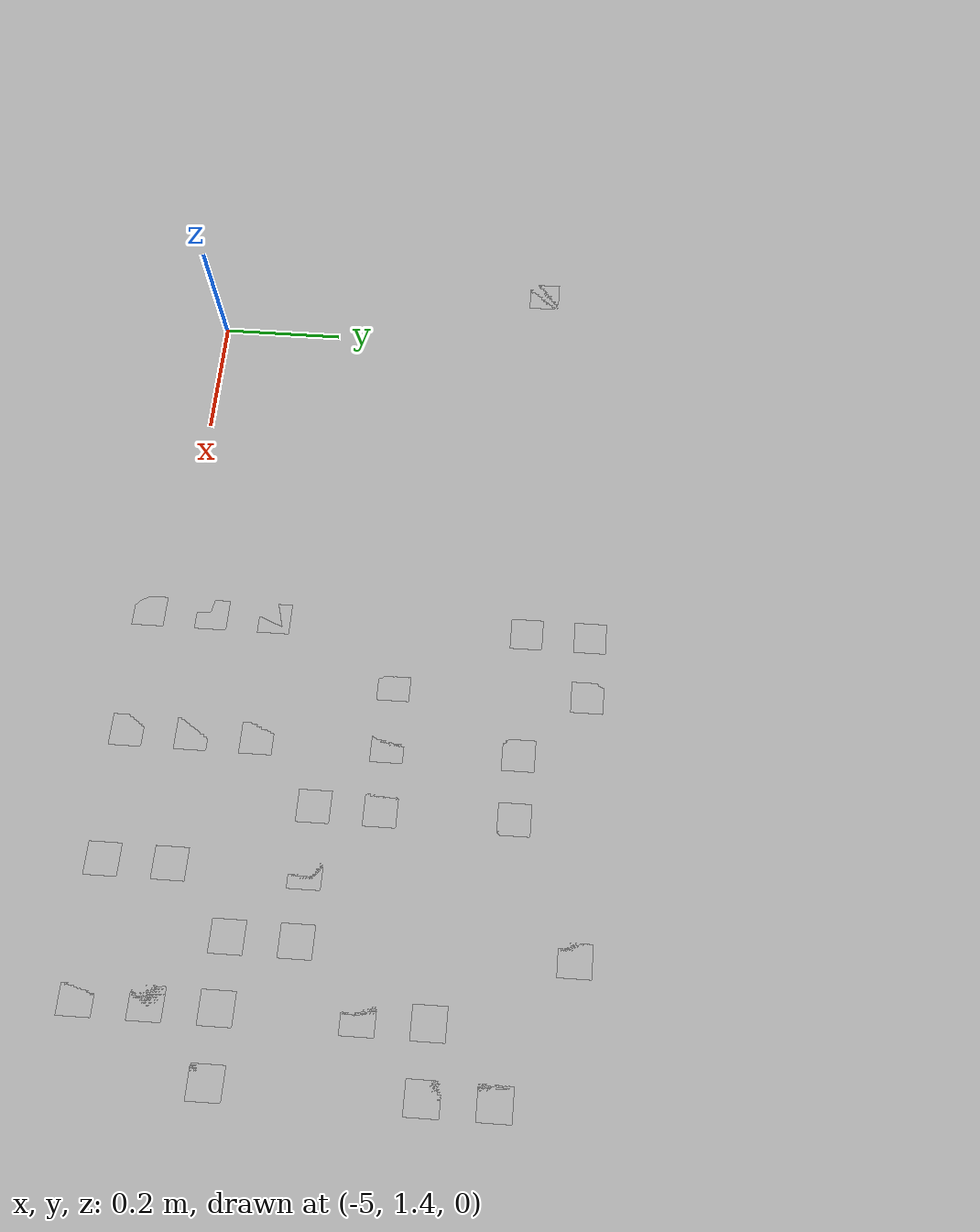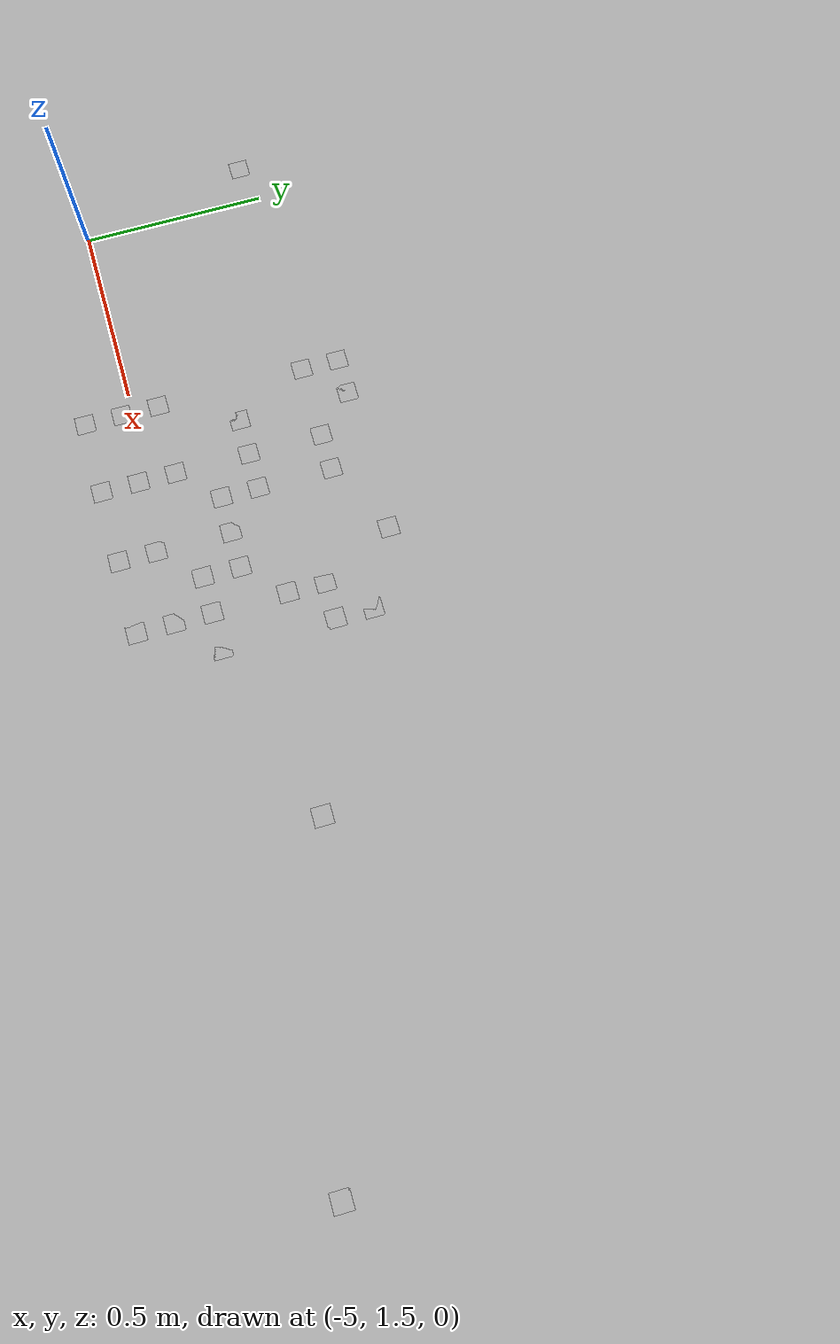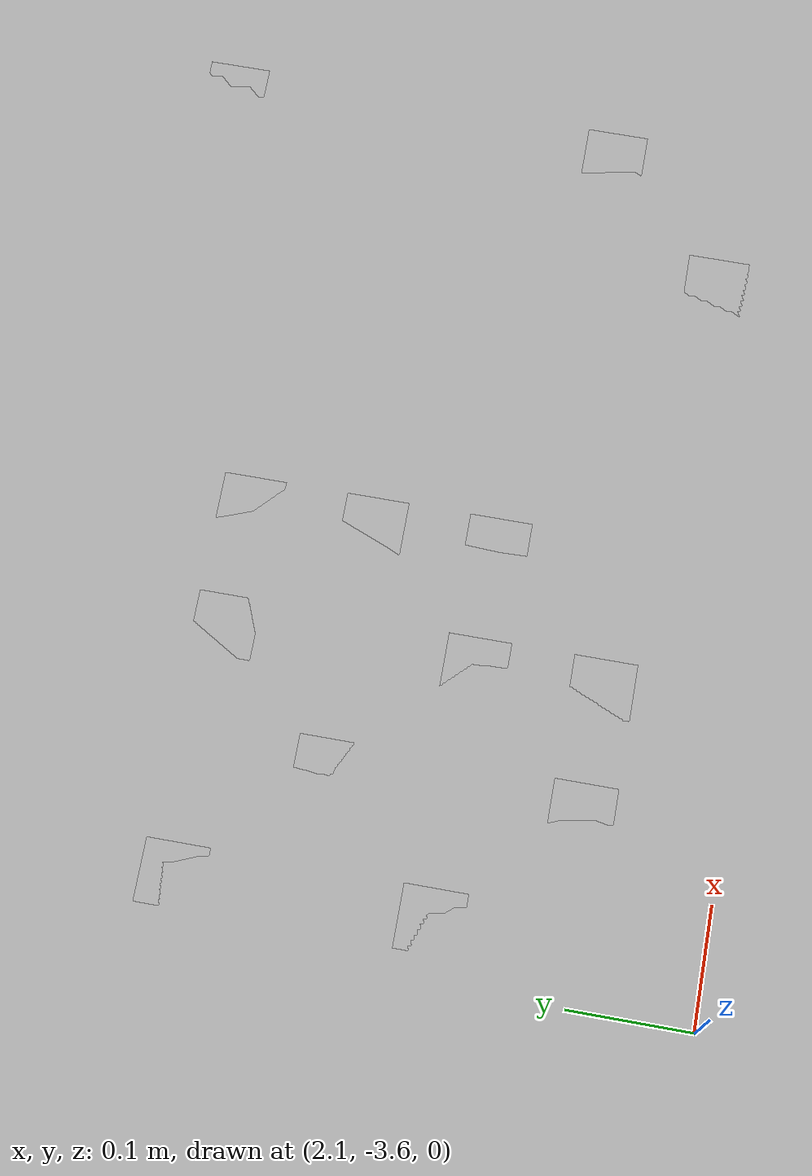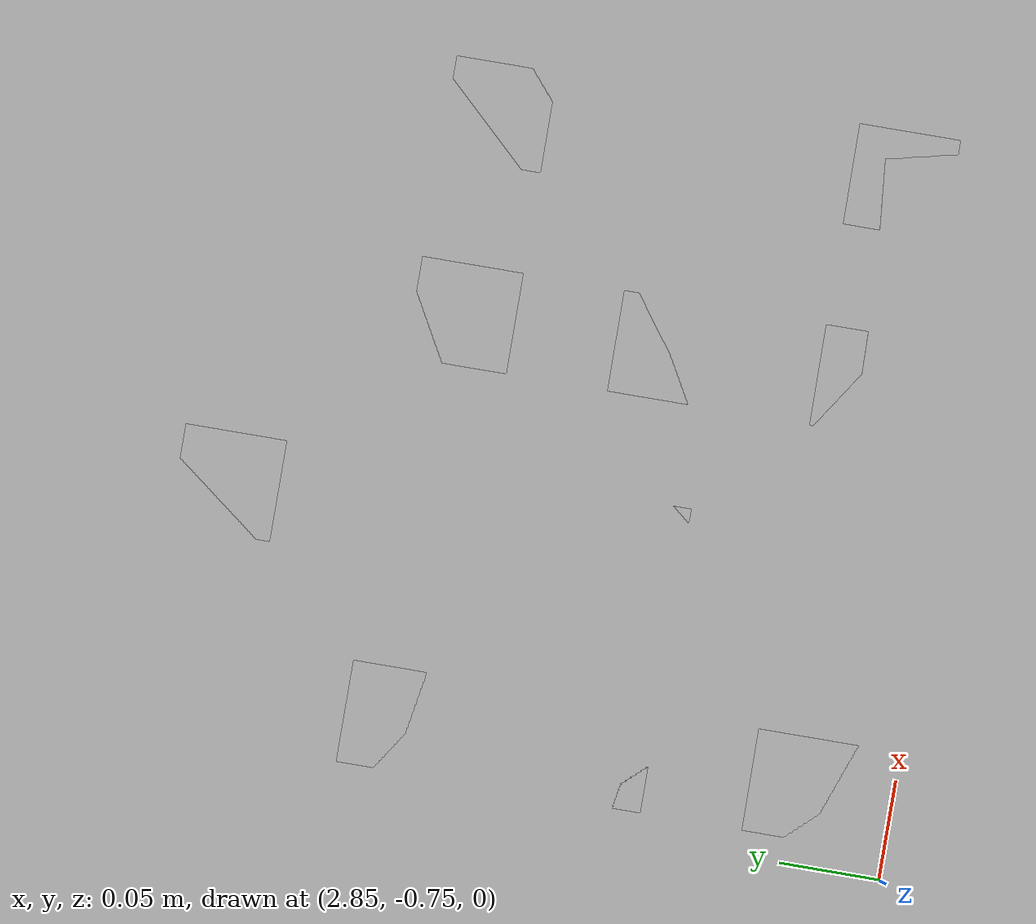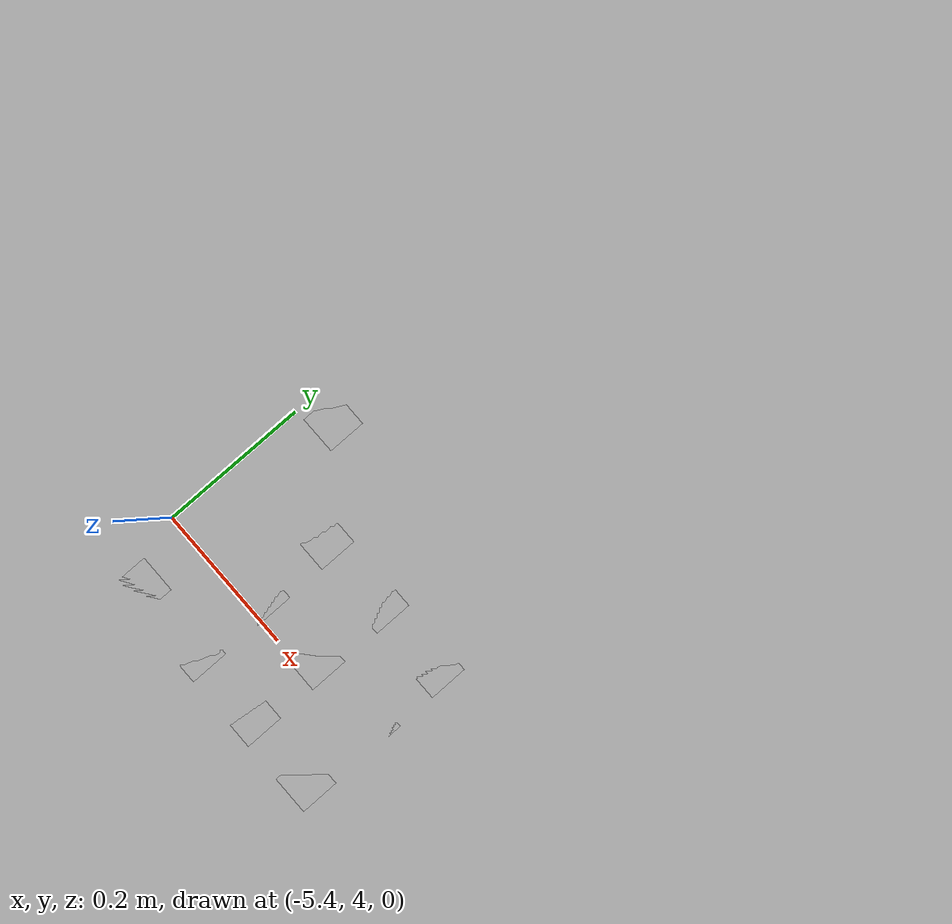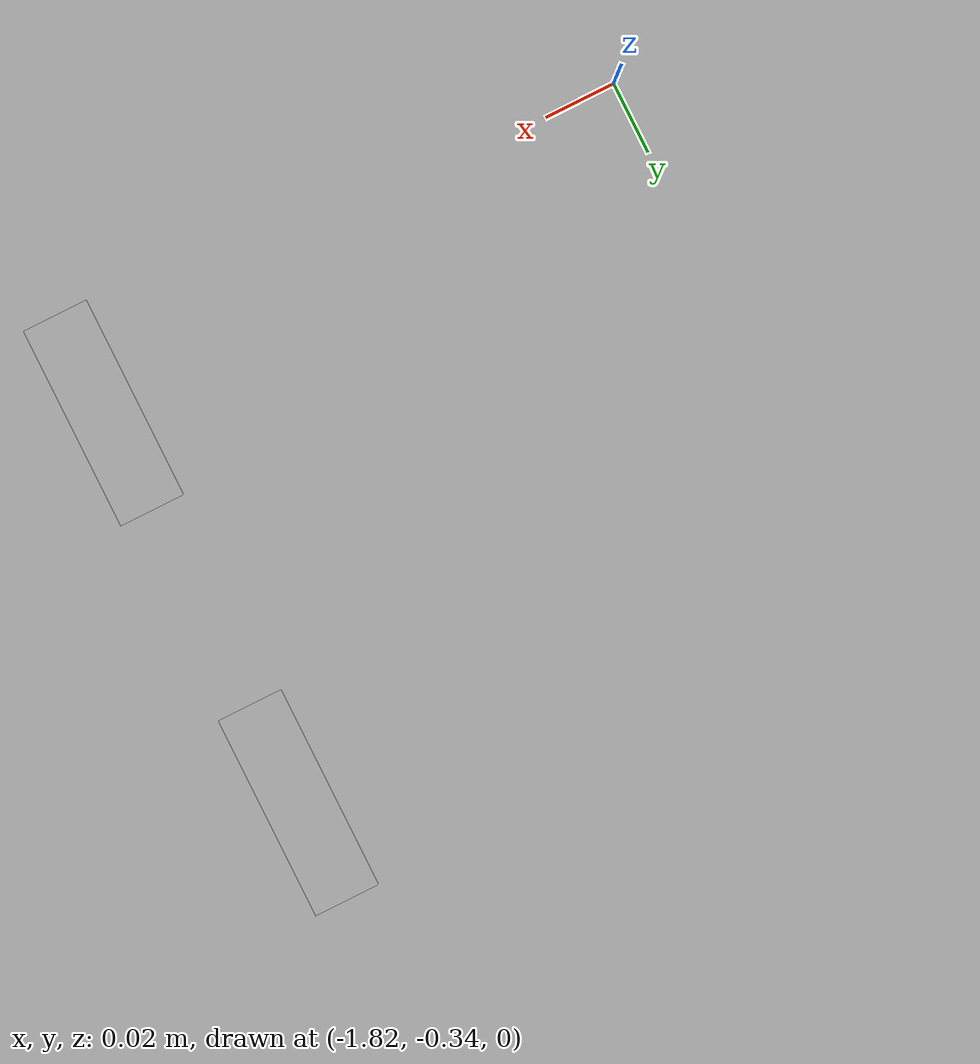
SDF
<sdf version="1.6">
 <world name="default">
  <model name="ground_plane">
   <static>1</static>
   <link name="link">
    <collision name="collision">
     <geometry><plane><normal>0 0 1</normal><size>100 100</size></plane></geometry>
     <surface><friction><ode><mu>100</mu><mu2>50</mu2></ode></friction></surface>
    </collision>
    <visual name="visual">
     <cast_shadows>0</cast_shadows>
     <geometry><plane><normal>0 0 1</normal><size>100 100</size></plane></geometry>
     <material>
      <script><uri>file://media/materials/scripts/gazebo.material</uri><name>Gazebo/Grey</name></script>
     </material>
    </visual>
   </link>
  </model>
  <light name="sun" type="directional">
   <pose>0 0 10 0 -0 0</pose>
   <diffuse>0.8 0.8 0.8 1</diffuse>
   <specular>0.1 0.1 0.1 1</specular>
   <attenuation>
    <range>1000</range>
    <constant>0.9</constant>
    <linear>0.01</linear>
    <quadratic>0.001</quadratic>
   </attenuation>
   <direction>-0.5 0.5 -1</direction>
  </light>
  <plugin name="SetupWorld" filename="libgazebo_plugins.so"/>
  <gravity>0 0 -9.8</gravity>
  <magnetic_field>6e-06 2.3e-05 -4.2e-05</magnetic_field>
  <atmosphere type="adiabatic"/>
  <physics name="default_physics" default="0" type="ode">
   <max_step_size>0.001</max_step_size>
   <real_time_factor>1</real_time_factor>
   <real_time_update_rate>1000</real_time_update_rate>
  </physics>
  <scene><ambient>0.4 0.4 0.4 1</ambient><background>0.7 0.7 0.7 1</background><shadows>1</shadows></scene>
  <spherical_coordinates>
   <surface_model>EARTH_WGS84</surface_model>
   <latitude_deg>0</latitude_deg>
   <longitude_deg>0</longitude_deg>
   <elevation>0</elevation>
   <heading_deg>0</heading_deg>
  </spherical_coordinates>
  <model name="Barrier_West">
   <static>1</static>
   <link name="link">
    <inertial>
     <mass>1</mass>
     <inertia><ixx>0.083</ixx><ixy>0</ixy><ixz>0</ixz><iyy>0</iyy><iyz>0</iyz><izz>0.083</izz></inertia>
    </inertial>
    <collision name="collision">
     <geometry><box><size>0.05 14 0.33</size></box></geometry>
     <surface><friction><ode><mu>1</mu><mu2>1</mu2><slip1>0</slip1><slip2>0</slip2></ode></friction></surface>
    </collision>
    <visual name="visual">
     <geometry><box><size>0.05 14 0.33</size></box></geometry>
     <material>
      <ambient>255 131 0 1</ambient>
      <diffuse>255 131 0 1</diffuse>
      <specular>0.1 0.1 0.1 1</specular>
      <emissive>0 0 0 0</emissive>
     </material>
    </visual>
   </link>
   <pose>-7 0 0 0 -0 0</pose>
  </model>
  <model name="Barrier_North">
   <static>1</static>
   <link name="link">
    <inertial>
     <mass>1</mass>
     <inertia><ixx>0.083</ixx><ixy>0</ixy><ixz>0</ixz><iyy>0</iyy><iyz>0</iyz><izz>0.083</izz></inertia>
    </inertial>
    <collision name="collision">
     <geometry><box><size>0.05 14 0.33</size></box></geometry>
     <surface><friction><ode><mu>1</mu><mu2>1</mu2><slip1>0</slip1><slip2>0</slip2></ode></friction></surface>
    </collision>
    <visual name="visual">
     <geometry><box><size>0.05 14 0.33</size></box></geometry>
     <material>
      <ambient>255 131 0 1</ambient>
      <diffuse>255 131 0 1</diffuse>
      <specular>0.1 0.1 0.1 1</specular>
      <emissive>0 0 0 0</emissive>
     </material>
    </visual>
   </link>
   <pose>0 -7 0 0 -0 1.5708</pose>
  </model>
  <model name="Barrier_East">
   <static>1</static>
   <link name="link">
    <inertial>
     <mass>1</mass>
     <inertia><ixx>0.083</ixx><ixy>0</ixy><ixz>0</ixz><iyy>0</iyy><iyz>0</iyz><izz>0.083</izz></inertia>
    </inertial>
    <collision name="collision">
     <geometry><box><size>0.05 14 0.33</size></box></geometry>
     <surface><friction><ode><mu>1</mu><mu2>1</mu2><slip1>0</slip1><slip2>0</slip2></ode></friction></surface>
    </collision>
    <visual name="visual">
     <geometry><box><size>0.05 14 0.33</size></box></geometry>
     <material>
      <ambient>255 131 0 1</ambient>
      <diffuse>255 131 0 1</diffuse>
      <specular>0.1 0.1 0.1 1</specular>
      <emissive>0 0 0 0</emissive>
     </material>
    </visual>
   </link>
   <pose>7 0 0 0 -0 0</pose>
  </model>
  <model name="Barrier_South">
   <static>1</static>
   <link name="link">
    <inertial>
     <mass>1</mass>
     <inertia><ixx>0.083</ixx><ixy>0</ixy><ixz>0</ixz><iyy>0</iyy><iyz>0</iyz><izz>0.083</izz></inertia>
    </inertial>
    <collision name="collision">
     <geometry><box><size>0.05 14 0.33</size></box></geometry>
     <surface><friction><ode><mu>1</mu><mu2>1</mu2><slip1>0</slip1><slip2>0</slip2></ode></friction></surface>
    </collision>
    <visual name="visual">
     <geometry><box><size>0.05 14 0.33</size></box></geometry>
     <material>
      <ambient>255 131 0 1</ambient>
      <diffuse>255 131 0 1</diffuse>
      <specular>0.1 0.1 0.1 1</specular>
      <emissive>0 0 0 0</emissive>
     </material>
    </visual>
   </link>
   <pose>0 7 0 0 -0 1.5708</pose>
  </model>
  <model name="concrete_ground_plane">
   <static>1</static>
   <link name="link">
    <collision name="collision">
     <geometry><plane><normal>0 0 1</normal><size>100 100</size></plane></geometry>
     <surface><friction><ode><mu>100</mu><mu2>50</mu2></ode></friction></surface>
    </collision>
    <visual name="visual">
     <cast_shadows>0</cast_shadows>
     <geometry><plane><normal>0 0 1</normal><size>100 100</size></plane></geometry>
     <material>
      <script>
       <uri>model://media/materials/scripts</uri>
       <uri>model://media/materials/textures</uri>
       <name>ConcreteGroundPlane/Image</name>
      </script>
     </material>
    </visual>
   </link>
  </model>
  <model name="collection_disk">
   <static>1</static>
   <link name="link">
    <visual name="visual">
     <geometry><box><size>1.016 1.016 0.001</size></box></geometry>
     <material>
      <script>
       <uri>model://collection_disk/materials/scripts</uri>
       <uri>model://collection_disk/materials/textures</uri>
       <name>collection_disk/Diffuse</name>
      </script>
     </material>
    </visual>
   </link>
   <plugin name="score_sim" filename="libgazebo_plugins_score.so">
    <scoreTopic>/collectionZone/score</scoreTopic>
    <collectionZoneSquareSize>1.016</collectionZoneSquareSize>
    <updateRate>0.2</updateRate>
    <robotNamespace>/</robotNamespace>
   </plugin>
  </model>
  <model name="at0">
   <static>0</static>
   <link name="link">
    <inertial>
     <mass>0.01</mass>
     <inertia><ixx>4e-05</ixx><ixy>0</ixy><ixz>0</ixz><iyy>4e-05</iyy><iyz>0</iyz><izz>4e-05</izz></inertia>
    </inertial>
    <visual name="visual">
     <geometry><box><size>0.05 0.05 0.05</size></box></geometry>
     <material>
      <script>
       <uri>model://at0/materials/scripts</uri>
       <uri>model://at0/materials/textures</uri>
       <name>at0/Diffuse</name>
      </script>
     </material>
    </visual>
    <collision name="collision">
     <geometry><box><size>0.05 0.05 0.05</size></box></geometry>
     <surface><friction><ode><mu>0.8</mu><mu2>0.7</mu2></ode></friction></surface>
    </collision>
   </link>
   <pose>-4.42244 1.37302 0.025 0 -2e-06 0</pose>
  </model>
  <model name="at1">
   <static>0</static>
   <link name="link">
    <inertial>
     <mass>0.01</mass>
     <inertia><ixx>4e-05</ixx><ixy>0</ixy><ixz>0</ixz><iyy>4e-05</iyy><iyz>0</iyz><izz>4e-05</izz></inertia>
    </inertial>
    <visual name="visual">
     <geometry><box><size>0.05 0.05 0.05</size></box></geometry>
     <material>
      <script>
       <uri>model://at0/materials/scripts</uri>
       <uri>model://at0/materials/textures</uri>
       <name>at0/Diffuse</name>
      </script>
     </material>
    </visual>
    <collision name="collision">
     <geometry><box><size>0.05 0.05 0.05</size></box></geometry>
     <surface><friction><ode><mu>0.8</mu><mu2>0.7</mu2></ode></friction></surface>
    </collision>
   </link>
   <pose>-4.32244 1.37302 0.02499 0 2e-06 0</pose>
  </model>
  <model name="at2">
   <static>0</static>
   <link name="link">
    <inertial>
     <mass>0.01</mass>
     <inertia><ixx>4e-05</ixx><ixy>0</ixy><ixz>0</ixz><iyy>4e-05</iyy><iyz>0</iyz><izz>4e-05</izz></inertia>
    </inertial>
    <visual name="visual">
     <geometry><box><size>0.05 0.05 0.05</size></box></geometry>
     <material>
      <script>
       <uri>model://at0/materials/scripts</uri>
       <uri>model://at0/materials/textures</uri>
       <name>at0/Diffuse</name>
      </script>
     </material>
    </visual>
    <collision name="collision">
     <geometry><box><size>0.05 0.05 0.05</size></box></geometry>
     <surface><friction><ode><mu>0.8</mu><mu2>0.7</mu2></ode></friction></surface>
    </collision>
   </link>
   <pose>-4.22244 1.37302 0.025 0 -2e-06 0</pose>
  </model>
  <model name="at3">
   <static>0</static>
   <link name="link">
    <inertial>
     <mass>0.01</mass>
     <inertia><ixx>4e-05</ixx><ixy>0</ixy><ixz>0</ixz><iyy>4e-05</iyy><iyz>0</iyz><izz>4e-05</izz></inertia>
    </inertial>
    <visual name="visual">
     <geometry><box><size>0.05 0.05 0.05</size></box></geometry>
     <material>
      <script>
       <uri>model://at0/materials/scripts</uri>
       <uri>model://at0/materials/textures</uri>
       <name>at0/Diffuse</name>
      </script>
     </material>
    </visual>
    <collision name="collision">
     <geometry><box><size>0.05 0.05 0.05</size></box></geometry>
     <surface><friction><ode><mu>0.8</mu><mu2>0.7</mu2></ode></friction></surface>
    </collision>
   </link>
   <pose>-4.12244 1.37302 0.02499 0 2e-06 0</pose>
  </model>
  <model name="at4">
   <static>0</static>
   <link name="link">
    <inertial>
     <mass>0.01</mass>
     <inertia><ixx>4e-05</ixx><ixy>0</ixy><ixz>0</ixz><iyy>4e-05</iyy><iyz>0</iyz><izz>4e-05</izz></inertia>
    </inertial>
    <visual name="visual">
     <geometry><box><size>0.05 0.05 0.05</size></box></geometry>
     <material>
      <script>
       <uri>model://at0/materials/scripts</uri>
       <uri>model://at0/materials/textures</uri>
       <name>at0/Diffuse</name>
      </script>
     </material>
    </visual>
    <collision name="collision">
     <geometry><box><size>0.05 0.05 0.05</size></box></geometry>
     <surface><friction><ode><mu>0.8</mu><mu2>0.7</mu2></ode></friction></surface>
    </collision>
   </link>
   <pose>-4.02244 1.37302 0.025 0 -2e-06 0</pose>
  </model>
  <model name="at5">
   <static>0</static>
   <link name="link">
    <inertial>
     <mass>0.01</mass>
     <inertia><ixx>4e-05</ixx><ixy>0</ixy><ixz>0</ixz><iyy>4e-05</iyy><iyz>0</iyz><izz>4e-05</izz></inertia>
    </inertial>
    <visual name="visual">
     <geometry><box><size>0.05 0.05 0.05</size></box></geometry>
     <material>
      <script>
       <uri>model://at0/materials/scripts</uri>
       <uri>model://at0/materials/textures</uri>
       <name>at0/Diffuse</name>
      </script>
     </material>
    </visual>
    <collision name="collision">
     <geometry><box><size>0.05 0.05 0.05</size></box></geometry>
     <surface><friction><ode><mu>0.8</mu><mu2>0.7</mu2></ode></friction></surface>
    </collision>
   </link>
   <pose>-3.92244 1.37302 0.02499 0 2e-06 0</pose>
  </model>
  <model name="at6">
   <static>0</static>
   <link name="link">
    <inertial>
     <mass>0.01</mass>
     <inertia><ixx>4e-05</ixx><ixy>0</ixy><ixz>0</ixz><iyy>4e-05</iyy><iyz>0</iyz><izz>4e-05</izz></inertia>
    </inertial>
    <visual name="visual">
     <geometry><box><size>0.05 0.05 0.05</size></box></geometry>
     <material>
      <script>
       <uri>model://at0/materials/scripts</uri>
       <uri>model://at0/materials/textures</uri>
       <name>at0/Diffuse</name>
      </script>
     </material>
    </visual>
    <collision name="collision">
     <geometry><box><size>0.05 0.05 0.05</size></box></geometry>
     <surface><friction><ode><mu>0.8</mu><mu2>0.7</mu2></ode></friction></surface>
    </collision>
   </link>
   <pose>-3.82244 1.37302 0.025 0 -2e-06 0</pose>
  </model>
  <model name="at7">
   <static>0</static>
   <link name="link">
    <inertial>
     <mass>0.01</mass>
     <inertia><ixx>4e-05</ixx><ixy>0</ixy><ixz>0</ixz><iyy>4e-05</iyy><iyz>0</iyz><izz>4e-05</izz></inertia>
    </inertial>
    <visual name="visual">
     <geometry><box><size>0.05 0.05 0.05</size></box></geometry>
     <material>
      <script>
       <uri>model://at0/materials/scripts</uri>
       <uri>model://at0/materials/textures</uri>
       <name>at0/Diffuse</name>
      </script>
     </material>
    </visual>
    <collision name="collision">
     <geometry><box><size>0.05 0.05 0.05</size></box></geometry>
     <surface><friction><ode><mu>0.8</mu><mu2>0.7</mu2></ode></friction></surface>
    </collision>
   </link>
   <pose>-3.72244 1.37302 0.02499 0 2e-06 0</pose>
  </model>
  <model name="at8">
   <static>0</static>
   <link name="link">
    <inertial>
     <mass>0.01</mass>
     <inertia><ixx>4e-05</ixx><ixy>0</ixy><ixz>0</ixz><iyy>4e-05</iyy><iyz>0</iyz><izz>4e-05</izz></inertia>
    </inertial>
    <visual name="visual">
     <geometry><box><size>0.05 0.05 0.05</size></box></geometry>
     <material>
      <script>
       <uri>model://at0/materials/scripts</uri>
       <uri>model://at0/materials/textures</uri>
       <name>at0/Diffuse</name>
      </script>
     </material>
    </visual>
    <collision name="collision">
     <geometry><box><size>0.05 0.05 0.05</size></box></geometry>
     <surface><friction><ode><mu>0.8</mu><mu2>0.7</mu2></ode></friction></surface>
    </collision>
   </link>
   <pose>-4.42244 1.47302 0.025 0 -2e-06 0</pose>
  </model>
  <model name="at9">
   <static>0</static>
   <link name="link">
    <inertial>
     <mass>0.01</mass>
     <inertia><ixx>4e-05</ixx><ixy>0</ixy><ixz>0</ixz><iyy>4e-05</iyy><iyz>0</iyz><izz>4e-05</izz></inertia>
    </inertial>
    <visual name="visual">
     <geometry><box><size>0.05 0.05 0.05</size></box></geometry>
     <material>
      <script>
       <uri>model://at0/materials/scripts</uri>
       <uri>model://at0/materials/textures</uri>
       <name>at0/Diffuse</name>
      </script>
     </material>
    </visual>
    <collision name="collision">
     <geometry><box><size>0.05 0.05 0.05</size></box></geometry>
     <surface><friction><ode><mu>0.8</mu><mu2>0.7</mu2></ode></friction></surface>
    </collision>
   </link>
   <pose>-4.32244 1.47302 0.02499 0 2e-06 0</pose>
  </model>
  <model name="at10">
   <static>0</static>
   <link name="link">
    <inertial>
     <mass>0.01</mass>
     <inertia><ixx>4e-05</ixx><ixy>0</ixy><ixz>0</ixz><iyy>4e-05</iyy><iyz>0</iyz><izz>4e-05</izz></inertia>
    </inertial>
    <visual name="visual">
     <geometry><box><size>0.05 0.05 0.05</size></box></geometry>
     <material>
      <script>
       <uri>model://at0/materials/scripts</uri>
       <uri>model://at0/materials/textures</uri>
       <name>at0/Diffuse</name>
      </script>
     </material>
    </visual>
    <collision name="collision">
     <geometry><box><size>0.05 0.05 0.05</size></box></geometry>
     <surface><friction><ode><mu>0.8</mu><mu2>0.7</mu2></ode></friction></surface>
    </collision>
   </link>
   <pose>-4.22244 1.47302 0.025 0 -2e-06 0</pose>
  </model>
  <model name="at11">
   <static>0</static>
   <link name="link">
    <inertial>
     <mass>0.01</mass>
     <inertia><ixx>4e-05</ixx><ixy>0</ixy><ixz>0</ixz><iyy>4e-05</iyy><iyz>0</iyz><izz>4e-05</izz></inertia>
    </inertial>
    <visual name="visual">
     <geometry><box><size>0.05 0.05 0.05</size></box></geometry>
     <material>
      <script>
       <uri>model://at0/materials/scripts</uri>
       <uri>model://at0/materials/textures</uri>
       <name>at0/Diffuse</name>
      </script>
     </material>
    </visual>
    <collision name="collision">
     <geometry><box><size>0.05 0.05 0.05</size></box></geometry>
     <surface><friction><ode><mu>0.8</mu><mu2>0.7</mu2></ode></friction></surface>
    </collision>
   </link>
   <pose>-4.12244 1.47302 0.02499 0 2e-06 0</pose>
  </model>
  <model name="at12">
   <static>0</static>
   <link name="link">
    <inertial>
     <mass>0.01</mass>
     <inertia><ixx>4e-05</ixx><ixy>0</ixy><ixz>0</ixz><iyy>4e-05</iyy><iyz>0</iyz><izz>4e-05</izz></inertia>
    </inertial>
    <visual name="visual">
     <geometry><box><size>0.05 0.05 0.05</size></box></geometry>
     <material>
      <script>
       <uri>model://at0/materials/scripts</uri>
       <uri>model://at0/materials/textures</uri>
       <name>at0/Diffuse</name>
      </script>
     </material>
    </visual>
    <collision name="collision">
     <geometry><box><size>0.05 0.05 0.05</size></box></geometry>
     <surface><friction><ode><mu>0.8</mu><mu2>0.7</mu2></ode></friction></surface>
    </collision>
   </link>
   <pose>-4.02244 1.47302 0.025 0 -2e-06 0</pose>
  </model>
  <model name="at13">
   <static>0</static>
   <link name="link">
    <inertial>
     <mass>0.01</mass>
     <inertia><ixx>4e-05</ixx><ixy>0</ixy><ixz>0</ixz><iyy>4e-05</iyy><iyz>0</iyz><izz>4e-05</izz></inertia>
    </inertial>
    <visual name="visual">
     <geometry><box><size>0.05 0.05 0.05</size></box></geometry>
     <material>
      <script>
       <uri>model://at0/materials/scripts</uri>
       <uri>model://at0/materials/textures</uri>
       <name>at0/Diffuse</name>
      </script>
     </material>
    </visual>
    <collision name="collision">
     <geometry><box><size>0.05 0.05 0.05</size></box></geometry>
     <surface><friction><ode><mu>0.8</mu><mu2>0.7</mu2></ode></friction></surface>
    </collision>
   </link>
   <pose>-3.92244 1.47302 0.02499 0 2e-06 0</pose>
  </model>
  <model name="at14">
   <static>0</static>
   <link name="link">
    <inertial>
     <mass>0.01</mass>
     <inertia><ixx>4e-05</ixx><ixy>0</ixy><ixz>0</ixz><iyy>4e-05</iyy><iyz>0</iyz><izz>4e-05</izz></inertia>
    </inertial>
    <visual name="visual">
     <geometry><box><size>0.05 0.05 0.05</size></box></geometry>
     <material>
      <script>
       <uri>model://at0/materials/scripts</uri>
       <uri>model://at0/materials/textures</uri>
       <name>at0/Diffuse</name>
      </script>
     </material>
    </visual>
    <collision name="collision">
     <geometry><box><size>0.05 0.05 0.05</size></box></geometry>
     <surface><friction><ode><mu>0.8</mu><mu2>0.7</mu2></ode></friction></surface>
    </collision>
   </link>
   <pose>-3.82244 1.47302 0.025 0 -2e-06 0</pose>
  </model>
  <model name="at15">
   <static>0</static>
   <link name="link">
    <inertial>
     <mass>0.01</mass>
     <inertia><ixx>4e-05</ixx><ixy>0</ixy><ixz>0</ixz><iyy>4e-05</iyy><iyz>0</iyz><izz>4e-05</izz></inertia>
    </inertial>
    <visual name="visual">
     <geometry><box><size>0.05 0.05 0.05</size></box></geometry>
     <material>
      <script>
       <uri>model://at0/materials/scripts</uri>
       <uri>model://at0/materials/textures</uri>
       <name>at0/Diffuse</name>
      </script>
     </material>
    </visual>
    <collision name="collision">
     <geometry><box><size>0.05 0.05 0.05</size></box></geometry>
     <surface><friction><ode><mu>0.8</mu><mu2>0.7</mu2></ode></friction></surface>
    </collision>
   </link>
   <pose>-3.72244 1.47302 0.02499 0 2e-06 0</pose>
  </model>
  <model name="at16">
   <static>0</static>
   <link name="link">
    <inertial>
     <mass>0.01</mass>
     <inertia><ixx>4e-05</ixx><ixy>0</ixy><ixz>0</ixz><iyy>4e-05</iyy><iyz>0</iyz><izz>4e-05</izz></inertia>
    </inertial>
    <visual name="visual">
     <geometry><box><size>0.05 0.05 0.05</size></box></geometry>
     <material>
      <script>
       <uri>model://at0/materials/scripts</uri>
       <uri>model://at0/materials/textures</uri>
       <name>at0/Diffuse</name>
      </script>
     </material>
    </visual>
    <collision name="collision">
     <geometry><box><size>0.05 0.05 0.05</size></box></geometry>
     <surface><friction><ode><mu>0.8</mu><mu2>0.7</mu2></ode></friction></surface>
    </collision>
   </link>
   <pose>-4.42244 1.57302 0.025 0 -2e-06 0</pose>
  </model>
  <model name="at17">
   <static>0</static>
   <link name="link">
    <inertial>
     <mass>0.01</mass>
     <inertia><ixx>4e-05</ixx><ixy>0</ixy><ixz>0</ixz><iyy>4e-05</iyy><iyz>0</iyz><izz>4e-05</izz></inertia>
    </inertial>
    <visual name="visual">
     <geometry><box><size>0.05 0.05 0.05</size></box></geometry>
     <material>
      <script>
       <uri>model://at0/materials/scripts</uri>
       <uri>model://at0/materials/textures</uri>
       <name>at0/Diffuse</name>
      </script>
     </material>
    </visual>
    <collision name="collision">
     <geometry><box><size>0.05 0.05 0.05</size></box></geometry>
     <surface><friction><ode><mu>0.8</mu><mu2>0.7</mu2></ode></friction></surface>
    </collision>
   </link>
   <pose>-4.32244 1.57302 0.02499 0 2e-06 0</pose>
  </model>
  <model name="at18">
   <static>0</static>
   <link name="link">
    <inertial>
     <mass>0.01</mass>
     <inertia><ixx>4e-05</ixx><ixy>0</ixy><ixz>0</ixz><iyy>4e-05</iyy><iyz>0</iyz><izz>4e-05</izz></inertia>
    </inertial>
    <visual name="visual">
     <geometry><box><size>0.05 0.05 0.05</size></box></geometry>
     <material>
      <script>
       <uri>model://at0/materials/scripts</uri>
       <uri>model://at0/materials/textures</uri>
       <name>at0/Diffuse</name>
      </script>
     </material>
    </visual>
    <collision name="collision">
     <geometry><box><size>0.05 0.05 0.05</size></box></geometry>
     <surface><friction><ode><mu>0.8</mu><mu2>0.7</mu2></ode></friction></surface>
    </collision>
   </link>
   <pose>-4.22244 1.57302 0.025 0 -2e-06 0</pose>
  </model>
  <model name="at19">
   <static>0</static>
   <link name="link">
    <inertial>
     <mass>0.01</mass>
     <inertia><ixx>4e-05</ixx><ixy>0</ixy><ixz>0</ixz><iyy>4e-05</iyy><iyz>0</iyz><izz>4e-05</izz></inertia>
    </inertial>
    <visual name="visual">
     <geometry><box><size>0.05 0.05 0.05</size></box></geometry>
     <material>
      <script>
       <uri>model://at0/materials/scripts</uri>
       <uri>model://at0/materials/textures</uri>
       <name>at0/Diffuse</name>
      </script>
     </material>
    </visual>
    <collision name="collision">
     <geometry><box><size>0.05 0.05 0.05</size></box></geometry>
     <surface><friction><ode><mu>0.8</mu><mu2>0.7</mu2></ode></friction></surface>
    </collision>
   </link>
   <pose>-4.12244 1.57302 0.02499 0 2e-06 0</pose>
  </model>
  <model name="at20">
   <static>0</static>
   <link name="link">
    <inertial>
     <mass>0.01</mass>
     <inertia><ixx>4e-05</ixx><ixy>0</ixy><ixz>0</ixz><iyy>4e-05</iyy><iyz>0</iyz><izz>4e-05</izz></inertia>
    </inertial>
    <visual name="visual">
     <geometry><box><size>0.05 0.05 0.05</size></box></geometry>
     <material>
      <script>
       <uri>model://at0/materials/scripts</uri>
       <uri>model://at0/materials/textures</uri>
       <name>at0/Diffuse</name>
      </script>
     </material>
    </visual>
    <collision name="collision">
     <geometry><box><size>0.05 0.05 0.05</size></box></geometry>
     <surface><friction><ode><mu>0.8</mu><mu2>0.7</mu2></ode></friction></surface>
    </collision>
   </link>
   <pose>-4.02244 1.57302 0.02499 0 2e-06 0</pose>
  </model>
  <model name="at21">
   <static>0</static>
   <link name="link">
    <inertial>
     <mass>0.01</mass>
     <inertia><ixx>4e-05</ixx><ixy>0</ixy><ixz>0</ixz><iyy>4e-05</iyy><iyz>0</iyz><izz>4e-05</izz></inertia>
    </inertial>
    <visual name="visual">
     <geometry><box><size>0.05 0.05 0.05</size></box></geometry>
     <material>
      <script>
       <uri>model://at0/materials/scripts</uri>
       <uri>model://at0/materials/textures</uri>
       <name>at0/Diffuse</name>
      </script>
     </material>
    </visual>
    <collision name="collision">
     <geometry><box><size>0.05 0.05 0.05</size></box></geometry>
     <surface><friction><ode><mu>0.8</mu><mu2>0.7</mu2></ode></friction></surface>
    </collision>
   </link>
   <pose>-3.92244 1.57302 0.025 0 -2e-06 0</pose>
  </model>
  <model name="at22">
   <static>0</static>
   <link name="link">
    <inertial>
     <mass>0.01</mass>
     <inertia><ixx>4e-05</ixx><ixy>0</ixy><ixz>0</ixz><iyy>4e-05</iyy><iyz>0</iyz><izz>4e-05</izz></inertia>
    </inertial>
    <visual name="visual">
     <geometry><box><size>0.05 0.05 0.05</size></box></geometry>
     <material>
      <script>
       <uri>model://at0/materials/scripts</uri>
       <uri>model://at0/materials/textures</uri>
       <name>at0/Diffuse</name>
      </script>
     </material>
    </visual>
    <collision name="collision">
     <geometry><box><size>0.05 0.05 0.05</size></box></geometry>
     <surface><friction><ode><mu>0.8</mu><mu2>0.7</mu2></ode></friction></surface>
    </collision>
   </link>
   <pose>-3.82244 1.57302 0.025 0 -2e-06 0</pose>
  </model>
  <model name="at23">
   <static>0</static>
   <link name="link">
    <inertial>
     <mass>0.01</mass>
     <inertia><ixx>4e-05</ixx><ixy>0</ixy><ixz>0</ixz><iyy>4e-05</iyy><iyz>0</iyz><izz>4e-05</izz></inertia>
    </inertial>
    <visual name="visual">
     <geometry><box><size>0.05 0.05 0.05</size></box></geometry>
     <material>
      <script>
       <uri>model://at0/materials/scripts</uri>
       <uri>model://at0/materials/textures</uri>
       <name>at0/Diffuse</name>
      </script>
     </material>
    </visual>
    <collision name="collision">
     <geometry><box><size>0.05 0.05 0.05</size></box></geometry>
     <surface><friction><ode><mu>0.8</mu><mu2>0.7</mu2></ode></friction></surface>
    </collision>
   </link>
   <pose>-3.72244 1.57302 0.025 0 -2e-06 0</pose>
  </model>
  <model name="at24">
   <static>0</static>
   <link name="link">
    <inertial>
     <mass>0.01</mass>
     <inertia><ixx>4e-05</ixx><ixy>0</ixy><ixz>0</ixz><iyy>4e-05</iyy><iyz>0</iyz><izz>4e-05</izz></inertia>
    </inertial>
    <visual name="visual">
     <geometry><box><size>0.05 0.05 0.05</size></box></geometry>
     <material>
      <script>
       <uri>model://at0/materials/scripts</uri>
       <uri>model://at0/materials/textures</uri>
       <name>at0/Diffuse</name>
      </script>
     </material>
    </visual>
    <collision name="collision">
     <geometry><box><size>0.05 0.05 0.05</size></box></geometry>
     <surface><friction><ode><mu>0.8</mu><mu2>0.7</mu2></ode></friction></surface>
    </collision>
   </link>
   <pose>-4.42244 1.67302 0.02499 0 2e-06 0</pose>
  </model>
  <model name="at25">
   <static>0</static>
   <link name="link">
    <inertial>
     <mass>0.01</mass>
     <inertia><ixx>4e-05</ixx><ixy>0</ixy><ixz>0</ixz><iyy>4e-05</iyy><iyz>0</iyz><izz>4e-05</izz></inertia>
    </inertial>
    <visual name="visual">
     <geometry><box><size>0.05 0.05 0.05</size></box></geometry>
     <material>
      <script>
       <uri>model://at0/materials/scripts</uri>
       <uri>model://at0/materials/textures</uri>
       <name>at0/Diffuse</name>
      </script>
     </material>
    </visual>
    <collision name="collision">
     <geometry><box><size>0.05 0.05 0.05</size></box></geometry>
     <surface><friction><ode><mu>0.8</mu><mu2>0.7</mu2></ode></friction></surface>
    </collision>
   </link>
   <pose>-4.32244 1.67302 0.02499 0 2e-06 0</pose>
  </model>
  <model name="at26">
   <static>0</static>
   <link name="link">
    <inertial>
     <mass>0.01</mass>
     <inertia><ixx>4e-05</ixx><ixy>0</ixy><ixz>0</ixz><iyy>4e-05</iyy><iyz>0</iyz><izz>4e-05</izz></inertia>
    </inertial>
    <visual name="visual">
     <geometry><box><size>0.05 0.05 0.05</size></box></geometry>
     <material>
      <script>
       <uri>model://at0/materials/scripts</uri>
       <uri>model://at0/materials/textures</uri>
       <name>at0/Diffuse</name>
      </script>
     </material>
    </visual>
    <collision name="collision">
     <geometry><box><size>0.05 0.05 0.05</size></box></geometry>
     <surface><friction><ode><mu>0.8</mu><mu2>0.7</mu2></ode></friction></surface>
    </collision>
   </link>
   <pose>-4.22244 1.67302 0.02499 0 2e-06 0</pose>
  </model>
  <model name="at27">
   <static>0</static>
   <link name="link">
    <inertial>
     <mass>0.01</mass>
     <inertia><ixx>4e-05</ixx><ixy>0</ixy><ixz>0</ixz><iyy>4e-05</iyy><iyz>0</iyz><izz>4e-05</izz></inertia>
    </inertial>
    <visual name="visual">
     <geometry><box><size>0.05 0.05 0.05</size></box></geometry>
     <material>
      <script>
       <uri>model://at0/materials/scripts</uri>
       <uri>model://at0/materials/textures</uri>
       <name>at0/Diffuse</name>
      </script>
     </material>
    </visual>
    <collision name="collision">
     <geometry><box><size>0.05 0.05 0.05</size></box></geometry>
     <surface><friction><ode><mu>0.8</mu><mu2>0.7</mu2></ode></friction></surface>
    </collision>
   </link>
   <pose>-4.12244 1.67302 0.025 0 -2e-06 0</pose>
  </model>
  <model name="at28">
   <static>0</static>
   <link name="link">
    <inertial>
     <mass>0.01</mass>
     <inertia><ixx>4e-05</ixx><ixy>0</ixy><ixz>0</ixz><iyy>4e-05</iyy><iyz>0</iyz><izz>4e-05</izz></inertia>
    </inertial>
    <visual name="visual">
     <geometry><box><size>0.05 0.05 0.05</size></box></geometry>
     <material>
      <script>
       <uri>model://at0/materials/scripts</uri>
       <uri>model://at0/materials/textures</uri>
       <name>at0/Diffuse</name>
      </script>
     </material>
    </visual>
    <collision name="collision">
     <geometry><box><size>0.05 0.05 0.05</size></box></geometry>
     <surface><friction><ode><mu>0.8</mu><mu2>0.7</mu2></ode></friction></surface>
    </collision>
   </link>
   <pose>-4.02244 1.67302 0.025 0 -2e-06 0</pose>
  </model>
  <model name="at29">
   <static>0</static>
   <link name="link">
    <inertial>
     <mass>0.01</mass>
     <inertia><ixx>4e-05</ixx><ixy>0</ixy><ixz>0</ixz><iyy>4e-05</iyy><iyz>0</iyz><izz>4e-05</izz></inertia>
    </inertial>
    <visual name="visual">
     <geometry><box><size>0.05 0.05 0.05</size></box></geometry>
     <material>
      <script>
       <uri>model://at0/materials/scripts</uri>
       <uri>model://at0/materials/textures</uri>
       <name>at0/Diffuse</name>
      </script>
     </material>
    </visual>
    <collision name="collision">
     <geometry><box><size>0.05 0.05 0.05</size></box></geometry>
     <surface><friction><ode><mu>0.8</mu><mu2>0.7</mu2></ode></friction></surface>
    </collision>
   </link>
   <pose>-3.92244 1.67302 0.025 0 -2e-06 0</pose>
  </model>
  <model name="at30">
   <static>0</static>
   <link name="link">
    <inertial>
     <mass>0.01</mass>
     <inertia><ixx>4e-05</ixx><ixy>0</ixy><ixz>0</ixz><iyy>4e-05</iyy><iyz>0</iyz><izz>4e-05</izz></inertia>
    </inertial>
    <visual name="visual">
     <geometry><box><size>0.05 0.05 0.05</size></box></geometry>
     <material>
      <script>
       <uri>model://at0/materials/scripts</uri>
       <uri>model://at0/materials/textures</uri>
       <name>at0/Diffuse</name>
      </script>
     </material>
    </visual>
    <collision name="collision">
     <geometry><box><size>0.05 0.05 0.05</size></box></geometry>
     <surface><friction><ode><mu>0.8</mu><mu2>0.7</mu2></ode></friction></surface>
    </collision>
   </link>
   <pose>-3.82244 1.67302 0.02499 0 2e-06 0</pose>
  </model>
  <model name="at31">
   <static>0</static>
   <link name="link">
    <inertial>
     <mass>0.01</mass>
     <inertia><ixx>4e-05</ixx><ixy>0</ixy><ixz>0</ixz><iyy>4e-05</iyy><iyz>0</iyz><izz>4e-05</izz></inertia>
    </inertial>
    <visual name="visual">
     <geometry><box><size>0.05 0.05 0.05</size></box></geometry>
     <material>
      <script>
       <uri>model://at0/materials/scripts</uri>
       <uri>model://at0/materials/textures</uri>
       <name>at0/Diffuse</name>
      </script>
     </material>
    </visual>
    <collision name="collision">
     <geometry><box><size>0.05 0.05 0.05</size></box></geometry>
     <surface><friction><ode><mu>0.8</mu><mu2>0.7</mu2></ode></friction></surface>
    </collision>
   </link>
   <pose>-3.72244 1.67302 0.02499 0 2e-06 0</pose>
  </model>
  <model name="at32">
   <static>0</static>
   <link name="link">
    <inertial>
     <mass>0.01</mass>
     <inertia><ixx>4e-05</ixx><ixy>0</ixy><ixz>0</ixz><iyy>4e-05</iyy><iyz>0</iyz><izz>4e-05</izz></inertia>
    </inertial>
    <visual name="visual">
     <geometry><box><size>0.05 0.05 0.05</size></box></geometry>
     <material>
      <script>
       <uri>model://at0/materials/scripts</uri>
       <uri>model://at0/materials/textures</uri>
       <name>at0/Diffuse</name>
      </script>
     </material>
    </visual>
    <collision name="collision">
     <geometry><box><size>0.05 0.05 0.05</size></box></geometry>
     <surface><friction><ode><mu>0.8</mu><mu2>0.7</mu2></ode></friction></surface>
    </collision>
   </link>
   <pose>-4.42244 1.77302 0.02499 0 2e-06 0</pose>
  </model>
  <model name="at33">
   <static>0</static>
   <link name="link">
    <inertial>
     <mass>0.01</mass>
     <inertia><ixx>4e-05</ixx><ixy>0</ixy><ixz>0</ixz><iyy>4e-05</iyy><iyz>0</iyz><izz>4e-05</izz></inertia>
    </inertial>
    <visual name="visual">
     <geometry><box><size>0.05 0.05 0.05</size></box></geometry>
     <material>
      <script>
       <uri>model://at0/materials/scripts</uri>
       <uri>model://at0/materials/textures</uri>
       <name>at0/Diffuse</name>
      </script>
     </material>
    </visual>
    <collision name="collision">
     <geometry><box><size>0.05 0.05 0.05</size></box></geometry>
     <surface><friction><ode><mu>0.8</mu><mu2>0.7</mu2></ode></friction></surface>
    </collision>
   </link>
   <pose>-4.32244 1.77302 0.025 0 -2e-06 0</pose>
  </model>
  <model name="at34">
   <static>0</static>
   <link name="link">
    <inertial>
     <mass>0.01</mass>
     <inertia><ixx>4e-05</ixx><ixy>0</ixy><ixz>0</ixz><iyy>4e-05</iyy><iyz>0</iyz><izz>4e-05</izz></inertia>
    </inertial>
    <visual name="visual">
     <geometry><box><size>0.05 0.05 0.05</size></box></geometry>
     <material>
      <script>
       <uri>model://at0/materials/scripts</uri>
       <uri>model://at0/materials/textures</uri>
       <name>at0/Diffuse</name>
      </script>
     </material>
    </visual>
    <collision name="collision">
     <geometry><box><size>0.05 0.05 0.05</size></box></geometry>
     <surface><friction><ode><mu>0.8</mu><mu2>0.7</mu2></ode></friction></surface>
    </collision>
   </link>
   <pose>-4.22244 1.77302 0.025 0 -2e-06 0</pose>
  </model>
  <model name="at35">
   <static>0</static>
   <link name="link">
    <inertial>
     <mass>0.01</mass>
     <inertia><ixx>4e-05</ixx><ixy>0</ixy><ixz>0</ixz><iyy>4e-05</iyy><iyz>0</iyz><izz>4e-05</izz></inertia>
    </inertial>
    <visual name="visual">
     <geometry><box><size>0.05 0.05 0.05</size></box></geometry>
     <material>
      <script>
       <uri>model://at0/materials/scripts</uri>
       <uri>model://at0/materials/textures</uri>
       <name>at0/Diffuse</name>
      </script>
     </material>
    </visual>
    <collision name="collision">
     <geometry><box><size>0.05 0.05 0.05</size></box></geometry>
     <surface><friction><ode><mu>0.8</mu><mu2>0.7</mu2></ode></friction></surface>
    </collision>
   </link>
   <pose>-4.12244 1.77302 0.025 0 -2e-06 0</pose>
  </model>
  <model name="at36">
   <static>0</static>
   <link name="link">
    <inertial>
     <mass>0.01</mass>
     <inertia><ixx>4e-05</ixx><ixy>0</ixy><ixz>0</ixz><iyy>4e-05</iyy><iyz>0</iyz><izz>4e-05</izz></inertia>
    </inertial>
    <visual name="visual">
     <geometry><box><size>0.05 0.05 0.05</size></box></geometry>
     <material>
      <script>
       <uri>model://at0/materials/scripts</uri>
       <uri>model://at0/materials/textures</uri>
       <name>at0/Diffuse</name>
      </script>
     </material>
    </visual>
    <collision name="collision">
     <geometry><box><size>0.05 0.05 0.05</size></box></geometry>
     <surface><friction><ode><mu>0.8</mu><mu2>0.7</mu2></ode></friction></surface>
    </collision>
   </link>
   <pose>-4.02244 1.77302 0.02499 0 2e-06 0</pose>
  </model>
  <model name="at37">
   <static>0</static>
   <link name="link">
    <inertial>
     <mass>0.01</mass>
     <inertia><ixx>4e-05</ixx><ixy>0</ixy><ixz>0</ixz><iyy>4e-05</iyy><iyz>0</iyz><izz>4e-05</izz></inertia>
    </inertial>
    <visual name="visual">
     <geometry><box><size>0.05 0.05 0.05</size></box></geometry>
     <material>
      <script>
       <uri>model://at0/materials/scripts</uri>
       <uri>model://at0/materials/textures</uri>
       <name>at0/Diffuse</name>
      </script>
     </material>
    </visual>
    <collision name="collision">
     <geometry><box><size>0.05 0.05 0.05</size></box></geometry>
     <surface><friction><ode><mu>0.8</mu><mu2>0.7</mu2></ode></friction></surface>
    </collision>
   </link>
   <pose>-3.92244 1.77302 0.02499 0 2e-06 0</pose>
  </model>
  <model name="at38">
   <static>0</static>
   <link name="link">
    <inertial>
     <mass>0.01</mass>
     <inertia><ixx>4e-05</ixx><ixy>0</ixy><ixz>0</ixz><iyy>4e-05</iyy><iyz>0</iyz><izz>4e-05</izz></inertia>
    </inertial>
    <visual name="visual">
     <geometry><box><size>0.05 0.05 0.05</size></box></geometry>
     <material>
      <script>
       <uri>model://at0/materials/scripts</uri>
       <uri>model://at0/materials/textures</uri>
       <name>at0/Diffuse</name>
      </script>
     </material>
    </visual>
    <collision name="collision">
     <geometry><box><size>0.05 0.05 0.05</size></box></geometry>
     <surface><friction><ode><mu>0.8</mu><mu2>0.7</mu2></ode></friction></surface>
    </collision>
   </link>
   <pose>-3.82244 1.77302 0.025 0 -2e-06 0</pose>
  </model>
  <model name="at39">
   <static>0</static>
   <link name="link">
    <inertial>
     <mass>0.01</mass>
     <inertia><ixx>4e-05</ixx><ixy>0</ixy><ixz>0</ixz><iyy>4e-05</iyy><iyz>0</iyz><izz>4e-05</izz></inertia>
    </inertial>
    <visual name="visual">
     <geometry><box><size>0.05 0.05 0.05</size></box></geometry>
     <material>
      <script>
       <uri>model://at0/materials/scripts</uri>
       <uri>model://at0/materials/textures</uri>
       <name>at0/Diffuse</name>
      </script>
     </material>
    </visual>
    <collision name="collision">
     <geometry><box><size>0.05 0.05 0.05</size></box></geometry>
     <surface><friction><ode><mu>0.8</mu><mu2>0.7</mu2></ode></friction></surface>
    </collision>
   </link>
   <pose>-3.72244 1.77302 0.02499 0 2e-06 0</pose>
  </model>
  <model name="at40">
   <static>0</static>
   <link name="link">
    <inertial>
     <mass>0.01</mass>
     <inertia><ixx>4e-05</ixx><ixy>0</ixy><ixz>0</ixz><iyy>4e-05</iyy><iyz>0</iyz><izz>4e-05</izz></inertia>
    </inertial>
    <visual name="visual">
     <geometry><box><size>0.05 0.05 0.05</size></box></geometry>
     <material>
      <script>
       <uri>model://at0/materials/scripts</uri>
       <uri>model://at0/materials/textures</uri>
       <name>at0/Diffuse</name>
      </script>
     </material>
    </visual>
    <collision name="collision">
     <geometry><box><size>0.05 0.05 0.05</size></box></geometry>
     <surface><friction><ode><mu>0.8</mu><mu2>0.7</mu2></ode></friction></surface>
    </collision>
   </link>
   <pose>-4.42244 1.87302 0.02499 0 2e-06 0</pose>
  </model>
  <model name="at41">
   <static>0</static>
   <link name="link">
    <inertial>
     <mass>0.01</mass>
     <inertia><ixx>4e-05</ixx><ixy>0</ixy><ixz>0</ixz><iyy>4e-05</iyy><iyz>0</iyz><izz>4e-05</izz></inertia>
    </inertial>
    <visual name="visual">
     <geometry><box><size>0.05 0.05 0.05</size></box></geometry>
     <material>
      <script>
       <uri>model://at0/materials/scripts</uri>
       <uri>model://at0/materials/textures</uri>
       <name>at0/Diffuse</name>
      </script>
     </material>
    </visual>
    <collision name="collision">
     <geometry><box><size>0.05 0.05 0.05</size></box></geometry>
     <surface><friction><ode><mu>0.8</mu><mu2>0.7</mu2></ode></friction></surface>
    </collision>
   </link>
   <pose>-4.32244 1.87302 0.02499 0 2e-06 0</pose>
  </model>
  <model name="at42">
   <static>0</static>
   <link name="link">
    <inertial>
     <mass>0.01</mass>
     <inertia><ixx>4e-05</ixx><ixy>0</ixy><ixz>0</ixz><iyy>4e-05</iyy><iyz>0</iyz><izz>4e-05</izz></inertia>
    </inertial>
    <visual name="visual">
     <geometry><box><size>0.05 0.05 0.05</size></box></geometry>
     <material>
      <script>
       <uri>model://at0/materials/scripts</uri>
       <uri>model://at0/materials/textures</uri>
       <name>at0/Diffuse</name>
      </script>
     </material>
    </visual>
    <collision name="collision">
     <geometry><box><size>0.05 0.05 0.05</size></box></geometry>
     <surface><friction><ode><mu>0.8</mu><mu2>0.7</mu2></ode></friction></surface>
    </collision>
   </link>
   <pose>-4.22244 1.87302 0.02499 0 2e-06 0</pose>
  </model>
  <model name="at43">
   <static>0</static>
   <link name="link">
    <inertial>
     <mass>0.01</mass>
     <inertia><ixx>4e-05</ixx><ixy>0</ixy><ixz>0</ixz><iyy>4e-05</iyy><iyz>0</iyz><izz>4e-05</izz></inertia>
    </inertial>
    <visual name="visual">
     <geometry><box><size>0.05 0.05 0.05</size></box></geometry>
     <material>
      <script>
       <uri>model://at0/materials/scripts</uri>
       <uri>model://at0/materials/textures</uri>
       <name>at0/Diffuse</name>
      </script>
     </material>
    </visual>
    <collision name="collision">
     <geometry><box><size>0.05 0.05 0.05</size></box></geometry>
     <surface><friction><ode><mu>0.8</mu><mu2>0.7</mu2></ode></friction></surface>
    </collision>
   </link>
   <pose>-4.12244 1.87302 0.02499 0 2e-06 0</pose>
  </model>
  <model name="at44">
   <static>0</static>
   <link name="link">
    <inertial>
     <mass>0.01</mass>
     <inertia><ixx>4e-05</ixx><ixy>0</ixy><ixz>0</ixz><iyy>4e-05</iyy><iyz>0</iyz><izz>4e-05</izz></inertia>
    </inertial>
    <visual name="visual">
     <geometry><box><size>0.05 0.05 0.05</size></box></geometry>
     <material>
      <script>
       <uri>model://at0/materials/scripts</uri>
       <uri>model://at0/materials/textures</uri>
       <name>at0/Diffuse</name>
      </script>
     </material>
    </visual>
    <collision name="collision">
     <geometry><box><size>0.05 0.05 0.05</size></box></geometry>
     <surface><friction><ode><mu>0.8</mu><mu2>0.7</mu2></ode></friction></surface>
    </collision>
   </link>
   <pose>-4.02244 1.87302 0.02499 0 2e-06 0</pose>
  </model>
  <model name="at45">
   <static>0</static>
   <link name="link">
    <inertial>
     <mass>0.01</mass>
     <inertia><ixx>4e-05</ixx><ixy>0</ixy><ixz>0</ixz><iyy>4e-05</iyy><iyz>0</iyz><izz>4e-05</izz></inertia>
    </inertial>
    <visual name="visual">
     <geometry><box><size>0.05 0.05 0.05</size></box></geometry>
     <material>
      <script>
       <uri>model://at0/materials/scripts</uri>
       <uri>model://at0/materials/textures</uri>
       <name>at0/Diffuse</name>
      </script>
     </material>
    </visual>
    <collision name="collision">
     <geometry><box><size>0.05 0.05 0.05</size></box></geometry>
     <surface><friction><ode><mu>0.8</mu><mu2>0.7</mu2></ode></friction></surface>
    </collision>
   </link>
   <pose>-3.92244 1.87302 0.02499 0 2e-06 0</pose>
  </model>
  <model name="at46">
   <static>0</static>
   <link name="link">
    <inertial>
     <mass>0.01</mass>
     <inertia><ixx>4e-05</ixx><ixy>0</ixy><ixz>0</ixz><iyy>4e-05</iyy><iyz>0</iyz><izz>4e-05</izz></inertia>
    </inertial>
    <visual name="visual">
     <geometry><box><size>0.05 0.05 0.05</size></box></geometry>
     <material>
      <script>
       <uri>model://at0/materials/scripts</uri>
       <uri>model://at0/materials/textures</uri>
       <name>at0/Diffuse</name>
      </script>
     </material>
    </visual>
    <collision name="collision">
     <geometry><box><size>0.05 0.05 0.05</size></box></geometry>
     <surface><friction><ode><mu>0.8</mu><mu2>0.7</mu2></ode></friction></surface>
    </collision>
   </link>
   <pose>-3.82244 1.87302 0.025 0 -2e-06 0</pose>
  </model>
  <model name="at47">
   <static>0</static>
   <link name="link">
    <inertial>
     <mass>0.01</mass>
     <inertia><ixx>4e-05</ixx><ixy>0</ixy><ixz>0</ixz><iyy>4e-05</iyy><iyz>0</iyz><izz>4e-05</izz></inertia>
    </inertial>
    <visual name="visual">
     <geometry><box><size>0.05 0.05 0.05</size></box></geometry>
     <material>
      <script>
       <uri>model://at0/materials/scripts</uri>
       <uri>model://at0/materials/textures</uri>
       <name>at0/Diffuse</name>
      </script>
     </material>
    </visual>
    <collision name="collision">
     <geometry><box><size>0.05 0.05 0.05</size></box></geometry>
     <surface><friction><ode><mu>0.8</mu><mu2>0.7</mu2></ode></friction></surface>
    </collision>
   </link>
   <pose>-3.72244 1.87302 0.025 0 -2e-06 0</pose>
  </model>
  <model name="at48">
   <static>0</static>
   <link name="link">
    <inertial>
     <mass>0.01</mass>
     <inertia><ixx>4e-05</ixx><ixy>0</ixy><ixz>0</ixz><iyy>4e-05</iyy><iyz>0</iyz><izz>4e-05</izz></inertia>
    </inertial>
    <visual name="visual">
     <geometry><box><size>0.05 0.05 0.05</size></box></geometry>
     <material>
      <script>
       <uri>model://at0/materials/scripts</uri>
       <uri>model://at0/materials/textures</uri>
       <name>at0/Diffuse</name>
      </script>
     </material>
    </visual>
    <collision name="collision">
     <geometry><box><size>0.05 0.05 0.05</size></box></geometry>
     <surface><friction><ode><mu>0.8</mu><mu2>0.7</mu2></ode></friction></surface>
    </collision>
   </link>
   <pose>-4.42244 1.97302 0.025 0 -2e-06 0</pose>
  </model>
  <model name="at49">
   <static>0</static>
   <link name="link">
    <inertial>
     <mass>0.01</mass>
     <inertia><ixx>4e-05</ixx><ixy>0</ixy><ixz>0</ixz><iyy>4e-05</iyy><iyz>0</iyz><izz>4e-05</izz></inertia>
    </inertial>
    <visual name="visual">
     <geometry><box><size>0.05 0.05 0.05</size></box></geometry>
     <material>
      <script>
       <uri>model://at0/materials/scripts</uri>
       <uri>model://at0/materials/textures</uri>
       <name>at0/Diffuse</name>
      </script>
     </material>
    </visual>
    <collision name="collision">
     <geometry><box><size>0.05 0.05 0.05</size></box></geometry>
     <surface><friction><ode><mu>0.8</mu><mu2>0.7</mu2></ode></friction></surface>
    </collision>
   </link>
   <pose>-4.32244 1.97302 0.02499 0 2e-06 0</pose>
  </model>
  <model name="at50">
   <static>0</static>
   <link name="link">
    <inertial>
     <mass>0.01</mass>
     <inertia><ixx>4e-05</ixx><ixy>0</ixy><ixz>0</ixz><iyy>4e-05</iyy><iyz>0</iyz><izz>4e-05</izz></inertia>
    </inertial>
    <visual name="visual">
     <geometry><box><size>0.05 0.05 0.05</size></box></geometry>
     <material>
      <script>
       <uri>model://at0/materials/scripts</uri>
       <uri>model://at0/materials/textures</uri>
       <name>at0/Diffuse</name>
      </script>
     </material>
    </visual>
    <collision name="collision">
     <geometry><box><size>0.05 0.05 0.05</size></box></geometry>
     <surface><friction><ode><mu>0.8</mu><mu2>0.7</mu2></ode></friction></surface>
    </collision>
   </link>
   <pose>-4.22244 1.97302 0.025 0 -2e-06 0</pose>
  </model>
  <model name="at51">
   <static>0</static>
   <link name="link">
    <inertial>
     <mass>0.01</mass>
     <inertia><ixx>4e-05</ixx><ixy>0</ixy><ixz>0</ixz><iyy>4e-05</iyy><iyz>0</iyz><izz>4e-05</izz></inertia>
    </inertial>
    <visual name="visual">
     <geometry><box><size>0.05 0.05 0.05</size></box></geometry>
     <material>
      <script>
       <uri>model://at0/materials/scripts</uri>
       <uri>model://at0/materials/textures</uri>
       <name>at0/Diffuse</name>
      </script>
     </material>
    </visual>
    <collision name="collision">
     <geometry><box><size>0.05 0.05 0.05</size></box></geometry>
     <surface><friction><ode><mu>0.8</mu><mu2>0.7</mu2></ode></friction></surface>
    </collision>
   </link>
   <pose>-4.12244 1.97302 0.025 0 -2e-06 0</pose>
  </model>
  <model name="at52">
   <static>0</static>
   <link name="link">
    <inertial>
     <mass>0.01</mass>
     <inertia><ixx>4e-05</ixx><ixy>0</ixy><ixz>0</ixz><iyy>4e-05</iyy><iyz>0</iyz><izz>4e-05</izz></inertia>
    </inertial>
    <visual name="visual">
     <geometry><box><size>0.05 0.05 0.05</size></box></geometry>
     <material>
      <script>
       <uri>model://at0/materials/scripts</uri>
       <uri>model://at0/materials/textures</uri>
       <name>at0/Diffuse</name>
      </script>
     </material>
    </visual>
    <collision name="collision">
     <geometry><box><size>0.05 0.05 0.05</size></box></geometry>
     <surface><friction><ode><mu>0.8</mu><mu2>0.7</mu2></ode></friction></surface>
    </collision>
   </link>
   <pose>-4.02244 1.97302 0.02499 0 2e-06 0</pose>
  </model>
  <model name="at53">
   <static>0</static>
   <link name="link">
    <inertial>
     <mass>0.01</mass>
     <inertia><ixx>4e-05</ixx><ixy>0</ixy><ixz>0</ixz><iyy>4e-05</iyy><iyz>0</iyz><izz>4e-05</izz></inertia>
    </inertial>
    <visual name="visual">
     <geometry><box><size>0.05 0.05 0.05</size></box></geometry>
     <material>
      <script>
       <uri>model://at0/materials/scripts</uri>
       <uri>model://at0/materials/textures</uri>
       <name>at0/Diffuse</name>
      </script>
     </material>
    </visual>
    <collision name="collision">
     <geometry><box><size>0.05 0.05 0.05</size></box></geometry>
     <surface><friction><ode><mu>0.8</mu><mu2>0.7</mu2></ode></friction></surface>
    </collision>
   </link>
   <pose>-3.92244 1.97302 0.02499 0 2e-06 0</pose>
  </model>
  <model name="at54">
   <static>0</static>
   <link name="link">
    <inertial>
     <mass>0.01</mass>
     <inertia><ixx>4e-05</ixx><ixy>0</ixy><ixz>0</ixz><iyy>4e-05</iyy><iyz>0</iyz><izz>4e-05</izz></inertia>
    </inertial>
    <visual name="visual">
     <geometry><box><size>0.05 0.05 0.05</size></box></geometry>
     <material>
      <script>
       <uri>model://at0/materials/scripts</uri>
       <uri>model://at0/materials/textures</uri>
       <name>at0/Diffuse</name>
      </script>
     </material>
    </visual>
    <collision name="collision">
     <geometry><box><size>0.05 0.05 0.05</size></box></geometry>
     <surface><friction><ode><mu>0.8</mu><mu2>0.7</mu2></ode></friction></surface>
    </collision>
   </link>
   <pose>-3.82244 1.97302 0.02499 0 2e-06 0</pose>
  </model>
  <model name="at55">
   <static>0</static>
   <link name="link">
    <inertial>
     <mass>0.01</mass>
     <inertia><ixx>4e-05</ixx><ixy>0</ixy><ixz>0</ixz><iyy>4e-05</iyy><iyz>0</iyz><izz>4e-05</izz></inertia>
    </inertial>
    <visual name="visual">
     <geometry><box><size>0.05 0.05 0.05</size></box></geometry>
     <material>
      <script>
       <uri>model://at0/materials/scripts</uri>
       <uri>model://at0/materials/textures</uri>
       <name>at0/Diffuse</name>
      </script>
     </material>
    </visual>
    <collision name="collision">
     <geometry><box><size>0.05 0.05 0.05</size></box></geometry>
     <surface><friction><ode><mu>0.8</mu><mu2>0.7</mu2></ode></friction></surface>
    </collision>
   </link>
   <pose>-3.72244 1.97302 0.025 0 -2e-06 0</pose>
  </model>
  <model name="at56">
   <static>0</static>
   <link name="link">
    <inertial>
     <mass>0.01</mass>
     <inertia><ixx>4e-05</ixx><ixy>0</ixy><ixz>0</ixz><iyy>4e-05</iyy><iyz>0</iyz><izz>4e-05</izz></inertia>
    </inertial>
    <visual name="visual">
     <geometry><box><size>0.05 0.05 0.05</size></box></geometry>
     <material>
      <script>
       <uri>model://at0/materials/scripts</uri>
       <uri>model://at0/materials/textures</uri>
       <name>at0/Diffuse</name>
      </script>
     </material>
    </visual>
    <collision name="collision">
     <geometry><box><size>0.05 0.05 0.05</size></box></geometry>
     <surface><friction><ode><mu>0.8</mu><mu2>0.7</mu2></ode></friction></surface>
    </collision>
   </link>
   <pose>-4.42244 2.07302 0.025 0 -2e-06 0</pose>
  </model>
  <model name="at57">
   <static>0</static>
   <link name="link">
    <inertial>
     <mass>0.01</mass>
     <inertia><ixx>4e-05</ixx><ixy>0</ixy><ixz>0</ixz><iyy>4e-05</iyy><iyz>0</iyz><izz>4e-05</izz></inertia>
    </inertial>
    <visual name="visual">
     <geometry><box><size>0.05 0.05 0.05</size></box></geometry>
     <material>
      <script>
       <uri>model://at0/materials/scripts</uri>
       <uri>model://at0/materials/textures</uri>
       <name>at0/Diffuse</name>
      </script>
     </material>
    </visual>
    <collision name="collision">
     <geometry><box><size>0.05 0.05 0.05</size></box></geometry>
     <surface><friction><ode><mu>0.8</mu><mu2>0.7</mu2></ode></friction></surface>
    </collision>
   </link>
   <pose>-4.32244 2.07302 0.025 0 -2e-06 0</pose>
  </model>
  <model name="at58">
   <static>0</static>
   <link name="link">
    <inertial>
     <mass>0.01</mass>
     <inertia><ixx>4e-05</ixx><ixy>0</ixy><ixz>0</ixz><iyy>4e-05</iyy><iyz>0</iyz><izz>4e-05</izz></inertia>
    </inertial>
    <visual name="visual">
     <geometry><box><size>0.05 0.05 0.05</size></box></geometry>
     <material>
      <script>
       <uri>model://at0/materials/scripts</uri>
       <uri>model://at0/materials/textures</uri>
       <name>at0/Diffuse</name>
      </script>
     </material>
    </visual>
    <collision name="collision">
     <geometry><box><size>0.05 0.05 0.05</size></box></geometry>
     <surface><friction><ode><mu>0.8</mu><mu2>0.7</mu2></ode></friction></surface>
    </collision>
   </link>
   <pose>-4.22244 2.07302 0.02499 0 2e-06 0</pose>
  </model>
  <model name="at59">
   <static>0</static>
   <link name="link">
    <inertial>
     <mass>0.01</mass>
     <inertia><ixx>4e-05</ixx><ixy>0</ixy><ixz>0</ixz><iyy>4e-05</iyy><iyz>0</iyz><izz>4e-05</izz></inertia>
    </inertial>
    <visual name="visual">
     <geometry><box><size>0.05 0.05 0.05</size></box></geometry>
     <material>
      <script>
       <uri>model://at0/materials/scripts</uri>
       <uri>model://at0/materials/textures</uri>
       <name>at0/Diffuse</name>
      </script>
     </material>
    </visual>
    <collision name="collision">
     <geometry><box><size>0.05 0.05 0.05</size></box></geometry>
     <surface><friction><ode><mu>0.8</mu><mu2>0.7</mu2></ode></friction></surface>
    </collision>
   </link>
   <pose>-4.12244 2.07302 0.02499 0 2e-06 0</pose>
  </model>
  <model name="at60">
   <static>0</static>
   <link name="link">
    <inertial>
     <mass>0.01</mass>
     <inertia><ixx>4e-05</ixx><ixy>0</ixy><ixz>0</ixz><iyy>4e-05</iyy><iyz>0</iyz><izz>4e-05</izz></inertia>
    </inertial>
    <visual name="visual">
     <geometry><box><size>0.05 0.05 0.05</size></box></geometry>
     <material>
      <script>
       <uri>model://at0/materials/scripts</uri>
       <uri>model://at0/materials/textures</uri>
       <name>at0/Diffuse</name>
      </script>
     </material>
    </visual>
    <collision name="collision">
     <geometry><box><size>0.05 0.05 0.05</size></box></geometry>
     <surface><friction><ode><mu>0.8</mu><mu2>0.7</mu2></ode></friction></surface>
    </collision>
   </link>
   <pose>-4.02244 2.07302 0.02499 0 2e-06 0</pose>
  </model>
  <model name="at61">
   <static>0</static>
   <link name="link">
    <inertial>
     <mass>0.01</mass>
     <inertia><ixx>4e-05</ixx><ixy>0</ixy><ixz>0</ixz><iyy>4e-05</iyy><iyz>0</iyz><izz>4e-05</izz></inertia>
    </inertial>
    <visual name="visual">
     <geometry><box><size>0.05 0.05 0.05</size></box></geometry>
     <material>
      <script>
       <uri>model://at0/materials/scripts</uri>
       <uri>model://at0/materials/textures</uri>
       <name>at0/Diffuse</name>
      </script>
     </material>
    </visual>
    <collision name="collision">
     <geometry><box><size>0.05 0.05 0.05</size></box></geometry>
     <surface><friction><ode><mu>0.8</mu><mu2>0.7</mu2></ode></friction></surface>
    </collision>
   </link>
   <pose>-3.92244 2.07302 0.025 0 -2e-06 0</pose>
  </model>
  <model name="at62">
   <static>0</static>
   <link name="link">
    <inertial>
     <mass>0.01</mass>
     <inertia><ixx>4e-05</ixx><ixy>0</ixy><ixz>0</ixz><iyy>4e-05</iyy><iyz>0</iyz><izz>4e-05</izz></inertia>
    </inertial>
    <visual name="visual">
     <geometry><box><size>0.05 0.05 0.05</size></box></geometry>
     <material>
      <script>
       <uri>model://at0/materials/scripts</uri>
       <uri>model://at0/materials/textures</uri>
       <name>at0/Diffuse</name>
      </script>
     </material>
    </visual>
    <collision name="collision">
     <geometry><box><size>0.05 0.05 0.05</size></box></geometry>
     <surface><friction><ode><mu>0.8</mu><mu2>0.7</mu2></ode></friction></surface>
    </collision>
   </link>
   <pose>-3.82244 2.07302 0.02499 0 2e-06 0</pose>
  </model>
  <model name="at63">
   <static>0</static>
   <link name="link">
    <inertial>
     <mass>0.01</mass>
     <inertia><ixx>4e-05</ixx><ixy>0</ixy><ixz>0</ixz><iyy>4e-05</iyy><iyz>0</iyz><izz>4e-05</izz></inertia>
    </inertial>
    <visual name="visual">
     <geometry><box><size>0.05 0.05 0.05</size></box></geometry>
     <material>
      <script>
       <uri>model://at0/materials/scripts</uri>
       <uri>model://at0/materials/textures</uri>
       <name>at0/Diffuse</name>
      </script>
     </material>
    </visual>
    <collision name="collision">
     <geometry><box><size>0.05 0.05 0.05</size></box></geometry>
     <surface><friction><ode><mu>0.8</mu><mu2>0.7</mu2></ode></friction></surface>
    </collision>
   </link>
   <pose>-3.72244 2.07302 0.02499 0 2e-06 0</pose>
  </model>
  <model name="at64">
   <static>0</static>
   <link name="link">
    <inertial>
     <mass>0.01</mass>
     <inertia><ixx>4e-05</ixx><ixy>0</ixy><ixz>0</ixz><iyy>4e-05</iyy><iyz>0</iyz><izz>4e-05</izz></inertia>
    </inertial>
    <visual name="visual">
     <geometry><box><size>0.05 0.05 0.05</size></box></geometry>
     <material>
      <script>
       <uri>model://at0/materials/scripts</uri>
       <uri>model://at0/materials/textures</uri>
       <name>at0/Diffuse</name>
      </script>
     </material>
    </visual>
    <collision name="collision">
     <geometry><box><size>0.05 0.05 0.05</size></box></geometry>
     <surface><friction><ode><mu>0.8</mu><mu2>0.7</mu2></ode></friction></surface>
    </collision>
   </link>
   <pose>-3.68029 -3.87972 0.02499 0 2e-06 0</pose>
  </model>
  <model name="at65">
   <static>0</static>
   <link name="link">
    <inertial>
     <mass>0.01</mass>
     <inertia><ixx>4e-05</ixx><ixy>0</ixy><ixz>0</ixz><iyy>4e-05</iyy><iyz>0</iyz><izz>4e-05</izz></inertia>
    </inertial>
    <visual name="visual">
     <geometry><box><size>0.05 0.05 0.05</size></box></geometry>
     <material>
      <script>
       <uri>model://at0/materials/scripts</uri>
       <uri>model://at0/materials/textures</uri>
       <name>at0/Diffuse</name>
      </script>
     </material>
    </visual>
    <collision name="collision">
     <geometry><box><size>0.05 0.05 0.05</size></box></geometry>
     <surface><friction><ode><mu>0.8</mu><mu2>0.7</mu2></ode></friction></surface>
    </collision>
   </link>
   <pose>-3.58029 -3.87972 0.02499 0 2e-06 0</pose>
  </model>
  <model name="at66">
   <static>0</static>
   <link name="link">
    <inertial>
     <mass>0.01</mass>
     <inertia><ixx>4e-05</ixx><ixy>0</ixy><ixz>0</ixz><iyy>4e-05</iyy><iyz>0</iyz><izz>4e-05</izz></inertia>
    </inertial>
    <visual name="visual">
     <geometry><box><size>0.05 0.05 0.05</size></box></geometry>
     <material>
      <script>
       <uri>model://at0/materials/scripts</uri>
       <uri>model://at0/materials/textures</uri>
       <name>at0/Diffuse</name>
      </script>
     </material>
    </visual>
    <collision name="collision">
     <geometry><box><size>0.05 0.05 0.05</size></box></geometry>
     <surface><friction><ode><mu>0.8</mu><mu2>0.7</mu2></ode></friction></surface>
    </collision>
   </link>
   <pose>-3.48029 -3.87972 0.02499 0 2e-06 0</pose>
  </model>
  <model name="at67">
   <static>0</static>
   <link name="link">
    <inertial>
     <mass>0.01</mass>
     <inertia><ixx>4e-05</ixx><ixy>0</ixy><ixz>0</ixz><iyy>4e-05</iyy><iyz>0</iyz><izz>4e-05</izz></inertia>
    </inertial>
    <visual name="visual">
     <geometry><box><size>0.05 0.05 0.05</size></box></geometry>
     <material>
      <script>
       <uri>model://at0/materials/scripts</uri>
       <uri>model://at0/materials/textures</uri>
       <name>at0/Diffuse</name>
      </script>
     </material>
    </visual>
    <collision name="collision">
     <geometry><box><size>0.05 0.05 0.05</size></box></geometry>
     <surface><friction><ode><mu>0.8</mu><mu2>0.7</mu2></ode></friction></surface>
    </collision>
   </link>
   <pose>-3.38029 -3.87972 0.025 0 -2e-06 0</pose>
  </model>
  <model name="at68">
   <static>0</static>
   <link name="link">
    <inertial>
     <mass>0.01</mass>
     <inertia><ixx>4e-05</ixx><ixy>0</ixy><ixz>0</ixz><iyy>4e-05</iyy><iyz>0</iyz><izz>4e-05</izz></inertia>
    </inertial>
    <visual name="visual">
     <geometry><box><size>0.05 0.05 0.05</size></box></geometry>
     <material>
      <script>
       <uri>model://at0/materials/scripts</uri>
       <uri>model://at0/materials/textures</uri>
       <name>at0/Diffuse</name>
      </script>
     </material>
    </visual>
    <collision name="collision">
     <geometry><box><size>0.05 0.05 0.05</size></box></geometry>
     <surface><friction><ode><mu>0.8</mu><mu2>0.7</mu2></ode></friction></surface>
    </collision>
   </link>
   <pose>-3.68029 -3.77972 0.025 0 -2e-06 0</pose>
  </model>
  <model name="at69">
   <static>0</static>
   <link name="link">
    <inertial>
     <mass>0.01</mass>
     <inertia><ixx>4e-05</ixx><ixy>0</ixy><ixz>0</ixz><iyy>4e-05</iyy><iyz>0</iyz><izz>4e-05</izz></inertia>
    </inertial>
    <visual name="visual">
     <geometry><box><size>0.05 0.05 0.05</size></box></geometry>
     <material>
      <script>
       <uri>model://at0/materials/scripts</uri>
       <uri>model://at0/materials/textures</uri>
       <name>at0/Diffuse</name>
      </script>
     </material>
    </visual>
    <collision name="collision">
     <geometry><box><size>0.05 0.05 0.05</size></box></geometry>
     <surface><friction><ode><mu>0.8</mu><mu2>0.7</mu2></ode></friction></surface>
    </collision>
   </link>
   <pose>-3.58029 -3.77972 0.025 0 -2e-06 0</pose>
  </model>
  <model name="at70">
   <static>0</static>
   <link name="link">
    <inertial>
     <mass>0.01</mass>
     <inertia><ixx>4e-05</ixx><ixy>0</ixy><ixz>0</ixz><iyy>4e-05</iyy><iyz>0</iyz><izz>4e-05</izz></inertia>
    </inertial>
    <visual name="visual">
     <geometry><box><size>0.05 0.05 0.05</size></box></geometry>
     <material>
      <script>
       <uri>model://at0/materials/scripts</uri>
       <uri>model://at0/materials/textures</uri>
       <name>at0/Diffuse</name>
      </script>
     </material>
    </visual>
    <collision name="collision">
     <geometry><box><size>0.05 0.05 0.05</size></box></geometry>
     <surface><friction><ode><mu>0.8</mu><mu2>0.7</mu2></ode></friction></surface>
    </collision>
   </link>
   <pose>-3.48029 -3.77972 0.025 0 -2e-06 0</pose>
  </model>
  <model name="at71">
   <static>0</static>
   <link name="link">
    <inertial>
     <mass>0.01</mass>
     <inertia><ixx>4e-05</ixx><ixy>0</ixy><ixz>0</ixz><iyy>4e-05</iyy><iyz>0</iyz><izz>4e-05</izz></inertia>
    </inertial>
    <visual name="visual">
     <geometry><box><size>0.05 0.05 0.05</size></box></geometry>
     <material>
      <script>
       <uri>model://at0/materials/scripts</uri>
       <uri>model://at0/materials/textures</uri>
       <name>at0/Diffuse</name>
      </script>
     </material>
    </visual>
    <collision name="collision">
     <geometry><box><size>0.05 0.05 0.05</size></box></geometry>
     <surface><friction><ode><mu>0.8</mu><mu2>0.7</mu2></ode></friction></surface>
    </collision>
   </link>
   <pose>-3.38029 -3.77972 0.025 0 -2e-06 0</pose>
  </model>
  <model name="at72">
   <static>0</static>
   <link name="link">
    <inertial>
     <mass>0.01</mass>
     <inertia><ixx>4e-05</ixx><ixy>0</ixy><ixz>0</ixz><iyy>4e-05</iyy><iyz>0</iyz><izz>4e-05</izz></inertia>
    </inertial>
    <visual name="visual">
     <geometry><box><size>0.05 0.05 0.05</size></box></geometry>
     <material>
      <script>
       <uri>model://at0/materials/scripts</uri>
       <uri>model://at0/materials/textures</uri>
       <name>at0/Diffuse</name>
      </script>
     </material>
    </visual>
    <collision name="collision">
     <geometry><box><size>0.05 0.05 0.05</size></box></geometry>
     <surface><friction><ode><mu>0.8</mu><mu2>0.7</mu2></ode></friction></surface>
    </collision>
   </link>
   <pose>-3.68029 -3.67972 0.025 0 -2e-06 0</pose>
  </model>
  <model name="at73">
   <static>0</static>
   <link name="link">
    <inertial>
     <mass>0.01</mass>
     <inertia><ixx>4e-05</ixx><ixy>0</ixy><ixz>0</ixz><iyy>4e-05</iyy><iyz>0</iyz><izz>4e-05</izz></inertia>
    </inertial>
    <visual name="visual">
     <geometry><box><size>0.05 0.05 0.05</size></box></geometry>
     <material>
      <script>
       <uri>model://at0/materials/scripts</uri>
       <uri>model://at0/materials/textures</uri>
       <name>at0/Diffuse</name>
      </script>
     </material>
    </visual>
    <collision name="collision">
     <geometry><box><size>0.05 0.05 0.05</size></box></geometry>
     <surface><friction><ode><mu>0.8</mu><mu2>0.7</mu2></ode></friction></surface>
    </collision>
   </link>
   <pose>-3.58029 -3.67972 0.02499 0 2e-06 0</pose>
  </model>
  <model name="at74">
   <static>0</static>
   <link name="link">
    <inertial>
     <mass>0.01</mass>
     <inertia><ixx>4e-05</ixx><ixy>0</ixy><ixz>0</ixz><iyy>4e-05</iyy><iyz>0</iyz><izz>4e-05</izz></inertia>
    </inertial>
    <visual name="visual">
     <geometry><box><size>0.05 0.05 0.05</size></box></geometry>
     <material>
      <script>
       <uri>model://at0/materials/scripts</uri>
       <uri>model://at0/materials/textures</uri>
       <name>at0/Diffuse</name>
      </script>
     </material>
    </visual>
    <collision name="collision">
     <geometry><box><size>0.05 0.05 0.05</size></box></geometry>
     <surface><friction><ode><mu>0.8</mu><mu2>0.7</mu2></ode></friction></surface>
    </collision>
   </link>
   <pose>-3.48029 -3.67972 0.025 0 -2e-06 0</pose>
  </model>
  <model name="at75">
   <static>0</static>
   <link name="link">
    <inertial>
     <mass>0.01</mass>
     <inertia><ixx>4e-05</ixx><ixy>0</ixy><ixz>0</ixz><iyy>4e-05</iyy><iyz>0</iyz><izz>4e-05</izz></inertia>
    </inertial>
    <visual name="visual">
     <geometry><box><size>0.05 0.05 0.05</size></box></geometry>
     <material>
      <script>
       <uri>model://at0/materials/scripts</uri>
       <uri>model://at0/materials/textures</uri>
       <name>at0/Diffuse</name>
      </script>
     </material>
    </visual>
    <collision name="collision">
     <geometry><box><size>0.05 0.05 0.05</size></box></geometry>
     <surface><friction><ode><mu>0.8</mu><mu2>0.7</mu2></ode></friction></surface>
    </collision>
   </link>
   <pose>-3.38029 -3.67972 0.025 0 -2e-06 0</pose>
  </model>
  <model name="at76">
   <static>0</static>
   <link name="link">
    <inertial>
     <mass>0.01</mass>
     <inertia><ixx>4e-05</ixx><ixy>0</ixy><ixz>0</ixz><iyy>4e-05</iyy><iyz>0</iyz><izz>4e-05</izz></inertia>
    </inertial>
    <visual name="visual">
     <geometry><box><size>0.05 0.05 0.05</size></box></geometry>
     <material>
      <script>
       <uri>model://at0/materials/scripts</uri>
       <uri>model://at0/materials/textures</uri>
       <name>at0/Diffuse</name>
      </script>
     </material>
    </visual>
    <collision name="collision">
     <geometry><box><size>0.05 0.05 0.05</size></box></geometry>
     <surface><friction><ode><mu>0.8</mu><mu2>0.7</mu2></ode></friction></surface>
    </collision>
   </link>
   <pose>-3.68029 -3.57972 0.02499 0 2e-06 0</pose>
  </model>
  <model name="at77">
   <static>0</static>
   <link name="link">
    <inertial>
     <mass>0.01</mass>
     <inertia><ixx>4e-05</ixx><ixy>0</ixy><ixz>0</ixz><iyy>4e-05</iyy><iyz>0</iyz><izz>4e-05</izz></inertia>
    </inertial>
    <visual name="visual">
     <geometry><box><size>0.05 0.05 0.05</size></box></geometry>
     <material>
      <script>
       <uri>model://at0/materials/scripts</uri>
       <uri>model://at0/materials/textures</uri>
       <name>at0/Diffuse</name>
      </script>
     </material>
    </visual>
    <collision name="collision">
     <geometry><box><size>0.05 0.05 0.05</size></box></geometry>
     <surface><friction><ode><mu>0.8</mu><mu2>0.7</mu2></ode></friction></surface>
    </collision>
   </link>
   <pose>-3.58029 -3.57972 0.02499 0 2e-06 0</pose>
  </model>
  <model name="at78">
   <static>0</static>
   <link name="link">
    <inertial>
     <mass>0.01</mass>
     <inertia><ixx>4e-05</ixx><ixy>0</ixy><ixz>0</ixz><iyy>4e-05</iyy><iyz>0</iyz><izz>4e-05</izz></inertia>
    </inertial>
    <visual name="visual">
     <geometry><box><size>0.05 0.05 0.05</size></box></geometry>
     <material>
      <script>
       <uri>model://at0/materials/scripts</uri>
       <uri>model://at0/materials/textures</uri>
       <name>at0/Diffuse</name>
      </script>
     </material>
    </visual>
    <collision name="collision">
     <geometry><box><size>0.05 0.05 0.05</size></box></geometry>
     <surface><friction><ode><mu>0.8</mu><mu2>0.7</mu2></ode></friction></surface>
    </collision>
   </link>
   <pose>-3.48029 -3.57972 0.025 0 -2e-06 0</pose>
  </model>
  <model name="at79">
   <static>0</static>
   <link name="link">
    <inertial>
     <mass>0.01</mass>
     <inertia><ixx>4e-05</ixx><ixy>0</ixy><ixz>0</ixz><iyy>4e-05</iyy><iyz>0</iyz><izz>4e-05</izz></inertia>
    </inertial>
    <visual name="visual">
     <geometry><box><size>0.05 0.05 0.05</size></box></geometry>
     <material>
      <script>
       <uri>model://at0/materials/scripts</uri>
       <uri>model://at0/materials/textures</uri>
       <name>at0/Diffuse</name>
      </script>
     </material>
    </visual>
    <collision name="collision">
     <geometry><box><size>0.05 0.05 0.05</size></box></geometry>
     <surface><friction><ode><mu>0.8</mu><mu2>0.7</mu2></ode></friction></surface>
    </collision>
   </link>
   <pose>-3.38029 -3.57972 0.025 0 -2e-06 0</pose>
  </model>
  <model name="at80">
   <static>0</static>
   <link name="link">
    <inertial>
     <mass>0.01</mass>
     <inertia><ixx>4e-05</ixx><ixy>0</ixy><ixz>0</ixz><iyy>4e-05</iyy><iyz>0</iyz><izz>4e-05</izz></inertia>
    </inertial>
    <visual name="visual">
     <geometry><box><size>0.05 0.05 0.05</size></box></geometry>
     <material>
      <script>
       <uri>model://at0/materials/scripts</uri>
       <uri>model://at0/materials/textures</uri>
       <name>at0/Diffuse</name>
      </script>
     </material>
    </visual>
    <collision name="collision">
     <geometry><box><size>0.05 0.05 0.05</size></box></geometry>
     <surface><friction><ode><mu>0.8</mu><mu2>0.7</mu2></ode></friction></surface>
    </collision>
   </link>
   <pose>-5.35142 3.93183 0.025 0 -2e-06 0</pose>
  </model>
  <model name="at81">
   <static>0</static>
   <link name="link">
    <inertial>
     <mass>0.01</mass>
     <inertia><ixx>4e-05</ixx><ixy>0</ixy><ixz>0</ixz><iyy>4e-05</iyy><iyz>0</iyz><izz>4e-05</izz></inertia>
    </inertial>
    <visual name="visual">
     <geometry><box><size>0.05 0.05 0.05</size></box></geometry>
     <material>
      <script>
       <uri>model://at0/materials/scripts</uri>
       <uri>model://at0/materials/textures</uri>
       <name>at0/Diffuse</name>
      </script>
     </material>
    </visual>
    <collision name="collision">
     <geometry><box><size>0.05 0.05 0.05</size></box></geometry>
     <surface><friction><ode><mu>0.8</mu><mu2>0.7</mu2></ode></friction></surface>
    </collision>
   </link>
   <pose>-5.25142 3.93183 0.025 0 -2e-06 0</pose>
  </model>
  <model name="at82">
   <static>0</static>
   <link name="link">
    <inertial>
     <mass>0.01</mass>
     <inertia><ixx>4e-05</ixx><ixy>0</ixy><ixz>0</ixz><iyy>4e-05</iyy><iyz>0</iyz><izz>4e-05</izz></inertia>
    </inertial>
    <visual name="visual">
     <geometry><box><size>0.05 0.05 0.05</size></box></geometry>
     <material>
      <script>
       <uri>model://at0/materials/scripts</uri>
       <uri>model://at0/materials/textures</uri>
       <name>at0/Diffuse</name>
      </script>
     </material>
    </visual>
    <collision name="collision">
     <geometry><box><size>0.05 0.05 0.05</size></box></geometry>
     <surface><friction><ode><mu>0.8</mu><mu2>0.7</mu2></ode></friction></surface>
    </collision>
   </link>
   <pose>-5.15142 3.93183 0.025 0 -2e-06 0</pose>
  </model>
  <model name="at83">
   <static>0</static>
   <link name="link">
    <inertial>
     <mass>0.01</mass>
     <inertia><ixx>4e-05</ixx><ixy>0</ixy><ixz>0</ixz><iyy>4e-05</iyy><iyz>0</iyz><izz>4e-05</izz></inertia>
    </inertial>
    <visual name="visual">
     <geometry><box><size>0.05 0.05 0.05</size></box></geometry>
     <material>
      <script>
       <uri>model://at0/materials/scripts</uri>
       <uri>model://at0/materials/textures</uri>
       <name>at0/Diffuse</name>
      </script>
     </material>
    </visual>
    <collision name="collision">
     <geometry><box><size>0.05 0.05 0.05</size></box></geometry>
     <surface><friction><ode><mu>0.8</mu><mu2>0.7</mu2></ode></friction></surface>
    </collision>
   </link>
   <pose>-5.05142 3.93183 0.025 0 -2e-06 0</pose>
  </model>
  <model name="at84">
   <static>0</static>
   <link name="link">
    <inertial>
     <mass>0.01</mass>
     <inertia><ixx>4e-05</ixx><ixy>0</ixy><ixz>0</ixz><iyy>4e-05</iyy><iyz>0</iyz><izz>4e-05</izz></inertia>
    </inertial>
    <visual name="visual">
     <geometry><box><size>0.05 0.05 0.05</size></box></geometry>
     <material>
      <script>
       <uri>model://at0/materials/scripts</uri>
       <uri>model://at0/materials/textures</uri>
       <name>at0/Diffuse</name>
      </script>
     </material>
    </visual>
    <collision name="collision">
     <geometry><box><size>0.05 0.05 0.05</size></box></geometry>
     <surface><friction><ode><mu>0.8</mu><mu2>0.7</mu2></ode></friction></surface>
    </collision>
   </link>
   <pose>-5.35142 4.03183 0.02499 0 2e-06 0</pose>
  </model>
  <model name="at85">
   <static>0</static>
   <link name="link">
    <inertial>
     <mass>0.01</mass>
     <inertia><ixx>4e-05</ixx><ixy>0</ixy><ixz>0</ixz><iyy>4e-05</iyy><iyz>0</iyz><izz>4e-05</izz></inertia>
    </inertial>
    <visual name="visual">
     <geometry><box><size>0.05 0.05 0.05</size></box></geometry>
     <material>
      <script>
       <uri>model://at0/materials/scripts</uri>
       <uri>model://at0/materials/textures</uri>
       <name>at0/Diffuse</name>
      </script>
     </material>
    </visual>
    <collision name="collision">
     <geometry><box><size>0.05 0.05 0.05</size></box></geometry>
     <surface><friction><ode><mu>0.8</mu><mu2>0.7</mu2></ode></friction></surface>
    </collision>
   </link>
   <pose>-5.25142 4.03183 0.025 0 -2e-06 0</pose>
  </model>
  <model name="at86">
   <static>0</static>
   <link name="link">
    <inertial>
     <mass>0.01</mass>
     <inertia><ixx>4e-05</ixx><ixy>0</ixy><ixz>0</ixz><iyy>4e-05</iyy><iyz>0</iyz><izz>4e-05</izz></inertia>
    </inertial>
    <visual name="visual">
     <geometry><box><size>0.05 0.05 0.05</size></box></geometry>
     <material>
      <script>
       <uri>model://at0/materials/scripts</uri>
       <uri>model://at0/materials/textures</uri>
       <name>at0/Diffuse</name>
      </script>
     </material>
    </visual>
    <collision name="collision">
     <geometry><box><size>0.05 0.05 0.05</size></box></geometry>
     <surface><friction><ode><mu>0.8</mu><mu2>0.7</mu2></ode></friction></surface>
    </collision>
   </link>
   <pose>-5.15142 4.03183 0.025 0 -2e-06 0</pose>
  </model>
  <model name="at87">
   <static>0</static>
   <link name="link">
    <inertial>
     <mass>0.01</mass>
     <inertia><ixx>4e-05</ixx><ixy>0</ixy><ixz>0</ixz><iyy>4e-05</iyy><iyz>0</iyz><izz>4e-05</izz></inertia>
    </inertial>
    <visual name="visual">
     <geometry><box><size>0.05 0.05 0.05</size></box></geometry>
     <material>
      <script>
       <uri>model://at0/materials/scripts</uri>
       <uri>model://at0/materials/textures</uri>
       <name>at0/Diffuse</name>
      </script>
     </material>
    </visual>
    <collision name="collision">
     <geometry><box><size>0.05 0.05 0.05</size></box></geometry>
     <surface><friction><ode><mu>0.8</mu><mu2>0.7</mu2></ode></friction></surface>
    </collision>
   </link>
   <pose>-5.05142 4.03183 0.025 0 -2e-06 0</pose>
  </model>
  <model name="at88">
   <static>0</static>
   <link name="link">
    <inertial>
     <mass>0.01</mass>
     <inertia><ixx>4e-05</ixx><ixy>0</ixy><ixz>0</ixz><iyy>4e-05</iyy><iyz>0</iyz><izz>4e-05</izz></inertia>
    </inertial>
    <visual name="visual">
     <geometry><box><size>0.05 0.05 0.05</size></box></geometry>
     <material>
      <script>
       <uri>model://at0/materials/scripts</uri>
       <uri>model://at0/materials/textures</uri>
       <name>at0/Diffuse</name>
      </script>
     </material>
    </visual>
    <collision name="collision">
     <geometry><box><size>0.05 0.05 0.05</size></box></geometry>
     <surface><friction><ode><mu>0.8</mu><mu2>0.7</mu2></ode></friction></surface>
    </collision>
   </link>
   <pose>-5.35142 4.13183 0.02499 0 2e-06 0</pose>
  </model>
  <model name="at89">
   <static>0</static>
   <link name="link">
    <inertial>
     <mass>0.01</mass>
     <inertia><ixx>4e-05</ixx><ixy>0</ixy><ixz>0</ixz><iyy>4e-05</iyy><iyz>0</iyz><izz>4e-05</izz></inertia>
    </inertial>
    <visual name="visual">
     <geometry><box><size>0.05 0.05 0.05</size></box></geometry>
     <material>
      <script>
       <uri>model://at0/materials/scripts</uri>
       <uri>model://at0/materials/textures</uri>
       <name>at0/Diffuse</name>
      </script>
     </material>
    </visual>
    <collision name="collision">
     <geometry><box><size>0.05 0.05 0.05</size></box></geometry>
     <surface><friction><ode><mu>0.8</mu><mu2>0.7</mu2></ode></friction></surface>
    </collision>
   </link>
   <pose>-5.25142 4.13183 0.025 0 -2e-06 0</pose>
  </model>
  <model name="at90">
   <static>0</static>
   <link name="link">
    <inertial>
     <mass>0.01</mass>
     <inertia><ixx>4e-05</ixx><ixy>0</ixy><ixz>0</ixz><iyy>4e-05</iyy><iyz>0</iyz><izz>4e-05</izz></inertia>
    </inertial>
    <visual name="visual">
     <geometry><box><size>0.05 0.05 0.05</size></box></geometry>
     <material>
      <script>
       <uri>model://at0/materials/scripts</uri>
       <uri>model://at0/materials/textures</uri>
       <name>at0/Diffuse</name>
      </script>
     </material>
    </visual>
    <collision name="collision">
     <geometry><box><size>0.05 0.05 0.05</size></box></geometry>
     <surface><friction><ode><mu>0.8</mu><mu2>0.7</mu2></ode></friction></surface>
    </collision>
   </link>
   <pose>-5.15142 4.13183 0.025 0 -2e-06 0</pose>
  </model>
  <model name="at91">
   <static>0</static>
   <link name="link">
    <inertial>
     <mass>0.01</mass>
     <inertia><ixx>4e-05</ixx><ixy>0</ixy><ixz>0</ixz><iyy>4e-05</iyy><iyz>0</iyz><izz>4e-05</izz></inertia>
    </inertial>
    <visual name="visual">
     <geometry><box><size>0.05 0.05 0.05</size></box></geometry>
     <material>
      <script>
       <uri>model://at0/materials/scripts</uri>
       <uri>model://at0/materials/textures</uri>
       <name>at0/Diffuse</name>
      </script>
     </material>
    </visual>
    <collision name="collision">
     <geometry><box><size>0.05 0.05 0.05</size></box></geometry>
     <surface><friction><ode><mu>0.8</mu><mu2>0.7</mu2></ode></friction></surface>
    </collision>
   </link>
   <pose>-5.05142 4.13183 0.025 0 -2e-06 0</pose>
  </model>
  <model name="at92">
   <static>0</static>
   <link name="link">
    <inertial>
     <mass>0.01</mass>
     <inertia><ixx>4e-05</ixx><ixy>0</ixy><ixz>0</ixz><iyy>4e-05</iyy><iyz>0</iyz><izz>4e-05</izz></inertia>
    </inertial>
    <visual name="visual">
     <geometry><box><size>0.05 0.05 0.05</size></box></geometry>
     <material>
      <script>
       <uri>model://at0/materials/scripts</uri>
       <uri>model://at0/materials/textures</uri>
       <name>at0/Diffuse</name>
      </script>
     </material>
    </visual>
    <collision name="collision">
     <geometry><box><size>0.05 0.05 0.05</size></box></geometry>
     <surface><friction><ode><mu>0.8</mu><mu2>0.7</mu2></ode></friction></surface>
    </collision>
   </link>
   <pose>-5.35142 4.23183 0.025 0 -2e-06 0</pose>
  </model>
  <model name="at93">
   <static>0</static>
   <link name="link">
    <inertial>
     <mass>0.01</mass>
     <inertia><ixx>4e-05</ixx><ixy>0</ixy><ixz>0</ixz><iyy>4e-05</iyy><iyz>0</iyz><izz>4e-05</izz></inertia>
    </inertial>
    <visual name="visual">
     <geometry><box><size>0.05 0.05 0.05</size></box></geometry>
     <material>
      <script>
       <uri>model://at0/materials/scripts</uri>
       <uri>model://at0/materials/textures</uri>
       <name>at0/Diffuse</name>
      </script>
     </material>
    </visual>
    <collision name="collision">
     <geometry><box><size>0.05 0.05 0.05</size></box></geometry>
     <surface><friction><ode><mu>0.8</mu><mu2>0.7</mu2></ode></friction></surface>
    </collision>
   </link>
   <pose>-5.25142 4.23183 0.02499 0 2e-06 0</pose>
  </model>
  <model name="at94">
   <static>0</static>
   <link name="link">
    <inertial>
     <mass>0.01</mass>
     <inertia><ixx>4e-05</ixx><ixy>0</ixy><ixz>0</ixz><iyy>4e-05</iyy><iyz>0</iyz><izz>4e-05</izz></inertia>
    </inertial>
    <visual name="visual">
     <geometry><box><size>0.05 0.05 0.05</size></box></geometry>
     <material>
      <script>
       <uri>model://at0/materials/scripts</uri>
       <uri>model://at0/materials/textures</uri>
       <name>at0/Diffuse</name>
      </script>
     </material>
    </visual>
    <collision name="collision">
     <geometry><box><size>0.05 0.05 0.05</size></box></geometry>
     <surface><friction><ode><mu>0.8</mu><mu2>0.7</mu2></ode></friction></surface>
    </collision>
   </link>
   <pose>-5.15142 4.23183 0.02499 0 2e-06 0</pose>
  </model>
  <model name="at95">
   <static>0</static>
   <link name="link">
    <inertial>
     <mass>0.01</mass>
     <inertia><ixx>4e-05</ixx><ixy>0</ixy><ixz>0</ixz><iyy>4e-05</iyy><iyz>0</iyz><izz>4e-05</izz></inertia>
    </inertial>
    <visual name="visual">
     <geometry><box><size>0.05 0.05 0.05</size></box></geometry>
     <material>
      <script>
       <uri>model://at0/materials/scripts</uri>
       <uri>model://at0/materials/textures</uri>
       <name>at0/Diffuse</name>
      </script>
     </material>
    </visual>
    <collision name="collision">
     <geometry><box><size>0.05 0.05 0.05</size></box></geometry>
     <surface><friction><ode><mu>0.8</mu><mu2>0.7</mu2></ode></friction></surface>
    </collision>
   </link>
   <pose>-5.05142 4.23183 0.02499 0 2e-06 0</pose>
  </model>
  <model name="at96">
   <static>0</static>
   <link name="link">
    <inertial>
     <mass>0.01</mass>
     <inertia><ixx>4e-05</ixx><ixy>0</ixy><ixz>0</ixz><iyy>4e-05</iyy><iyz>0</iyz><izz>4e-05</izz></inertia>
    </inertial>
    <visual name="visual">
     <geometry><box><size>0.05 0.05 0.05</size></box></geometry>
     <material>
      <script>
       <uri>model://at0/materials/scripts</uri>
       <uri>model://at0/materials/textures</uri>
       <name>at0/Diffuse</name>
      </script>
     </material>
    </visual>
    <collision name="collision">
     <geometry><box><size>0.05 0.05 0.05</size></box></geometry>
     <surface><friction><ode><mu>0.8</mu><mu2>0.7</mu2></ode></friction></surface>
    </collision>
   </link>
   <pose>2.1421 -3.48699 0.02499 0 2e-06 0</pose>
  </model>
  <model name="at97">
   <static>0</static>
   <link name="link">
    <inertial>
     <mass>0.01</mass>
     <inertia><ixx>4e-05</ixx><ixy>0</ixy><ixz>0</ixz><iyy>4e-05</iyy><iyz>0</iyz><izz>4e-05</izz></inertia>
    </inertial>
    <visual name="visual">
     <geometry><box><size>0.05 0.05 0.05</size></box></geometry>
     <material>
      <script>
       <uri>model://at0/materials/scripts</uri>
       <uri>model://at0/materials/textures</uri>
       <name>at0/Diffuse</name>
      </script>
     </material>
    </visual>
    <collision name="collision">
     <geometry><box><size>0.05 0.05 0.05</size></box></geometry>
     <surface><friction><ode><mu>0.8</mu><mu2>0.7</mu2></ode></friction></surface>
    </collision>
   </link>
   <pose>2.2421 -3.48699 0.025 0 -2e-06 0</pose>
  </model>
  <model name="at98">
   <static>0</static>
   <link name="link">
    <inertial>
     <mass>0.01</mass>
     <inertia><ixx>4e-05</ixx><ixy>0</ixy><ixz>0</ixz><iyy>4e-05</iyy><iyz>0</iyz><izz>4e-05</izz></inertia>
    </inertial>
    <visual name="visual">
     <geometry><box><size>0.05 0.05 0.05</size></box></geometry>
     <material>
      <script>
       <uri>model://at0/materials/scripts</uri>
       <uri>model://at0/materials/textures</uri>
       <name>at0/Diffuse</name>
      </script>
     </material>
    </visual>
    <collision name="collision">
     <geometry><box><size>0.05 0.05 0.05</size></box></geometry>
     <surface><friction><ode><mu>0.8</mu><mu2>0.7</mu2></ode></friction></surface>
    </collision>
   </link>
   <pose>2.3421 -3.48699 0.025 0 -2e-06 0</pose>
  </model>
  <model name="at99">
   <static>0</static>
   <link name="link">
    <inertial>
     <mass>0.01</mass>
     <inertia><ixx>4e-05</ixx><ixy>0</ixy><ixz>0</ixz><iyy>4e-05</iyy><iyz>0</iyz><izz>4e-05</izz></inertia>
    </inertial>
    <visual name="visual">
     <geometry><box><size>0.05 0.05 0.05</size></box></geometry>
     <material>
      <script>
       <uri>model://at0/materials/scripts</uri>
       <uri>model://at0/materials/textures</uri>
       <name>at0/Diffuse</name>
      </script>
     </material>
    </visual>
    <collision name="collision">
     <geometry><box><size>0.05 0.05 0.05</size></box></geometry>
     <surface><friction><ode><mu>0.8</mu><mu2>0.7</mu2></ode></friction></surface>
    </collision>
   </link>
   <pose>2.4421 -3.48699 0.02499 0 2e-06 0</pose>
  </model>
  <model name="at100">
   <static>0</static>
   <link name="link">
    <inertial>
     <mass>0.01</mass>
     <inertia><ixx>4e-05</ixx><ixy>0</ixy><ixz>0</ixz><iyy>4e-05</iyy><iyz>0</iyz><izz>4e-05</izz></inertia>
    </inertial>
    <visual name="visual">
     <geometry><box><size>0.05 0.05 0.05</size></box></geometry>
     <material>
      <script>
       <uri>model://at0/materials/scripts</uri>
       <uri>model://at0/materials/textures</uri>
       <name>at0/Diffuse</name>
      </script>
     </material>
    </visual>
    <collision name="collision">
     <geometry><box><size>0.05 0.05 0.05</size></box></geometry>
     <surface><friction><ode><mu>0.8</mu><mu2>0.7</mu2></ode></friction></surface>
    </collision>
   </link>
   <pose>2.1421 -3.38699 0.025 0 -2e-06 0</pose>
  </model>
  <model name="at101">
   <static>0</static>
   <link name="link">
    <inertial>
     <mass>0.01</mass>
     <inertia><ixx>4e-05</ixx><ixy>0</ixy><ixz>0</ixz><iyy>4e-05</iyy><iyz>0</iyz><izz>4e-05</izz></inertia>
    </inertial>
    <visual name="visual">
     <geometry><box><size>0.05 0.05 0.05</size></box></geometry>
     <material>
      <script>
       <uri>model://at0/materials/scripts</uri>
       <uri>model://at0/materials/textures</uri>
       <name>at0/Diffuse</name>
      </script>
     </material>
    </visual>
    <collision name="collision">
     <geometry><box><size>0.05 0.05 0.05</size></box></geometry>
     <surface><friction><ode><mu>0.8</mu><mu2>0.7</mu2></ode></friction></surface>
    </collision>
   </link>
   <pose>2.2421 -3.38699 0.02499 0 2e-06 0</pose>
  </model>
  <model name="at102">
   <static>0</static>
   <link name="link">
    <inertial>
     <mass>0.01</mass>
     <inertia><ixx>4e-05</ixx><ixy>0</ixy><ixz>0</ixz><iyy>4e-05</iyy><iyz>0</iyz><izz>4e-05</izz></inertia>
    </inertial>
    <visual name="visual">
     <geometry><box><size>0.05 0.05 0.05</size></box></geometry>
     <material>
      <script>
       <uri>model://at0/materials/scripts</uri>
       <uri>model://at0/materials/textures</uri>
       <name>at0/Diffuse</name>
      </script>
     </material>
    </visual>
    <collision name="collision">
     <geometry><box><size>0.05 0.05 0.05</size></box></geometry>
     <surface><friction><ode><mu>0.8</mu><mu2>0.7</mu2></ode></friction></surface>
    </collision>
   </link>
   <pose>2.3421 -3.38699 0.025 0 -2e-06 0</pose>
  </model>
  <model name="at103">
   <static>0</static>
   <link name="link">
    <inertial>
     <mass>0.01</mass>
     <inertia><ixx>4e-05</ixx><ixy>0</ixy><ixz>0</ixz><iyy>4e-05</iyy><iyz>0</iyz><izz>4e-05</izz></inertia>
    </inertial>
    <visual name="visual">
     <geometry><box><size>0.05 0.05 0.05</size></box></geometry>
     <material>
      <script>
       <uri>model://at0/materials/scripts</uri>
       <uri>model://at0/materials/textures</uri>
       <name>at0/Diffuse</name>
      </script>
     </material>
    </visual>
    <collision name="collision">
     <geometry><box><size>0.05 0.05 0.05</size></box></geometry>
     <surface><friction><ode><mu>0.8</mu><mu2>0.7</mu2></ode></friction></surface>
    </collision>
   </link>
   <pose>2.4421 -3.38699 0.025 0 -2e-06 0</pose>
  </model>
  <model name="at104">
   <static>0</static>
   <link name="link">
    <inertial>
     <mass>0.01</mass>
     <inertia><ixx>4e-05</ixx><ixy>0</ixy><ixz>0</ixz><iyy>4e-05</iyy><iyz>0</iyz><izz>4e-05</izz></inertia>
    </inertial>
    <visual name="visual">
     <geometry><box><size>0.05 0.05 0.05</size></box></geometry>
     <material>
      <script>
       <uri>model://at0/materials/scripts</uri>
       <uri>model://at0/materials/textures</uri>
       <name>at0/Diffuse</name>
      </script>
     </material>
    </visual>
    <collision name="collision">
     <geometry><box><size>0.05 0.05 0.05</size></box></geometry>
     <surface><friction><ode><mu>0.8</mu><mu2>0.7</mu2></ode></friction></surface>
    </collision>
   </link>
   <pose>2.1421 -3.28699 0.02499 0 2e-06 0</pose>
  </model>
  <model name="at105">
   <static>0</static>
   <link name="link">
    <inertial>
     <mass>0.01</mass>
     <inertia><ixx>4e-05</ixx><ixy>0</ixy><ixz>0</ixz><iyy>4e-05</iyy><iyz>0</iyz><izz>4e-05</izz></inertia>
    </inertial>
    <visual name="visual">
     <geometry><box><size>0.05 0.05 0.05</size></box></geometry>
     <material>
      <script>
       <uri>model://at0/materials/scripts</uri>
       <uri>model://at0/materials/textures</uri>
       <name>at0/Diffuse</name>
      </script>
     </material>
    </visual>
    <collision name="collision">
     <geometry><box><size>0.05 0.05 0.05</size></box></geometry>
     <surface><friction><ode><mu>0.8</mu><mu2>0.7</mu2></ode></friction></surface>
    </collision>
   </link>
   <pose>2.2421 -3.28699 0.025 0 -2e-06 0</pose>
  </model>
  <model name="at106">
   <static>0</static>
   <link name="link">
    <inertial>
     <mass>0.01</mass>
     <inertia><ixx>4e-05</ixx><ixy>0</ixy><ixz>0</ixz><iyy>4e-05</iyy><iyz>0</iyz><izz>4e-05</izz></inertia>
    </inertial>
    <visual name="visual">
     <geometry><box><size>0.05 0.05 0.05</size></box></geometry>
     <material>
      <script>
       <uri>model://at0/materials/scripts</uri>
       <uri>model://at0/materials/textures</uri>
       <name>at0/Diffuse</name>
      </script>
     </material>
    </visual>
    <collision name="collision">
     <geometry><box><size>0.05 0.05 0.05</size></box></geometry>
     <surface><friction><ode><mu>0.8</mu><mu2>0.7</mu2></ode></friction></surface>
    </collision>
   </link>
   <pose>2.3421 -3.28699 0.02499 0 2e-06 0</pose>
  </model>
  <model name="at107">
   <static>0</static>
   <link name="link">
    <inertial>
     <mass>0.01</mass>
     <inertia><ixx>4e-05</ixx><ixy>0</ixy><ixz>0</ixz><iyy>4e-05</iyy><iyz>0</iyz><izz>4e-05</izz></inertia>
    </inertial>
    <visual name="visual">
     <geometry><box><size>0.05 0.05 0.05</size></box></geometry>
     <material>
      <script>
       <uri>model://at0/materials/scripts</uri>
       <uri>model://at0/materials/textures</uri>
       <name>at0/Diffuse</name>
      </script>
     </material>
    </visual>
    <collision name="collision">
     <geometry><box><size>0.05 0.05 0.05</size></box></geometry>
     <surface><friction><ode><mu>0.8</mu><mu2>0.7</mu2></ode></friction></surface>
    </collision>
   </link>
   <pose>2.4421 -3.28699 0.025 0 -2e-06 0</pose>
  </model>
  <model name="at108">
   <static>0</static>
   <link name="link">
    <inertial>
     <mass>0.01</mass>
     <inertia><ixx>4e-05</ixx><ixy>0</ixy><ixz>0</ixz><iyy>4e-05</iyy><iyz>0</iyz><izz>4e-05</izz></inertia>
    </inertial>
    <visual name="visual">
     <geometry><box><size>0.05 0.05 0.05</size></box></geometry>
     <material>
      <script>
       <uri>model://at0/materials/scripts</uri>
       <uri>model://at0/materials/textures</uri>
       <name>at0/Diffuse</name>
      </script>
     </material>
    </visual>
    <collision name="collision">
     <geometry><box><size>0.05 0.05 0.05</size></box></geometry>
     <surface><friction><ode><mu>0.8</mu><mu2>0.7</mu2></ode></friction></surface>
    </collision>
   </link>
   <pose>2.1421 -3.18699 0.025 0 -2e-06 0</pose>
  </model>
  <model name="at109">
   <static>0</static>
   <link name="link">
    <inertial>
     <mass>0.01</mass>
     <inertia><ixx>4e-05</ixx><ixy>0</ixy><ixz>0</ixz><iyy>4e-05</iyy><iyz>0</iyz><izz>4e-05</izz></inertia>
    </inertial>
    <visual name="visual">
     <geometry><box><size>0.05 0.05 0.05</size></box></geometry>
     <material>
      <script>
       <uri>model://at0/materials/scripts</uri>
       <uri>model://at0/materials/textures</uri>
       <name>at0/Diffuse</name>
      </script>
     </material>
    </visual>
    <collision name="collision">
     <geometry><box><size>0.05 0.05 0.05</size></box></geometry>
     <surface><friction><ode><mu>0.8</mu><mu2>0.7</mu2></ode></friction></surface>
    </collision>
   </link>
   <pose>2.2421 -3.18699 0.02499 0 2e-06 0</pose>
  </model>
  <model name="at110">
   <static>0</static>
   <link name="link">
    <inertial>
     <mass>0.01</mass>
     <inertia><ixx>4e-05</ixx><ixy>0</ixy><ixz>0</ixz><iyy>4e-05</iyy><iyz>0</iyz><izz>4e-05</izz></inertia>
    </inertial>
    <visual name="visual">
     <geometry><box><size>0.05 0.05 0.05</size></box></geometry>
     <material>
      <script>
       <uri>model://at0/materials/scripts</uri>
       <uri>model://at0/materials/textures</uri>
       <name>at0/Diffuse</name>
      </script>
     </material>
    </visual>
    <collision name="collision">
     <geometry><box><size>0.05 0.05 0.05</size></box></geometry>
     <surface><friction><ode><mu>0.8</mu><mu2>0.7</mu2></ode></friction></surface>
    </collision>
   </link>
   <pose>2.3421 -3.18699 0.025 0 -2e-06 0</pose>
  </model>
  <model name="at111">
   <static>0</static>
   <link name="link">
    <inertial>
     <mass>0.01</mass>
     <inertia><ixx>4e-05</ixx><ixy>0</ixy><ixz>0</ixz><iyy>4e-05</iyy><iyz>0</iyz><izz>4e-05</izz></inertia>
    </inertial>
    <visual name="visual">
     <geometry><box><size>0.05 0.05 0.05</size></box></geometry>
     <material>
      <script>
       <uri>model://at0/materials/scripts</uri>
       <uri>model://at0/materials/textures</uri>
       <name>at0/Diffuse</name>
      </script>
     </material>
    </visual>
    <collision name="collision">
     <geometry><box><size>0.05 0.05 0.05</size></box></geometry>
     <surface><friction><ode><mu>0.8</mu><mu2>0.7</mu2></ode></friction></surface>
    </collision>
   </link>
   <pose>2.4421 -3.18699 0.025 0 -2e-06 0</pose>
  </model>
  <model name="at112">
   <static>0</static>
   <link name="link">
    <inertial>
     <mass>0.01</mass>
     <inertia><ixx>4e-05</ixx><ixy>0</ixy><ixz>0</ixz><iyy>4e-05</iyy><iyz>0</iyz><izz>4e-05</izz></inertia>
    </inertial>
    <visual name="visual">
     <geometry><box><size>0.05 0.05 0.05</size></box></geometry>
     <material>
      <script>
       <uri>model://at0/materials/scripts</uri>
       <uri>model://at0/materials/textures</uri>
       <name>at0/Diffuse</name>
      </script>
     </material>
    </visual>
    <collision name="collision">
     <geometry><box><size>0.05 0.05 0.05</size></box></geometry>
     <surface><friction><ode><mu>0.8</mu><mu2>0.7</mu2></ode></friction></surface>
    </collision>
   </link>
   <pose>2.88893 -0.70161 0.025 0 -2e-06 0</pose>
  </model>
  <model name="at113">
   <static>0</static>
   <link name="link">
    <inertial>
     <mass>0.01</mass>
     <inertia><ixx>4e-05</ixx><ixy>0</ixy><ixz>0</ixz><iyy>4e-05</iyy><iyz>0</iyz><izz>4e-05</izz></inertia>
    </inertial>
    <visual name="visual">
     <geometry><box><size>0.05 0.05 0.05</size></box></geometry>
     <material>
      <script>
       <uri>model://at0/materials/scripts</uri>
       <uri>model://at0/materials/textures</uri>
       <name>at0/Diffuse</name>
      </script>
     </material>
    </visual>
    <collision name="collision">
     <geometry><box><size>0.05 0.05 0.05</size></box></geometry>
     <surface><friction><ode><mu>0.8</mu><mu2>0.7</mu2></ode></friction></surface>
    </collision>
   </link>
   <pose>2.98893 -0.70161 0.02499 0 2e-06 0</pose>
  </model>
  <model name="at114">
   <static>0</static>
   <link name="link">
    <inertial>
     <mass>0.01</mass>
     <inertia><ixx>4e-05</ixx><ixy>0</ixy><ixz>0</ixz><iyy>4e-05</iyy><iyz>0</iyz><izz>4e-05</izz></inertia>
    </inertial>
    <visual name="visual">
     <geometry><box><size>0.05 0.05 0.05</size></box></geometry>
     <material>
      <script>
       <uri>model://at0/materials/scripts</uri>
       <uri>model://at0/materials/textures</uri>
       <name>at0/Diffuse</name>
      </script>
     </material>
    </visual>
    <collision name="collision">
     <geometry><box><size>0.05 0.05 0.05</size></box></geometry>
     <surface><friction><ode><mu>0.8</mu><mu2>0.7</mu2></ode></friction></surface>
    </collision>
   </link>
   <pose>3.08893 -0.70161 0.025 0 -2e-06 0</pose>
  </model>
  <model name="at115">
   <static>0</static>
   <link name="link">
    <inertial>
     <mass>0.01</mass>
     <inertia><ixx>4e-05</ixx><ixy>0</ixy><ixz>0</ixz><iyy>4e-05</iyy><iyz>0</iyz><izz>4e-05</izz></inertia>
    </inertial>
    <visual name="visual">
     <geometry><box><size>0.05 0.05 0.05</size></box></geometry>
     <material>
      <script>
       <uri>model://at0/materials/scripts</uri>
       <uri>model://at0/materials/textures</uri>
       <name>at0/Diffuse</name>
      </script>
     </material>
    </visual>
    <collision name="collision">
     <geometry><box><size>0.05 0.05 0.05</size></box></geometry>
     <surface><friction><ode><mu>0.8</mu><mu2>0.7</mu2></ode></friction></surface>
    </collision>
   </link>
   <pose>3.18893 -0.70161 0.025 0 -2e-06 0</pose>
  </model>
  <model name="at116">
   <static>0</static>
   <link name="link">
    <inertial>
     <mass>0.01</mass>
     <inertia><ixx>4e-05</ixx><ixy>0</ixy><ixz>0</ixz><iyy>4e-05</iyy><iyz>0</iyz><izz>4e-05</izz></inertia>
    </inertial>
    <visual name="visual">
     <geometry><box><size>0.05 0.05 0.05</size></box></geometry>
     <material>
      <script>
       <uri>model://at0/materials/scripts</uri>
       <uri>model://at0/materials/textures</uri>
       <name>at0/Diffuse</name>
      </script>
     </material>
    </visual>
    <collision name="collision">
     <geometry><box><size>0.05 0.05 0.05</size></box></geometry>
     <surface><friction><ode><mu>0.8</mu><mu2>0.7</mu2></ode></friction></surface>
    </collision>
   </link>
   <pose>2.88893 -0.60161 0.025 0 -2e-06 0</pose>
  </model>
  <model name="at117">
   <static>0</static>
   <link name="link">
    <inertial>
     <mass>0.01</mass>
     <inertia><ixx>4e-05</ixx><ixy>0</ixy><ixz>0</ixz><iyy>4e-05</iyy><iyz>0</iyz><izz>4e-05</izz></inertia>
    </inertial>
    <visual name="visual">
     <geometry><box><size>0.05 0.05 0.05</size></box></geometry>
     <material>
      <script>
       <uri>model://at0/materials/scripts</uri>
       <uri>model://at0/materials/textures</uri>
       <name>at0/Diffuse</name>
      </script>
     </material>
    </visual>
    <collision name="collision">
     <geometry><box><size>0.05 0.05 0.05</size></box></geometry>
     <surface><friction><ode><mu>0.8</mu><mu2>0.7</mu2></ode></friction></surface>
    </collision>
   </link>
   <pose>2.98893 -0.60161 0.025 0 -2e-06 0</pose>
  </model>
  <model name="at118">
   <static>0</static>
   <link name="link">
    <inertial>
     <mass>0.01</mass>
     <inertia><ixx>4e-05</ixx><ixy>0</ixy><ixz>0</ixz><iyy>4e-05</iyy><iyz>0</iyz><izz>4e-05</izz></inertia>
    </inertial>
    <visual name="visual">
     <geometry><box><size>0.05 0.05 0.05</size></box></geometry>
     <material>
      <script>
       <uri>model://at0/materials/scripts</uri>
       <uri>model://at0/materials/textures</uri>
       <name>at0/Diffuse</name>
      </script>
     </material>
    </visual>
    <collision name="collision">
     <geometry><box><size>0.05 0.05 0.05</size></box></geometry>
     <surface><friction><ode><mu>0.8</mu><mu2>0.7</mu2></ode></friction></surface>
    </collision>
   </link>
   <pose>3.08893 -0.60161 0.025 0 -2e-06 0</pose>
  </model>
  <model name="at119">
   <static>0</static>
   <link name="link">
    <inertial>
     <mass>0.01</mass>
     <inertia><ixx>4e-05</ixx><ixy>0</ixy><ixz>0</ixz><iyy>4e-05</iyy><iyz>0</iyz><izz>4e-05</izz></inertia>
    </inertial>
    <visual name="visual">
     <geometry><box><size>0.05 0.05 0.05</size></box></geometry>
     <material>
      <script>
       <uri>model://at0/materials/scripts</uri>
       <uri>model://at0/materials/textures</uri>
       <name>at0/Diffuse</name>
      </script>
     </material>
    </visual>
    <collision name="collision">
     <geometry><box><size>0.05 0.05 0.05</size></box></geometry>
     <surface><friction><ode><mu>0.8</mu><mu2>0.7</mu2></ode></friction></surface>
    </collision>
   </link>
   <pose>3.18893 -0.60161 0.02499 0 2e-06 0</pose>
  </model>
  <model name="at120">
   <static>0</static>
   <link name="link">
    <inertial>
     <mass>0.01</mass>
     <inertia><ixx>4e-05</ixx><ixy>0</ixy><ixz>0</ixz><iyy>4e-05</iyy><iyz>0</iyz><izz>4e-05</izz></inertia>
    </inertial>
    <visual name="visual">
     <geometry><box><size>0.05 0.05 0.05</size></box></geometry>
     <material>
      <script>
       <uri>model://at0/materials/scripts</uri>
       <uri>model://at0/materials/textures</uri>
       <name>at0/Diffuse</name>
      </script>
     </material>
    </visual>
    <collision name="collision">
     <geometry><box><size>0.05 0.05 0.05</size></box></geometry>
     <surface><friction><ode><mu>0.8</mu><mu2>0.7</mu2></ode></friction></surface>
    </collision>
   </link>
   <pose>2.88893 -0.50161 0.025 0 -2e-06 0</pose>
  </model>
  <model name="at121">
   <static>0</static>
   <link name="link">
    <inertial>
     <mass>0.01</mass>
     <inertia><ixx>4e-05</ixx><ixy>0</ixy><ixz>0</ixz><iyy>4e-05</iyy><iyz>0</iyz><izz>4e-05</izz></inertia>
    </inertial>
    <visual name="visual">
     <geometry><box><size>0.05 0.05 0.05</size></box></geometry>
     <material>
      <script>
       <uri>model://at0/materials/scripts</uri>
       <uri>model://at0/materials/textures</uri>
       <name>at0/Diffuse</name>
      </script>
     </material>
    </visual>
    <collision name="collision">
     <geometry><box><size>0.05 0.05 0.05</size></box></geometry>
     <surface><friction><ode><mu>0.8</mu><mu2>0.7</mu2></ode></friction></surface>
    </collision>
   </link>
   <pose>2.98893 -0.50161 0.02499 0 2e-06 0</pose>
  </model>
  <model name="at122">
   <static>0</static>
   <link name="link">
    <inertial>
     <mass>0.01</mass>
     <inertia><ixx>4e-05</ixx><ixy>0</ixy><ixz>0</ixz><iyy>4e-05</iyy><iyz>0</iyz><izz>4e-05</izz></inertia>
    </inertial>
    <visual name="visual">
     <geometry><box><size>0.05 0.05 0.05</size></box></geometry>
     <material>
      <script>
       <uri>model://at0/materials/scripts</uri>
       <uri>model://at0/materials/textures</uri>
       <name>at0/Diffuse</name>
      </script>
     </material>
    </visual>
    <collision name="collision">
     <geometry><box><size>0.05 0.05 0.05</size></box></geometry>
     <surface><friction><ode><mu>0.8</mu><mu2>0.7</mu2></ode></friction></surface>
    </collision>
   </link>
   <pose>3.08893 -0.50161 0.025 0 -2e-06 0</pose>
  </model>
  <model name="at123">
   <static>0</static>
   <link name="link">
    <inertial>
     <mass>0.01</mass>
     <inertia><ixx>4e-05</ixx><ixy>0</ixy><ixz>0</ixz><iyy>4e-05</iyy><iyz>0</iyz><izz>4e-05</izz></inertia>
    </inertial>
    <visual name="visual">
     <geometry><box><size>0.05 0.05 0.05</size></box></geometry>
     <material>
      <script>
       <uri>model://at0/materials/scripts</uri>
       <uri>model://at0/materials/textures</uri>
       <name>at0/Diffuse</name>
      </script>
     </material>
    </visual>
    <collision name="collision">
     <geometry><box><size>0.05 0.05 0.05</size></box></geometry>
     <surface><friction><ode><mu>0.8</mu><mu2>0.7</mu2></ode></friction></surface>
    </collision>
   </link>
   <pose>3.18893 -0.50161 0.025 0 -2e-06 0</pose>
  </model>
  <model name="at124">
   <static>0</static>
   <link name="link">
    <inertial>
     <mass>0.01</mass>
     <inertia><ixx>4e-05</ixx><ixy>0</ixy><ixz>0</ixz><iyy>4e-05</iyy><iyz>0</iyz><izz>4e-05</izz></inertia>
    </inertial>
    <visual name="visual">
     <geometry><box><size>0.05 0.05 0.05</size></box></geometry>
     <material>
      <script>
       <uri>model://at0/materials/scripts</uri>
       <uri>model://at0/materials/textures</uri>
       <name>at0/Diffuse</name>
      </script>
     </material>
    </visual>
    <collision name="collision">
     <geometry><box><size>0.05 0.05 0.05</size></box></geometry>
     <surface><friction><ode><mu>0.8</mu><mu2>0.7</mu2></ode></friction></surface>
    </collision>
   </link>
   <pose>2.88893 -0.40161 0.02499 0 2e-06 0</pose>
  </model>
  <model name="at125">
   <static>0</static>
   <link name="link">
    <inertial>
     <mass>0.01</mass>
     <inertia><ixx>4e-05</ixx><ixy>0</ixy><ixz>0</ixz><iyy>4e-05</iyy><iyz>0</iyz><izz>4e-05</izz></inertia>
    </inertial>
    <visual name="visual">
     <geometry><box><size>0.05 0.05 0.05</size></box></geometry>
     <material>
      <script>
       <uri>model://at0/materials/scripts</uri>
       <uri>model://at0/materials/textures</uri>
       <name>at0/Diffuse</name>
      </script>
     </material>
    </visual>
    <collision name="collision">
     <geometry><box><size>0.05 0.05 0.05</size></box></geometry>
     <surface><friction><ode><mu>0.8</mu><mu2>0.7</mu2></ode></friction></surface>
    </collision>
   </link>
   <pose>2.98893 -0.40161 0.025 0 -2e-06 0</pose>
  </model>
  <model name="at126">
   <static>0</static>
   <link name="link">
    <inertial>
     <mass>0.01</mass>
     <inertia><ixx>4e-05</ixx><ixy>0</ixy><ixz>0</ixz><iyy>4e-05</iyy><iyz>0</iyz><izz>4e-05</izz></inertia>
    </inertial>
    <visual name="visual">
     <geometry><box><size>0.05 0.05 0.05</size></box></geometry>
     <material>
      <script>
       <uri>model://at0/materials/scripts</uri>
       <uri>model://at0/materials/textures</uri>
       <name>at0/Diffuse</name>
      </script>
     </material>
    </visual>
    <collision name="collision">
     <geometry><box><size>0.05 0.05 0.05</size></box></geometry>
     <surface><friction><ode><mu>0.8</mu><mu2>0.7</mu2></ode></friction></surface>
    </collision>
   </link>
   <pose>3.08893 -0.40161 0.02499 0 2e-06 0</pose>
  </model>
  <model name="at127">
   <static>0</static>
   <link name="link">
    <inertial>
     <mass>0.01</mass>
     <inertia><ixx>4e-05</ixx><ixy>0</ixy><ixz>0</ixz><iyy>4e-05</iyy><iyz>0</iyz><izz>4e-05</izz></inertia>
    </inertial>
    <visual name="visual">
     <geometry><box><size>0.05 0.05 0.05</size></box></geometry>
     <material>
      <script>
       <uri>model://at0/materials/scripts</uri>
       <uri>model://at0/materials/textures</uri>
       <name>at0/Diffuse</name>
      </script>
     </material>
    </visual>
    <collision name="collision">
     <geometry><box><size>0.05 0.05 0.05</size></box></geometry>
     <surface><friction><ode><mu>0.8</mu><mu2>0.7</mu2></ode></friction></surface>
    </collision>
   </link>
   <pose>3.18893 -0.40161 0.02499 0 2e-06 0</pose>
  </model>
  <model name="at128">
   <static>0</static>
   <link name="link">
    <inertial>
     <mass>0.01</mass>
     <inertia><ixx>4e-05</ixx><ixy>0</ixy><ixz>0</ixz><iyy>4e-05</iyy><iyz>0</iyz><izz>4e-05</izz></inertia>
    </inertial>
    <visual name="visual">
     <geometry><box><size>0.05 0.05 0.05</size></box></geometry>
     <material>
      <script>
       <uri>model://at0/materials/scripts</uri>
       <uri>model://at0/materials/textures</uri>
       <name>at0/Diffuse</name>
      </script>
     </material>
    </visual>
    <collision name="collision">
     <geometry><box><size>0.05 0.05 0.05</size></box></geometry>
     <surface><friction><ode><mu>0.8</mu><mu2>0.7</mu2></ode></friction></surface>
    </collision>
   </link>
   <pose>0.293839 -1.67532 0.025 0 -2e-06 0</pose>
  </model>
  <model name="at129">
   <static>0</static>
   <link name="link">
    <inertial>
     <mass>0.01</mass>
     <inertia><ixx>4e-05</ixx><ixy>0</ixy><ixz>0</ixz><iyy>4e-05</iyy><iyz>0</iyz><izz>4e-05</izz></inertia>
    </inertial>
    <visual name="visual">
     <geometry><box><size>0.05 0.05 0.05</size></box></geometry>
     <material>
      <script>
       <uri>model://at0/materials/scripts</uri>
       <uri>model://at0/materials/textures</uri>
       <name>at0/Diffuse</name>
      </script>
     </material>
    </visual>
    <collision name="collision">
     <geometry><box><size>0.05 0.05 0.05</size></box></geometry>
     <surface><friction><ode><mu>0.8</mu><mu2>0.7</mu2></ode></friction></surface>
    </collision>
   </link>
   <pose>0.393838 -1.67532 0.02499 0 2e-06 0</pose>
  </model>
  <model name="at130">
   <static>0</static>
   <link name="link">
    <inertial>
     <mass>0.01</mass>
     <inertia><ixx>4e-05</ixx><ixy>0</ixy><ixz>0</ixz><iyy>4e-05</iyy><iyz>0</iyz><izz>4e-05</izz></inertia>
    </inertial>
    <visual name="visual">
     <geometry><box><size>0.05 0.05 0.05</size></box></geometry>
     <material>
      <script>
       <uri>model://at0/materials/scripts</uri>
       <uri>model://at0/materials/textures</uri>
       <name>at0/Diffuse</name>
      </script>
     </material>
    </visual>
    <collision name="collision">
     <geometry><box><size>0.05 0.05 0.05</size></box></geometry>
     <surface><friction><ode><mu>0.8</mu><mu2>0.7</mu2></ode></friction></surface>
    </collision>
   </link>
   <pose>0.293839 -1.57532 0.02499 0 2e-06 0</pose>
  </model>
  <model name="at131">
   <static>0</static>
   <link name="link">
    <inertial>
     <mass>0.01</mass>
     <inertia><ixx>4e-05</ixx><ixy>0</ixy><ixz>0</ixz><iyy>4e-05</iyy><iyz>0</iyz><izz>4e-05</izz></inertia>
    </inertial>
    <visual name="visual">
     <geometry><box><size>0.05 0.05 0.05</size></box></geometry>
     <material>
      <script>
       <uri>model://at0/materials/scripts</uri>
       <uri>model://at0/materials/textures</uri>
       <name>at0/Diffuse</name>
      </script>
     </material>
    </visual>
    <collision name="collision">
     <geometry><box><size>0.05 0.05 0.05</size></box></geometry>
     <surface><friction><ode><mu>0.8</mu><mu2>0.7</mu2></ode></friction></surface>
    </collision>
   </link>
   <pose>0.393838 -1.57532 0.025 0 -2e-06 0</pose>
  </model>
  <model name="at132">
   <static>0</static>
   <link name="link">
    <inertial>
     <mass>0.01</mass>
     <inertia><ixx>4e-05</ixx><ixy>0</ixy><ixz>0</ixz><iyy>4e-05</iyy><iyz>0</iyz><izz>4e-05</izz></inertia>
    </inertial>
    <visual name="visual">
     <geometry><box><size>0.05 0.05 0.05</size></box></geometry>
     <material>
      <script>
       <uri>model://at0/materials/scripts</uri>
       <uri>model://at0/materials/textures</uri>
       <name>at0/Diffuse</name>
      </script>
     </material>
    </visual>
    <collision name="collision">
     <geometry><box><size>0.05 0.05 0.05</size></box></geometry>
     <surface><friction><ode><mu>0.8</mu><mu2>0.7</mu2></ode></friction></surface>
    </collision>
   </link>
   <pose>1.7578 -0.174212 0.02499 0 2e-06 0</pose>
  </model>
  <model name="at133">
   <static>0</static>
   <link name="link">
    <inertial>
     <mass>0.01</mass>
     <inertia><ixx>4e-05</ixx><ixy>0</ixy><ixz>0</ixz><iyy>4e-05</iyy><iyz>0</iyz><izz>4e-05</izz></inertia>
    </inertial>
    <visual name="visual">
     <geometry><box><size>0.05 0.05 0.05</size></box></geometry>
     <material>
      <script>
       <uri>model://at0/materials/scripts</uri>
       <uri>model://at0/materials/textures</uri>
       <name>at0/Diffuse</name>
      </script>
     </material>
    </visual>
    <collision name="collision">
     <geometry><box><size>0.05 0.05 0.05</size></box></geometry>
     <surface><friction><ode><mu>0.8</mu><mu2>0.7</mu2></ode></friction></surface>
    </collision>
   </link>
   <pose>1.8578 -0.174212 0.02499 0 2e-06 0</pose>
  </model>
  <model name="at134">
   <static>0</static>
   <link name="link">
    <inertial>
     <mass>0.01</mass>
     <inertia><ixx>4e-05</ixx><ixy>0</ixy><ixz>0</ixz><iyy>4e-05</iyy><iyz>0</iyz><izz>4e-05</izz></inertia>
    </inertial>
    <visual name="visual">
     <geometry><box><size>0.05 0.05 0.05</size></box></geometry>
     <material>
      <script>
       <uri>model://at0/materials/scripts</uri>
       <uri>model://at0/materials/textures</uri>
       <name>at0/Diffuse</name>
      </script>
     </material>
    </visual>
    <collision name="collision">
     <geometry><box><size>0.05 0.05 0.05</size></box></geometry>
     <surface><friction><ode><mu>0.8</mu><mu2>0.7</mu2></ode></friction></surface>
    </collision>
   </link>
   <pose>1.7578 -0.074212 0.02499 0 2e-06 0</pose>
  </model>
  <model name="at135">
   <static>0</static>
   <link name="link">
    <inertial>
     <mass>0.01</mass>
     <inertia><ixx>4e-05</ixx><ixy>0</ixy><ixz>0</ixz><iyy>4e-05</iyy><iyz>0</iyz><izz>4e-05</izz></inertia>
    </inertial>
    <visual name="visual">
     <geometry><box><size>0.05 0.05 0.05</size></box></geometry>
     <material>
      <script>
       <uri>model://at0/materials/scripts</uri>
       <uri>model://at0/materials/textures</uri>
       <name>at0/Diffuse</name>
      </script>
     </material>
    </visual>
    <collision name="collision">
     <geometry><box><size>0.05 0.05 0.05</size></box></geometry>
     <surface><friction><ode><mu>0.8</mu><mu2>0.7</mu2></ode></friction></surface>
    </collision>
   </link>
   <pose>1.8578 -0.074212 0.02499 0 2e-06 0</pose>
  </model>
  <model name="at136">
   <static>0</static>
   <link name="link">
    <inertial>
     <mass>0.01</mass>
     <inertia><ixx>4e-05</ixx><ixy>0</ixy><ixz>0</ixz><iyy>4e-05</iyy><iyz>0</iyz><izz>4e-05</izz></inertia>
    </inertial>
    <visual name="visual">
     <geometry><box><size>0.05 0.05 0.05</size></box></geometry>
     <material>
      <script>
       <uri>model://at0/materials/scripts</uri>
       <uri>model://at0/materials/textures</uri>
       <name>at0/Diffuse</name>
      </script>
     </material>
    </visual>
    <collision name="collision">
     <geometry><box><size>0.05 0.05 0.05</size></box></geometry>
     <surface><friction><ode><mu>0.8</mu><mu2>0.7</mu2></ode></friction></surface>
    </collision>
   </link>
   <pose>-5.87899 -5.41054 0.02499 0 2e-06 0</pose>
  </model>
  <model name="at137">
   <static>0</static>
   <link name="link">
    <inertial>
     <mass>0.01</mass>
     <inertia><ixx>4e-05</ixx><ixy>0</ixy><ixz>0</ixz><iyy>4e-05</iyy><iyz>0</iyz><izz>4e-05</izz></inertia>
    </inertial>
    <visual name="visual">
     <geometry><box><size>0.05 0.05 0.05</size></box></geometry>
     <material>
      <script>
       <uri>model://at0/materials/scripts</uri>
       <uri>model://at0/materials/textures</uri>
       <name>at0/Diffuse</name>
      </script>
     </material>
    </visual>
    <collision name="collision">
     <geometry><box><size>0.05 0.05 0.05</size></box></geometry>
     <surface><friction><ode><mu>0.8</mu><mu2>0.7</mu2></ode></friction></surface>
    </collision>
   </link>
   <pose>-5.77899 -5.41054 0.025 0 -2e-06 0</pose>
  </model>
  <model name="at138">
   <static>0</static>
   <link name="link">
    <inertial>
     <mass>0.01</mass>
     <inertia><ixx>4e-05</ixx><ixy>0</ixy><ixz>0</ixz><iyy>4e-05</iyy><iyz>0</iyz><izz>4e-05</izz></inertia>
    </inertial>
    <visual name="visual">
     <geometry><box><size>0.05 0.05 0.05</size></box></geometry>
     <material>
      <script>
       <uri>model://at0/materials/scripts</uri>
       <uri>model://at0/materials/textures</uri>
       <name>at0/Diffuse</name>
      </script>
     </material>
    </visual>
    <collision name="collision">
     <geometry><box><size>0.05 0.05 0.05</size></box></geometry>
     <surface><friction><ode><mu>0.8</mu><mu2>0.7</mu2></ode></friction></surface>
    </collision>
   </link>
   <pose>-5.87899 -5.31054 0.02499 0 2e-06 0</pose>
  </model>
  <model name="at139">
   <static>0</static>
   <link name="link">
    <inertial>
     <mass>0.01</mass>
     <inertia><ixx>4e-05</ixx><ixy>0</ixy><ixz>0</ixz><iyy>4e-05</iyy><iyz>0</iyz><izz>4e-05</izz></inertia>
    </inertial>
    <visual name="visual">
     <geometry><box><size>0.05 0.05 0.05</size></box></geometry>
     <material>
      <script>
       <uri>model://at0/materials/scripts</uri>
       <uri>model://at0/materials/textures</uri>
       <name>at0/Diffuse</name>
      </script>
     </material>
    </visual>
    <collision name="collision">
     <geometry><box><size>0.05 0.05 0.05</size></box></geometry>
     <surface><friction><ode><mu>0.8</mu><mu2>0.7</mu2></ode></friction></surface>
    </collision>
   </link>
   <pose>-5.77899 -5.31054 0.02499 0 2e-06 0</pose>
  </model>
  <model name="at140">
   <static>0</static>
   <link name="link">
    <inertial>
     <mass>0.01</mass>
     <inertia><ixx>4e-05</ixx><ixy>0</ixy><ixz>0</ixz><iyy>4e-05</iyy><iyz>0</iyz><izz>4e-05</izz></inertia>
    </inertial>
    <visual name="visual">
     <geometry><box><size>0.05 0.05 0.05</size></box></geometry>
     <material>
      <script>
       <uri>model://at0/materials/scripts</uri>
       <uri>model://at0/materials/textures</uri>
       <name>at0/Diffuse</name>
      </script>
     </material>
    </visual>
    <collision name="collision">
     <geometry><box><size>0.05 0.05 0.05</size></box></geometry>
     <surface><friction><ode><mu>0.8</mu><mu2>0.7</mu2></ode></friction></surface>
    </collision>
   </link>
   <pose>-1.76425 -2.82486 0.025 0 -2e-06 0</pose>
  </model>
  <model name="at141">
   <static>0</static>
   <link name="link">
    <inertial>
     <mass>0.01</mass>
     <inertia><ixx>4e-05</ixx><ixy>0</ixy><ixz>0</ixz><iyy>4e-05</iyy><iyz>0</iyz><izz>4e-05</izz></inertia>
    </inertial>
    <visual name="visual">
     <geometry><box><size>0.05 0.05 0.05</size></box></geometry>
     <material>
      <script>
       <uri>model://at0/materials/scripts</uri>
       <uri>model://at0/materials/textures</uri>
       <name>at0/Diffuse</name>
      </script>
     </material>
    </visual>
    <collision name="collision">
     <geometry><box><size>0.05 0.05 0.05</size></box></geometry>
     <surface><friction><ode><mu>0.8</mu><mu2>0.7</mu2></ode></friction></surface>
    </collision>
   </link>
   <pose>-1.66425 -2.82486 0.02499 0 2e-06 0</pose>
  </model>
  <model name="at142">
   <static>0</static>
   <link name="link">
    <inertial>
     <mass>0.01</mass>
     <inertia><ixx>4e-05</ixx><ixy>0</ixy><ixz>0</ixz><iyy>4e-05</iyy><iyz>0</iyz><izz>4e-05</izz></inertia>
    </inertial>
    <visual name="visual">
     <geometry><box><size>0.05 0.05 0.05</size></box></geometry>
     <material>
      <script>
       <uri>model://at0/materials/scripts</uri>
       <uri>model://at0/materials/textures</uri>
       <name>at0/Diffuse</name>
      </script>
     </material>
    </visual>
    <collision name="collision">
     <geometry><box><size>0.05 0.05 0.05</size></box></geometry>
     <surface><friction><ode><mu>0.8</mu><mu2>0.7</mu2></ode></friction></surface>
    </collision>
   </link>
   <pose>-1.76425 -2.72486 0.025 0 -2e-06 0</pose>
  </model>
  <model name="at143">
   <static>0</static>
   <link name="link">
    <inertial>
     <mass>0.01</mass>
     <inertia><ixx>4e-05</ixx><ixy>0</ixy><ixz>0</ixz><iyy>4e-05</iyy><iyz>0</iyz><izz>4e-05</izz></inertia>
    </inertial>
    <visual name="visual">
     <geometry><box><size>0.05 0.05 0.05</size></box></geometry>
     <material>
      <script>
       <uri>model://at0/materials/scripts</uri>
       <uri>model://at0/materials/textures</uri>
       <name>at0/Diffuse</name>
      </script>
     </material>
    </visual>
    <collision name="collision">
     <geometry><box><size>0.05 0.05 0.05</size></box></geometry>
     <surface><friction><ode><mu>0.8</mu><mu2>0.7</mu2></ode></friction></surface>
    </collision>
   </link>
   <pose>-1.66425 -2.72486 0.025 0 -2e-06 0</pose>
  </model>
  <model name="at144">
   <static>0</static>
   <link name="link">
    <inertial>
     <mass>0.01</mass>
     <inertia><ixx>4e-05</ixx><ixy>0</ixy><ixz>0</ixz><iyy>4e-05</iyy><iyz>0</iyz><izz>4e-05</izz></inertia>
    </inertial>
    <visual name="visual">
     <geometry><box><size>0.05 0.05 0.05</size></box></geometry>
     <material>
      <script>
       <uri>model://at0/materials/scripts</uri>
       <uri>model://at0/materials/textures</uri>
       <name>at0/Diffuse</name>
      </script>
     </material>
    </visual>
    <collision name="collision">
     <geometry><box><size>0.05 0.05 0.05</size></box></geometry>
     <surface><friction><ode><mu>0.8</mu><mu2>0.7</mu2></ode></friction></surface>
    </collision>
   </link>
   <pose>4.65917 -1.3906 0.025 0 -2e-06 0</pose>
  </model>
  <model name="at145">
   <static>0</static>
   <link name="link">
    <inertial>
     <mass>0.01</mass>
     <inertia><ixx>4e-05</ixx><ixy>0</ixy><ixz>0</ixz><iyy>4e-05</iyy><iyz>0</iyz><izz>4e-05</izz></inertia>
    </inertial>
    <visual name="visual">
     <geometry><box><size>0.05 0.05 0.05</size></box></geometry>
     <material>
      <script>
       <uri>model://at0/materials/scripts</uri>
       <uri>model://at0/materials/textures</uri>
       <name>at0/Diffuse</name>
      </script>
     </material>
    </visual>
    <collision name="collision">
     <geometry><box><size>0.05 0.05 0.05</size></box></geometry>
     <surface><friction><ode><mu>0.8</mu><mu2>0.7</mu2></ode></friction></surface>
    </collision>
   </link>
   <pose>4.75917 -1.3906 0.02499 0 2e-06 0</pose>
  </model>
  <model name="at146">
   <static>0</static>
   <link name="link">
    <inertial>
     <mass>0.01</mass>
     <inertia><ixx>4e-05</ixx><ixy>0</ixy><ixz>0</ixz><iyy>4e-05</iyy><iyz>0</iyz><izz>4e-05</izz></inertia>
    </inertial>
    <visual name="visual">
     <geometry><box><size>0.05 0.05 0.05</size></box></geometry>
     <material>
      <script>
       <uri>model://at0/materials/scripts</uri>
       <uri>model://at0/materials/textures</uri>
       <name>at0/Diffuse</name>
      </script>
     </material>
    </visual>
    <collision name="collision">
     <geometry><box><size>0.05 0.05 0.05</size></box></geometry>
     <surface><friction><ode><mu>0.8</mu><mu2>0.7</mu2></ode></friction></surface>
    </collision>
   </link>
   <pose>4.65917 -1.2906 0.025 0 -2e-06 0</pose>
  </model>
  <model name="at147">
   <static>0</static>
   <link name="link">
    <inertial>
     <mass>0.01</mass>
     <inertia><ixx>4e-05</ixx><ixy>0</ixy><ixz>0</ixz><iyy>4e-05</iyy><iyz>0</iyz><izz>4e-05</izz></inertia>
    </inertial>
    <visual name="visual">
     <geometry><box><size>0.05 0.05 0.05</size></box></geometry>
     <material>
      <script>
       <uri>model://at0/materials/scripts</uri>
       <uri>model://at0/materials/textures</uri>
       <name>at0/Diffuse</name>
      </script>
     </material>
    </visual>
    <collision name="collision">
     <geometry><box><size>0.05 0.05 0.05</size></box></geometry>
     <surface><friction><ode><mu>0.8</mu><mu2>0.7</mu2></ode></friction></surface>
    </collision>
   </link>
   <pose>4.75917 -1.2906 0.02499 0 2e-06 0</pose>
  </model>
  <model name="at148">
   <static>0</static>
   <link name="link">
    <inertial>
     <mass>0.01</mass>
     <inertia><ixx>4e-05</ixx><ixy>0</ixy><ixz>0</ixz><iyy>4e-05</iyy><iyz>0</iyz><izz>4e-05</izz></inertia>
    </inertial>
    <visual name="visual">
     <geometry><box><size>0.05 0.05 0.05</size></box></geometry>
     <material>
      <script>
       <uri>model://at0/materials/scripts</uri>
       <uri>model://at0/materials/textures</uri>
       <name>at0/Diffuse</name>
      </script>
     </material>
    </visual>
    <collision name="collision">
     <geometry><box><size>0.05 0.05 0.05</size></box></geometry>
     <surface><friction><ode><mu>0.8</mu><mu2>0.7</mu2></ode></friction></surface>
    </collision>
   </link>
   <pose>6.28809 3.34247 0.02499 0 2e-06 0</pose>
  </model>
  <model name="at149">
   <static>0</static>
   <link name="link">
    <inertial>
     <mass>0.01</mass>
     <inertia><ixx>4e-05</ixx><ixy>0</ixy><ixz>0</ixz><iyy>4e-05</iyy><iyz>0</iyz><izz>4e-05</izz></inertia>
    </inertial>
    <visual name="visual">
     <geometry><box><size>0.05 0.05 0.05</size></box></geometry>
     <material>
      <script>
       <uri>model://at0/materials/scripts</uri>
       <uri>model://at0/materials/textures</uri>
       <name>at0/Diffuse</name>
      </script>
     </material>
    </visual>
    <collision name="collision">
     <geometry><box><size>0.05 0.05 0.05</size></box></geometry>
     <surface><friction><ode><mu>0.8</mu><mu2>0.7</mu2></ode></friction></surface>
    </collision>
   </link>
   <pose>6.38809 3.34247 0.025 0 -2e-06 0</pose>
  </model>
  <model name="at150">
   <static>0</static>
   <link name="link">
    <inertial>
     <mass>0.01</mass>
     <inertia><ixx>4e-05</ixx><ixy>0</ixy><ixz>0</ixz><iyy>4e-05</iyy><iyz>0</iyz><izz>4e-05</izz></inertia>
    </inertial>
    <visual name="visual">
     <geometry><box><size>0.05 0.05 0.05</size></box></geometry>
     <material>
      <script>
       <uri>model://at0/materials/scripts</uri>
       <uri>model://at0/materials/textures</uri>
       <name>at0/Diffuse</name>
      </script>
     </material>
    </visual>
    <collision name="collision">
     <geometry><box><size>0.05 0.05 0.05</size></box></geometry>
     <surface><friction><ode><mu>0.8</mu><mu2>0.7</mu2></ode></friction></surface>
    </collision>
   </link>
   <pose>6.28809 3.44247 0.02499 0 2e-06 0</pose>
  </model>
  <model name="at151">
   <static>0</static>
   <link name="link">
    <inertial>
     <mass>0.01</mass>
     <inertia><ixx>4e-05</ixx><ixy>0</ixy><ixz>0</ixz><iyy>4e-05</iyy><iyz>0</iyz><izz>4e-05</izz></inertia>
    </inertial>
    <visual name="visual">
     <geometry><box><size>0.05 0.05 0.05</size></box></geometry>
     <material>
      <script>
       <uri>model://at0/materials/scripts</uri>
       <uri>model://at0/materials/textures</uri>
       <name>at0/Diffuse</name>
      </script>
     </material>
    </visual>
    <collision name="collision">
     <geometry><box><size>0.05 0.05 0.05</size></box></geometry>
     <surface><friction><ode><mu>0.8</mu><mu2>0.7</mu2></ode></friction></surface>
    </collision>
   </link>
   <pose>6.38809 3.44247 0.02499 0 2e-06 0</pose>
  </model>
  <model name="at152">
   <static>0</static>
   <link name="link">
    <inertial>
     <mass>0.01</mass>
     <inertia><ixx>4e-05</ixx><ixy>0</ixy><ixz>0</ixz><iyy>4e-05</iyy><iyz>0</iyz><izz>4e-05</izz></inertia>
    </inertial>
    <visual name="visual">
     <geometry><box><size>0.05 0.05 0.05</size></box></geometry>
     <material>
      <script>
       <uri>model://at0/materials/scripts</uri>
       <uri>model://at0/materials/textures</uri>
       <name>at0/Diffuse</name>
      </script>
     </material>
    </visual>
    <collision name="collision">
     <geometry><box><size>0.05 0.05 0.05</size></box></geometry>
     <surface><friction><ode><mu>0.8</mu><mu2>0.7</mu2></ode></friction></surface>
    </collision>
   </link>
   <pose>4.71599 -3.9543 0.025 0 -2e-06 0</pose>
  </model>
  <model name="at153">
   <static>0</static>
   <link name="link">
    <inertial>
     <mass>0.01</mass>
     <inertia><ixx>4e-05</ixx><ixy>0</ixy><ixz>0</ixz><iyy>4e-05</iyy><iyz>0</iyz><izz>4e-05</izz></inertia>
    </inertial>
    <visual name="visual">
     <geometry><box><size>0.05 0.05 0.05</size></box></geometry>
     <material>
      <script>
       <uri>model://at0/materials/scripts</uri>
       <uri>model://at0/materials/textures</uri>
       <name>at0/Diffuse</name>
      </script>
     </material>
    </visual>
    <collision name="collision">
     <geometry><box><size>0.05 0.05 0.05</size></box></geometry>
     <surface><friction><ode><mu>0.8</mu><mu2>0.7</mu2></ode></friction></surface>
    </collision>
   </link>
   <pose>4.81599 -3.9543 0.025 0 -2e-06 0</pose>
  </model>
  <model name="at154">
   <static>0</static>
   <link name="link">
    <inertial>
     <mass>0.01</mass>
     <inertia><ixx>4e-05</ixx><ixy>0</ixy><ixz>0</ixz><iyy>4e-05</iyy><iyz>0</iyz><izz>4e-05</izz></inertia>
    </inertial>
    <visual name="visual">
     <geometry><box><size>0.05 0.05 0.05</size></box></geometry>
     <material>
      <script>
       <uri>model://at0/materials/scripts</uri>
       <uri>model://at0/materials/textures</uri>
       <name>at0/Diffuse</name>
      </script>
     </material>
    </visual>
    <collision name="collision">
     <geometry><box><size>0.05 0.05 0.05</size></box></geometry>
     <surface><friction><ode><mu>0.8</mu><mu2>0.7</mu2></ode></friction></surface>
    </collision>
   </link>
   <pose>4.71599 -3.8543 0.02499 0 2e-06 0</pose>
  </model>
  <model name="at155">
   <static>0</static>
   <link name="link">
    <inertial>
     <mass>0.01</mass>
     <inertia><ixx>4e-05</ixx><ixy>0</ixy><ixz>0</ixz><iyy>4e-05</iyy><iyz>0</iyz><izz>4e-05</izz></inertia>
    </inertial>
    <visual name="visual">
     <geometry><box><size>0.05 0.05 0.05</size></box></geometry>
     <material>
      <script>
       <uri>model://at0/materials/scripts</uri>
       <uri>model://at0/materials/textures</uri>
       <name>at0/Diffuse</name>
      </script>
     </material>
    </visual>
    <collision name="collision">
     <geometry><box><size>0.05 0.05 0.05</size></box></geometry>
     <surface><friction><ode><mu>0.8</mu><mu2>0.7</mu2></ode></friction></surface>
    </collision>
   </link>
   <pose>4.81599 -3.8543 0.02499 0 2e-06 0</pose>
  </model>
  <model name="at156">
   <static>0</static>
   <link name="link">
    <inertial>
     <mass>0.01</mass>
     <inertia><ixx>4e-05</ixx><ixy>0</ixy><ixz>0</ixz><iyy>4e-05</iyy><iyz>0</iyz><izz>4e-05</izz></inertia>
    </inertial>
    <visual name="visual">
     <geometry><box><size>0.05 0.05 0.05</size></box></geometry>
     <material>
      <script>
       <uri>model://at0/materials/scripts</uri>
       <uri>model://at0/materials/textures</uri>
       <name>at0/Diffuse</name>
      </script>
     </material>
    </visual>
    <collision name="collision">
     <geometry><box><size>0.05 0.05 0.05</size></box></geometry>
     <surface><friction><ode><mu>0.8</mu><mu2>0.7</mu2></ode></friction></surface>
    </collision>
   </link>
   <pose>4.46317 1.28772 0.02499 0 2e-06 0</pose>
  </model>
  <model name="at157">
   <static>0</static>
   <link name="link">
    <inertial>
     <mass>0.01</mass>
     <inertia><ixx>4e-05</ixx><ixy>0</ixy><ixz>0</ixz><iyy>4e-05</iyy><iyz>0</iyz><izz>4e-05</izz></inertia>
    </inertial>
    <visual name="visual">
     <geometry><box><size>0.05 0.05 0.05</size></box></geometry>
     <material>
      <script>
       <uri>model://at0/materials/scripts</uri>
       <uri>model://at0/materials/textures</uri>
       <name>at0/Diffuse</name>
      </script>
     </material>
    </visual>
    <collision name="collision">
     <geometry><box><size>0.05 0.05 0.05</size></box></geometry>
     <surface><friction><ode><mu>0.8</mu><mu2>0.7</mu2></ode></friction></surface>
    </collision>
   </link>
   <pose>4.56317 1.28772 0.025 0 -2e-06 0</pose>
  </model>
  <model name="at158">
   <static>0</static>
   <link name="link">
    <inertial>
     <mass>0.01</mass>
     <inertia><ixx>4e-05</ixx><ixy>0</ixy><ixz>0</ixz><iyy>4e-05</iyy><iyz>0</iyz><izz>4e-05</izz></inertia>
    </inertial>
    <visual name="visual">
     <geometry><box><size>0.05 0.05 0.05</size></box></geometry>
     <material>
      <script>
       <uri>model://at0/materials/scripts</uri>
       <uri>model://at0/materials/textures</uri>
       <name>at0/Diffuse</name>
      </script>
     </material>
    </visual>
    <collision name="collision">
     <geometry><box><size>0.05 0.05 0.05</size></box></geometry>
     <surface><friction><ode><mu>0.8</mu><mu2>0.7</mu2></ode></friction></surface>
    </collision>
   </link>
   <pose>4.46317 1.38772 0.02499 0 2e-06 0</pose>
  </model>
  <model name="at159">
   <static>0</static>
   <link name="link">
    <inertial>
     <mass>0.01</mass>
     <inertia><ixx>4e-05</ixx><ixy>0</ixy><ixz>0</ixz><iyy>4e-05</iyy><iyz>0</iyz><izz>4e-05</izz></inertia>
    </inertial>
    <visual name="visual">
     <geometry><box><size>0.05 0.05 0.05</size></box></geometry>
     <material>
      <script>
       <uri>model://at0/materials/scripts</uri>
       <uri>model://at0/materials/textures</uri>
       <name>at0/Diffuse</name>
      </script>
     </material>
    </visual>
    <collision name="collision">
     <geometry><box><size>0.05 0.05 0.05</size></box></geometry>
     <surface><friction><ode><mu>0.8</mu><mu2>0.7</mu2></ode></friction></surface>
    </collision>
   </link>
   <pose>4.56317 1.38772 0.02499 0 2e-06 0</pose>
  </model>
  <model name="at160">
   <static>0</static>
   <link name="link">
    <inertial>
     <mass>0.01</mass>
     <inertia><ixx>4e-05</ixx><ixy>0</ixy><ixz>0</ixz><iyy>4e-05</iyy><iyz>0</iyz><izz>4e-05</izz></inertia>
    </inertial>
    <visual name="visual">
     <geometry><box><size>0.05 0.05 0.05</size></box></geometry>
     <material>
      <script>
       <uri>model://at0/materials/scripts</uri>
       <uri>model://at0/materials/textures</uri>
       <name>at0/Diffuse</name>
      </script>
     </material>
    </visual>
    <collision name="collision">
     <geometry><box><size>0.05 0.05 0.05</size></box></geometry>
     <surface><friction><ode><mu>0.8</mu><mu2>0.7</mu2></ode></friction></surface>
    </collision>
   </link>
   <pose>4.81272 5.08549 0.02499 0 2e-06 0</pose>
  </model>
  <model name="at161">
   <static>0</static>
   <link name="link">
    <inertial>
     <mass>0.01</mass>
     <inertia><ixx>4e-05</ixx><ixy>0</ixy><ixz>0</ixz><iyy>4e-05</iyy><iyz>0</iyz><izz>4e-05</izz></inertia>
    </inertial>
    <visual name="visual">
     <geometry><box><size>0.05 0.05 0.05</size></box></geometry>
     <material>
      <script>
       <uri>model://at0/materials/scripts</uri>
       <uri>model://at0/materials/textures</uri>
       <name>at0/Diffuse</name>
      </script>
     </material>
    </visual>
    <collision name="collision">
     <geometry><box><size>0.05 0.05 0.05</size></box></geometry>
     <surface><friction><ode><mu>0.8</mu><mu2>0.7</mu2></ode></friction></surface>
    </collision>
   </link>
   <pose>4.91272 5.08549 0.02499 0 2e-06 0</pose>
  </model>
  <model name="at162">
   <static>0</static>
   <link name="link">
    <inertial>
     <mass>0.01</mass>
     <inertia><ixx>4e-05</ixx><ixy>0</ixy><ixz>0</ixz><iyy>4e-05</iyy><iyz>0</iyz><izz>4e-05</izz></inertia>
    </inertial>
    <visual name="visual">
     <geometry><box><size>0.05 0.05 0.05</size></box></geometry>
     <material>
      <script>
       <uri>model://at0/materials/scripts</uri>
       <uri>model://at0/materials/textures</uri>
       <name>at0/Diffuse</name>
      </script>
     </material>
    </visual>
    <collision name="collision">
     <geometry><box><size>0.05 0.05 0.05</size></box></geometry>
     <surface><friction><ode><mu>0.8</mu><mu2>0.7</mu2></ode></friction></surface>
    </collision>
   </link>
   <pose>4.81272 5.18549 0.02499 0 2e-06 0</pose>
  </model>
  <model name="at163">
   <static>0</static>
   <link name="link">
    <inertial>
     <mass>0.01</mass>
     <inertia><ixx>4e-05</ixx><ixy>0</ixy><ixz>0</ixz><iyy>4e-05</iyy><iyz>0</iyz><izz>4e-05</izz></inertia>
    </inertial>
    <visual name="visual">
     <geometry><box><size>0.05 0.05 0.05</size></box></geometry>
     <material>
      <script>
       <uri>model://at0/materials/scripts</uri>
       <uri>model://at0/materials/textures</uri>
       <name>at0/Diffuse</name>
      </script>
     </material>
    </visual>
    <collision name="collision">
     <geometry><box><size>0.05 0.05 0.05</size></box></geometry>
     <surface><friction><ode><mu>0.8</mu><mu2>0.7</mu2></ode></friction></surface>
    </collision>
   </link>
   <pose>4.91272 5.18549 0.025 0 -2e-06 0</pose>
  </model>
  <model name="at164">
   <static>0</static>
   <link name="link">
    <inertial>
     <mass>0.01</mass>
     <inertia><ixx>4e-05</ixx><ixy>0</ixy><ixz>0</ixz><iyy>4e-05</iyy><iyz>0</iyz><izz>4e-05</izz></inertia>
    </inertial>
    <visual name="visual">
     <geometry><box><size>0.05 0.05 0.05</size></box></geometry>
     <material>
      <script>
       <uri>model://at0/materials/scripts</uri>
       <uri>model://at0/materials/textures</uri>
       <name>at0/Diffuse</name>
      </script>
     </material>
    </visual>
    <collision name="collision">
     <geometry><box><size>0.05 0.05 0.05</size></box></geometry>
     <surface><friction><ode><mu>0.8</mu><mu2>0.7</mu2></ode></friction></surface>
    </collision>
   </link>
   <pose>-6.48602 3.66266 0.02499 0 2e-06 0</pose>
  </model>
  <model name="at165">
   <static>0</static>
   <link name="link">
    <inertial>
     <mass>0.01</mass>
     <inertia><ixx>4e-05</ixx><ixy>0</ixy><ixz>0</ixz><iyy>4e-05</iyy><iyz>0</iyz><izz>4e-05</izz></inertia>
    </inertial>
    <visual name="visual">
     <geometry><box><size>0.05 0.05 0.05</size></box></geometry>
     <material>
      <script>
       <uri>model://at0/materials/scripts</uri>
       <uri>model://at0/materials/textures</uri>
       <name>at0/Diffuse</name>
      </script>
     </material>
    </visual>
    <collision name="collision">
     <geometry><box><size>0.05 0.05 0.05</size></box></geometry>
     <surface><friction><ode><mu>0.8</mu><mu2>0.7</mu2></ode></friction></surface>
    </collision>
   </link>
   <pose>-6.38602 3.66266 0.02499 0 2e-06 0</pose>
  </model>
  <model name="at166">
   <static>0</static>
   <link name="link">
    <inertial>
     <mass>0.01</mass>
     <inertia><ixx>4e-05</ixx><ixy>0</ixy><ixz>0</ixz><iyy>4e-05</iyy><iyz>0</iyz><izz>4e-05</izz></inertia>
    </inertial>
    <visual name="visual">
     <geometry><box><size>0.05 0.05 0.05</size></box></geometry>
     <material>
      <script>
       <uri>model://at0/materials/scripts</uri>
       <uri>model://at0/materials/textures</uri>
       <name>at0/Diffuse</name>
      </script>
     </material>
    </visual>
    <collision name="collision">
     <geometry><box><size>0.05 0.05 0.05</size></box></geometry>
     <surface><friction><ode><mu>0.8</mu><mu2>0.7</mu2></ode></friction></surface>
    </collision>
   </link>
   <pose>-6.48602 3.76266 0.02499 0 2e-06 0</pose>
  </model>
  <model name="at167">
   <static>0</static>
   <link name="link">
    <inertial>
     <mass>0.01</mass>
     <inertia><ixx>4e-05</ixx><ixy>0</ixy><ixz>0</ixz><iyy>4e-05</iyy><iyz>0</iyz><izz>4e-05</izz></inertia>
    </inertial>
    <visual name="visual">
     <geometry><box><size>0.05 0.05 0.05</size></box></geometry>
     <material>
      <script>
       <uri>model://at0/materials/scripts</uri>
       <uri>model://at0/materials/textures</uri>
       <name>at0/Diffuse</name>
      </script>
     </material>
    </visual>
    <collision name="collision">
     <geometry><box><size>0.05 0.05 0.05</size></box></geometry>
     <surface><friction><ode><mu>0.8</mu><mu2>0.7</mu2></ode></friction></surface>
    </collision>
   </link>
   <pose>-6.38602 3.76266 0.02499 0 2e-06 0</pose>
  </model>
  <model name="at168">
   <static>0</static>
   <link name="link">
    <inertial>
     <mass>0.01</mass>
     <inertia><ixx>4e-05</ixx><ixy>0</ixy><ixz>0</ixz><iyy>4e-05</iyy><iyz>0</iyz><izz>4e-05</izz></inertia>
    </inertial>
    <visual name="visual">
     <geometry><box><size>0.05 0.05 0.05</size></box></geometry>
     <material>
      <script>
       <uri>model://at0/materials/scripts</uri>
       <uri>model://at0/materials/textures</uri>
       <name>at0/Diffuse</name>
      </script>
     </material>
    </visual>
    <collision name="collision">
     <geometry><box><size>0.05 0.05 0.05</size></box></geometry>
     <surface><friction><ode><mu>0.8</mu><mu2>0.7</mu2></ode></friction></surface>
    </collision>
   </link>
   <pose>-0.168121 -4.40846 0.025 0 -2e-06 0</pose>
  </model>
  <model name="at169">
   <static>0</static>
   <link name="link">
    <inertial>
     <mass>0.01</mass>
     <inertia><ixx>4e-05</ixx><ixy>0</ixy><ixz>0</ixz><iyy>4e-05</iyy><iyz>0</iyz><izz>4e-05</izz></inertia>
    </inertial>
    <visual name="visual">
     <geometry><box><size>0.05 0.05 0.05</size></box></geometry>
     <material>
      <script>
       <uri>model://at0/materials/scripts</uri>
       <uri>model://at0/materials/textures</uri>
       <name>at0/Diffuse</name>
      </script>
     </material>
    </visual>
    <collision name="collision">
     <geometry><box><size>0.05 0.05 0.05</size></box></geometry>
     <surface><friction><ode><mu>0.8</mu><mu2>0.7</mu2></ode></friction></surface>
    </collision>
   </link>
   <pose>-0.068121 -4.40846 0.025 0 -2e-06 0</pose>
  </model>
  <model name="at170">
   <static>0</static>
   <link name="link">
    <inertial>
     <mass>0.01</mass>
     <inertia><ixx>4e-05</ixx><ixy>0</ixy><ixz>0</ixz><iyy>4e-05</iyy><iyz>0</iyz><izz>4e-05</izz></inertia>
    </inertial>
    <visual name="visual">
     <geometry><box><size>0.05 0.05 0.05</size></box></geometry>
     <material>
      <script>
       <uri>model://at0/materials/scripts</uri>
       <uri>model://at0/materials/textures</uri>
       <name>at0/Diffuse</name>
      </script>
     </material>
    </visual>
    <collision name="collision">
     <geometry><box><size>0.05 0.05 0.05</size></box></geometry>
     <surface><friction><ode><mu>0.8</mu><mu2>0.7</mu2></ode></friction></surface>
    </collision>
   </link>
   <pose>-0.168121 -4.30846 0.025 0 -2e-06 0</pose>
  </model>
  <model name="at171">
   <static>0</static>
   <link name="link">
    <inertial>
     <mass>0.01</mass>
     <inertia><ixx>4e-05</ixx><ixy>0</ixy><ixz>0</ixz><iyy>4e-05</iyy><iyz>0</iyz><izz>4e-05</izz></inertia>
    </inertial>
    <visual name="visual">
     <geometry><box><size>0.05 0.05 0.05</size></box></geometry>
     <material>
      <script>
       <uri>model://at0/materials/scripts</uri>
       <uri>model://at0/materials/textures</uri>
       <name>at0/Diffuse</name>
      </script>
     </material>
    </visual>
    <collision name="collision">
     <geometry><box><size>0.05 0.05 0.05</size></box></geometry>
     <surface><friction><ode><mu>0.8</mu><mu2>0.7</mu2></ode></friction></surface>
    </collision>
   </link>
   <pose>-0.068121 -4.30846 0.025 0 -2e-06 0</pose>
  </model>
  <model name="at172">
   <static>0</static>
   <link name="link">
    <inertial>
     <mass>0.01</mass>
     <inertia><ixx>4e-05</ixx><ixy>0</ixy><ixz>0</ixz><iyy>4e-05</iyy><iyz>0</iyz><izz>4e-05</izz></inertia>
    </inertial>
    <visual name="visual">
     <geometry><box><size>0.05 0.05 0.05</size></box></geometry>
     <material>
      <script>
       <uri>model://at0/materials/scripts</uri>
       <uri>model://at0/materials/textures</uri>
       <name>at0/Diffuse</name>
      </script>
     </material>
    </visual>
    <collision name="collision">
     <geometry><box><size>0.05 0.05 0.05</size></box></geometry>
     <surface><friction><ode><mu>0.8</mu><mu2>0.7</mu2></ode></friction></surface>
    </collision>
   </link>
   <pose>-1.46432 2.65159 0.02499 0 2e-06 0</pose>
  </model>
  <model name="at173">
   <static>0</static>
   <link name="link">
    <inertial>
     <mass>0.01</mass>
     <inertia><ixx>4e-05</ixx><ixy>0</ixy><ixz>0</ixz><iyy>4e-05</iyy><iyz>0</iyz><izz>4e-05</izz></inertia>
    </inertial>
    <visual name="visual">
     <geometry><box><size>0.05 0.05 0.05</size></box></geometry>
     <material>
      <script>
       <uri>model://at0/materials/scripts</uri>
       <uri>model://at0/materials/textures</uri>
       <name>at0/Diffuse</name>
      </script>
     </material>
    </visual>
    <collision name="collision">
     <geometry><box><size>0.05 0.05 0.05</size></box></geometry>
     <surface><friction><ode><mu>0.8</mu><mu2>0.7</mu2></ode></friction></surface>
    </collision>
   </link>
   <pose>-1.36432 2.65159 0.02499 0 2e-06 0</pose>
  </model>
  <model name="at174">
   <static>0</static>
   <link name="link">
    <inertial>
     <mass>0.01</mass>
     <inertia><ixx>4e-05</ixx><ixy>0</ixy><ixz>0</ixz><iyy>4e-05</iyy><iyz>0</iyz><izz>4e-05</izz></inertia>
    </inertial>
    <visual name="visual">
     <geometry><box><size>0.05 0.05 0.05</size></box></geometry>
     <material>
      <script>
       <uri>model://at0/materials/scripts</uri>
       <uri>model://at0/materials/textures</uri>
       <name>at0/Diffuse</name>
      </script>
     </material>
    </visual>
    <collision name="collision">
     <geometry><box><size>0.05 0.05 0.05</size></box></geometry>
     <surface><friction><ode><mu>0.8</mu><mu2>0.7</mu2></ode></friction></surface>
    </collision>
   </link>
   <pose>-1.46432 2.75159 0.025 0 -2e-06 0</pose>
  </model>
  <model name="at175">
   <static>0</static>
   <link name="link">
    <inertial>
     <mass>0.01</mass>
     <inertia><ixx>4e-05</ixx><ixy>0</ixy><ixz>0</ixz><iyy>4e-05</iyy><iyz>0</iyz><izz>4e-05</izz></inertia>
    </inertial>
    <visual name="visual">
     <geometry><box><size>0.05 0.05 0.05</size></box></geometry>
     <material>
      <script>
       <uri>model://at0/materials/scripts</uri>
       <uri>model://at0/materials/textures</uri>
       <name>at0/Diffuse</name>
      </script>
     </material>
    </visual>
    <collision name="collision">
     <geometry><box><size>0.05 0.05 0.05</size></box></geometry>
     <surface><friction><ode><mu>0.8</mu><mu2>0.7</mu2></ode></friction></surface>
    </collision>
   </link>
   <pose>-1.36432 2.75159 0.02499 0 2e-06 0</pose>
  </model>
  <model name="at176">
   <static>0</static>
   <link name="link">
    <inertial>
     <mass>0.01</mass>
     <inertia><ixx>4e-05</ixx><ixy>0</ixy><ixz>0</ixz><iyy>4e-05</iyy><iyz>0</iyz><izz>4e-05</izz></inertia>
    </inertial>
    <visual name="visual">
     <geometry><box><size>0.05 0.05 0.05</size></box></geometry>
     <material>
      <script>
       <uri>model://at0/materials/scripts</uri>
       <uri>model://at0/materials/textures</uri>
       <name>at0/Diffuse</name>
      </script>
     </material>
    </visual>
    <collision name="collision">
     <geometry><box><size>0.05 0.05 0.05</size></box></geometry>
     <surface><friction><ode><mu>0.8</mu><mu2>0.7</mu2></ode></friction></surface>
    </collision>
   </link>
   <pose>-1.78818 -0.315733 0.02499 0 2e-06 0</pose>
  </model>
  <model name="at177">
   <static>0</static>
   <link name="link">
    <inertial>
     <mass>0.01</mass>
     <inertia><ixx>4e-05</ixx><ixy>0</ixy><ixz>0</ixz><iyy>4e-05</iyy><iyz>0</iyz><izz>4e-05</izz></inertia>
    </inertial>
    <visual name="visual">
     <geometry><box><size>0.05 0.05 0.05</size></box></geometry>
     <material>
      <script>
       <uri>model://at0/materials/scripts</uri>
       <uri>model://at0/materials/textures</uri>
       <name>at0/Diffuse</name>
      </script>
     </material>
    </visual>
    <collision name="collision">
     <geometry><box><size>0.05 0.05 0.05</size></box></geometry>
     <surface><friction><ode><mu>0.8</mu><mu2>0.7</mu2></ode></friction></surface>
    </collision>
   </link>
   <pose>-1.68818 -0.315733 0.025 0 -2e-06 0</pose>
  </model>
  <model name="at178">
   <static>0</static>
   <link name="link">
    <inertial>
     <mass>0.01</mass>
     <inertia><ixx>4e-05</ixx><ixy>0</ixy><ixz>0</ixz><iyy>4e-05</iyy><iyz>0</iyz><izz>4e-05</izz></inertia>
    </inertial>
    <visual name="visual">
     <geometry><box><size>0.05 0.05 0.05</size></box></geometry>
     <material>
      <script>
       <uri>model://at0/materials/scripts</uri>
       <uri>model://at0/materials/textures</uri>
       <name>at0/Diffuse</name>
      </script>
     </material>
    </visual>
    <collision name="collision">
     <geometry><box><size>0.05 0.05 0.05</size></box></geometry>
     <surface><friction><ode><mu>0.8</mu><mu2>0.7</mu2></ode></friction></surface>
    </collision>
   </link>
   <pose>-1.78818 -0.215733 0.02499 0 2e-06 0</pose>
  </model>
  <model name="at179">
   <static>0</static>
   <link name="link">
    <inertial>
     <mass>0.01</mass>
     <inertia><ixx>4e-05</ixx><ixy>0</ixy><ixz>0</ixz><iyy>4e-05</iyy><iyz>0</iyz><izz>4e-05</izz></inertia>
    </inertial>
    <visual name="visual">
     <geometry><box><size>0.05 0.05 0.05</size></box></geometry>
     <material>
      <script>
       <uri>model://at0/materials/scripts</uri>
       <uri>model://at0/materials/textures</uri>
       <name>at0/Diffuse</name>
      </script>
     </material>
    </visual>
    <collision name="collision">
     <geometry><box><size>0.05 0.05 0.05</size></box></geometry>
     <surface><friction><ode><mu>0.8</mu><mu2>0.7</mu2></ode></friction></surface>
    </collision>
   </link>
   <pose>-1.68818 -0.215733 0.025 0 -2e-06 0</pose>
  </model>
  <model name="at180">
   <static>0</static>
   <link name="link">
    <inertial>
     <mass>0.01</mass>
     <inertia><ixx>4e-05</ixx><ixy>0</ixy><ixz>0</ixz><iyy>4e-05</iyy><iyz>0</iyz><izz>4e-05</izz></inertia>
    </inertial>
    <visual name="visual">
     <geometry><box><size>0.05 0.05 0.05</size></box></geometry>
     <material>
      <script>
       <uri>model://at0/materials/scripts</uri>
       <uri>model://at0/materials/textures</uri>
       <name>at0/Diffuse</name>
      </script>
     </material>
    </visual>
    <collision name="collision">
     <geometry><box><size>0.05 0.05 0.05</size></box></geometry>
     <surface><friction><ode><mu>0.8</mu><mu2>0.7</mu2></ode></friction></surface>
    </collision>
   </link>
   <pose>0.083421 -6.14608 0.025 0 -2e-06 0</pose>
  </model>
  <model name="at181">
   <static>0</static>
   <link name="link">
    <inertial>
     <mass>0.01</mass>
     <inertia><ixx>4e-05</ixx><ixy>0</ixy><ixz>0</ixz><iyy>4e-05</iyy><iyz>0</iyz><izz>4e-05</izz></inertia>
    </inertial>
    <visual name="visual">
     <geometry><box><size>0.05 0.05 0.05</size></box></geometry>
     <material>
      <script>
       <uri>model://at0/materials/scripts</uri>
       <uri>model://at0/materials/textures</uri>
       <name>at0/Diffuse</name>
      </script>
     </material>
    </visual>
    <collision name="collision">
     <geometry><box><size>0.05 0.05 0.05</size></box></geometry>
     <surface><friction><ode><mu>0.8</mu><mu2>0.7</mu2></ode></friction></surface>
    </collision>
   </link>
   <pose>0.183421 -6.14608 0.025 0 -2e-06 0</pose>
  </model>
  <model name="at182">
   <static>0</static>
   <link name="link">
    <inertial>
     <mass>0.01</mass>
     <inertia><ixx>4e-05</ixx><ixy>0</ixy><ixz>0</ixz><iyy>4e-05</iyy><iyz>0</iyz><izz>4e-05</izz></inertia>
    </inertial>
    <visual name="visual">
     <geometry><box><size>0.05 0.05 0.05</size></box></geometry>
     <material>
      <script>
       <uri>model://at0/materials/scripts</uri>
       <uri>model://at0/materials/textures</uri>
       <name>at0/Diffuse</name>
      </script>
     </material>
    </visual>
    <collision name="collision">
     <geometry><box><size>0.05 0.05 0.05</size></box></geometry>
     <surface><friction><ode><mu>0.8</mu><mu2>0.7</mu2></ode></friction></surface>
    </collision>
   </link>
   <pose>0.083421 -6.04608 0.02499 0 2e-06 0</pose>
  </model>
  <model name="at183">
   <static>0</static>
   <link name="link">
    <inertial>
     <mass>0.01</mass>
     <inertia><ixx>4e-05</ixx><ixy>0</ixy><ixz>0</ixz><iyy>4e-05</iyy><iyz>0</iyz><izz>4e-05</izz></inertia>
    </inertial>
    <visual name="visual">
     <geometry><box><size>0.05 0.05 0.05</size></box></geometry>
     <material>
      <script>
       <uri>model://at0/materials/scripts</uri>
       <uri>model://at0/materials/textures</uri>
       <name>at0/Diffuse</name>
      </script>
     </material>
    </visual>
    <collision name="collision">
     <geometry><box><size>0.05 0.05 0.05</size></box></geometry>
     <surface><friction><ode><mu>0.8</mu><mu2>0.7</mu2></ode></friction></surface>
    </collision>
   </link>
   <pose>0.183421 -6.04608 0.025 0 -2e-06 0</pose>
  </model>
  <model name="at184">
   <static>0</static>
   <link name="link">
    <inertial>
     <mass>0.01</mass>
     <inertia><ixx>4e-05</ixx><ixy>0</ixy><ixz>0</ixz><iyy>4e-05</iyy><iyz>0</iyz><izz>4e-05</izz></inertia>
    </inertial>
    <visual name="visual">
     <geometry><box><size>0.05 0.05 0.05</size></box></geometry>
     <material>
      <script>
       <uri>model://at0/materials/scripts</uri>
       <uri>model://at0/materials/textures</uri>
       <name>at0/Diffuse</name>
      </script>
     </material>
    </visual>
    <collision name="collision">
     <geometry><box><size>0.05 0.05 0.05</size></box></geometry>
     <surface><friction><ode><mu>0.8</mu><mu2>0.7</mu2></ode></friction></surface>
    </collision>
   </link>
   <pose>2.69728 -3.52765 0.025 0 -2e-06 0</pose>
  </model>
  <model name="at185">
   <static>0</static>
   <link name="link">
    <inertial>
     <mass>0.01</mass>
     <inertia><ixx>4e-05</ixx><ixy>0</ixy><ixz>0</ixz><iyy>4e-05</iyy><iyz>0</iyz><izz>4e-05</izz></inertia>
    </inertial>
    <visual name="visual">
     <geometry><box><size>0.05 0.05 0.05</size></box></geometry>
     <material>
      <script>
       <uri>model://at0/materials/scripts</uri>
       <uri>model://at0/materials/textures</uri>
       <name>at0/Diffuse</name>
      </script>
     </material>
    </visual>
    <collision name="collision">
     <geometry><box><size>0.05 0.05 0.05</size></box></geometry>
     <surface><friction><ode><mu>0.8</mu><mu2>0.7</mu2></ode></friction></surface>
    </collision>
   </link>
   <pose>2.79728 -3.52765 0.02499 0 2e-06 0</pose>
  </model>
  <model name="at186">
   <static>0</static>
   <link name="link">
    <inertial>
     <mass>0.01</mass>
     <inertia><ixx>4e-05</ixx><ixy>0</ixy><ixz>0</ixz><iyy>4e-05</iyy><iyz>0</iyz><izz>4e-05</izz></inertia>
    </inertial>
    <visual name="visual">
     <geometry><box><size>0.05 0.05 0.05</size></box></geometry>
     <material>
      <script>
       <uri>model://at0/materials/scripts</uri>
       <uri>model://at0/materials/textures</uri>
       <name>at0/Diffuse</name>
      </script>
     </material>
    </visual>
    <collision name="collision">
     <geometry><box><size>0.05 0.05 0.05</size></box></geometry>
     <surface><friction><ode><mu>0.8</mu><mu2>0.7</mu2></ode></friction></surface>
    </collision>
   </link>
   <pose>2.69728 -3.42765 0.02499 0 2e-06 0</pose>
  </model>
  <model name="at187">
   <static>0</static>
   <link name="link">
    <inertial>
     <mass>0.01</mass>
     <inertia><ixx>4e-05</ixx><ixy>0</ixy><ixz>0</ixz><iyy>4e-05</iyy><iyz>0</iyz><izz>4e-05</izz></inertia>
    </inertial>
    <visual name="visual">
     <geometry><box><size>0.05 0.05 0.05</size></box></geometry>
     <material>
      <script>
       <uri>model://at0/materials/scripts</uri>
       <uri>model://at0/materials/textures</uri>
       <name>at0/Diffuse</name>
      </script>
     </material>
    </visual>
    <collision name="collision">
     <geometry><box><size>0.05 0.05 0.05</size></box></geometry>
     <surface><friction><ode><mu>0.8</mu><mu2>0.7</mu2></ode></friction></surface>
    </collision>
   </link>
   <pose>2.79728 -3.42765 0.025 0 -2e-06 0</pose>
  </model>
  <model name="at188">
   <static>0</static>
   <link name="link">
    <inertial>
     <mass>0.01</mass>
     <inertia><ixx>4e-05</ixx><ixy>0</ixy><ixz>0</ixz><iyy>4e-05</iyy><iyz>0</iyz><izz>4e-05</izz></inertia>
    </inertial>
    <visual name="visual">
     <geometry><box><size>0.05 0.05 0.05</size></box></geometry>
     <material>
      <script>
       <uri>model://at0/materials/scripts</uri>
       <uri>model://at0/materials/textures</uri>
       <name>at0/Diffuse</name>
      </script>
     </material>
    </visual>
    <collision name="collision">
     <geometry><box><size>0.05 0.05 0.05</size></box></geometry>
     <surface><friction><ode><mu>0.8</mu><mu2>0.7</mu2></ode></friction></surface>
    </collision>
   </link>
   <pose>-0.347684 -3.50888 0.025 0 -2e-06 0</pose>
  </model>
  <model name="at189">
   <static>0</static>
   <link name="link">
    <inertial>
     <mass>0.01</mass>
     <inertia><ixx>4e-05</ixx><ixy>0</ixy><ixz>0</ixz><iyy>4e-05</iyy><iyz>0</iyz><izz>4e-05</izz></inertia>
    </inertial>
    <visual name="visual">
     <geometry><box><size>0.05 0.05 0.05</size></box></geometry>
     <material>
      <script>
       <uri>model://at0/materials/scripts</uri>
       <uri>model://at0/materials/textures</uri>
       <name>at0/Diffuse</name>
      </script>
     </material>
    </visual>
    <collision name="collision">
     <geometry><box><size>0.05 0.05 0.05</size></box></geometry>
     <surface><friction><ode><mu>0.8</mu><mu2>0.7</mu2></ode></friction></surface>
    </collision>
   </link>
   <pose>-0.247684 -3.50888 0.025 0 -2e-06 0</pose>
  </model>
  <model name="at190">
   <static>0</static>
   <link name="link">
    <inertial>
     <mass>0.01</mass>
     <inertia><ixx>4e-05</ixx><ixy>0</ixy><ixz>0</ixz><iyy>4e-05</iyy><iyz>0</iyz><izz>4e-05</izz></inertia>
    </inertial>
    <visual name="visual">
     <geometry><box><size>0.05 0.05 0.05</size></box></geometry>
     <material>
      <script>
       <uri>model://at0/materials/scripts</uri>
       <uri>model://at0/materials/textures</uri>
       <name>at0/Diffuse</name>
      </script>
     </material>
    </visual>
    <collision name="collision">
     <geometry><box><size>0.05 0.05 0.05</size></box></geometry>
     <surface><friction><ode><mu>0.8</mu><mu2>0.7</mu2></ode></friction></surface>
    </collision>
   </link>
   <pose>-0.347684 -3.40888 0.02499 0 2e-06 0</pose>
  </model>
  <model name="at191">
   <static>0</static>
   <link name="link">
    <inertial>
     <mass>0.01</mass>
     <inertia><ixx>4e-05</ixx><ixy>0</ixy><ixz>0</ixz><iyy>4e-05</iyy><iyz>0</iyz><izz>4e-05</izz></inertia>
    </inertial>
    <visual name="visual">
     <geometry><box><size>0.05 0.05 0.05</size></box></geometry>
     <material>
      <script>
       <uri>model://at0/materials/scripts</uri>
       <uri>model://at0/materials/textures</uri>
       <name>at0/Diffuse</name>
      </script>
     </material>
    </visual>
    <collision name="collision">
     <geometry><box><size>0.05 0.05 0.05</size></box></geometry>
     <surface><friction><ode><mu>0.8</mu><mu2>0.7</mu2></ode></friction></surface>
    </collision>
   </link>
   <pose>-0.247684 -3.40888 0.025 0 -2e-06 0</pose>
  </model>
  <model name="at192">
   <static>0</static>
   <link name="link">
    <inertial>
     <mass>0.01</mass>
     <inertia><ixx>4e-05</ixx><ixy>0</ixy><ixz>0</ixz><iyy>4e-05</iyy><iyz>0</iyz><izz>4e-05</izz></inertia>
    </inertial>
    <visual name="visual">
     <geometry><box><size>0.05 0.05 0.05</size></box></geometry>
     <material>
      <script>
       <uri>model://at0/materials/scripts</uri>
       <uri>model://at0/materials/textures</uri>
       <name>at0/Diffuse</name>
      </script>
     </material>
    </visual>
    <collision name="collision">
     <geometry><box><size>0.05 0.05 0.05</size></box></geometry>
     <surface><friction><ode><mu>0.8</mu><mu2>0.7</mu2></ode></friction></surface>
    </collision>
   </link>
   <pose>1.29703 -5.08988 0.025 0 -2e-06 0</pose>
  </model>
  <model name="at193">
   <static>0</static>
   <link name="link">
    <inertial>
     <mass>0.01</mass>
     <inertia><ixx>4e-05</ixx><ixy>0</ixy><ixz>0</ixz><iyy>4e-05</iyy><iyz>0</iyz><izz>4e-05</izz></inertia>
    </inertial>
    <visual name="visual">
     <geometry><box><size>0.05 0.05 0.05</size></box></geometry>
     <material>
      <script>
       <uri>model://at0/materials/scripts</uri>
       <uri>model://at0/materials/textures</uri>
       <name>at0/Diffuse</name>
      </script>
     </material>
    </visual>
    <collision name="collision">
     <geometry><box><size>0.05 0.05 0.05</size></box></geometry>
     <surface><friction><ode><mu>0.8</mu><mu2>0.7</mu2></ode></friction></surface>
    </collision>
   </link>
   <pose>2.81691 1.91804 0.02499 0 2e-06 0</pose>
  </model>
  <model name="at194">
   <static>0</static>
   <link name="link">
    <inertial>
     <mass>0.01</mass>
     <inertia><ixx>4e-05</ixx><ixy>0</ixy><ixz>0</ixz><iyy>4e-05</iyy><iyz>0</iyz><izz>4e-05</izz></inertia>
    </inertial>
    <visual name="visual">
     <geometry><box><size>0.05 0.05 0.05</size></box></geometry>
     <material>
      <script>
       <uri>model://at0/materials/scripts</uri>
       <uri>model://at0/materials/textures</uri>
       <name>at0/Diffuse</name>
      </script>
     </material>
    </visual>
    <collision name="collision">
     <geometry><box><size>0.05 0.05 0.05</size></box></geometry>
     <surface><friction><ode><mu>0.8</mu><mu2>0.7</mu2></ode></friction></surface>
    </collision>
   </link>
   <pose>-4.00042 -5.44734 0.02499 0 2e-06 0</pose>
  </model>
  <model name="at195">
   <static>0</static>
   <link name="link">
    <inertial>
     <mass>0.01</mass>
     <inertia><ixx>4e-05</ixx><ixy>0</ixy><ixz>0</ixz><iyy>4e-05</iyy><iyz>0</iyz><izz>4e-05</izz></inertia>
    </inertial>
    <visual name="visual">
     <geometry><box><size>0.05 0.05 0.05</size></box></geometry>
     <material>
      <script>
       <uri>model://at0/materials/scripts</uri>
       <uri>model://at0/materials/textures</uri>
       <name>at0/Diffuse</name>
      </script>
     </material>
    </visual>
    <collision name="collision">
     <geometry><box><size>0.05 0.05 0.05</size></box></geometry>
     <surface><friction><ode><mu>0.8</mu><mu2>0.7</mu2></ode></friction></surface>
    </collision>
   </link>
   <pose>5.59318 -5.84125 0.025 0 -2e-06 0</pose>
  </model>
  <model name="at196">
   <static>0</static>
   <link name="link">
    <inertial>
     <mass>0.01</mass>
     <inertia><ixx>4e-05</ixx><ixy>0</ixy><ixz>0</ixz><iyy>4e-05</iyy><iyz>0</iyz><izz>4e-05</izz></inertia>
    </inertial>
    <visual name="visual">
     <geometry><box><size>0.05 0.05 0.05</size></box></geometry>
     <material>
      <script>
       <uri>model://at0/materials/scripts</uri>
       <uri>model://at0/materials/textures</uri>
       <name>at0/Diffuse</name>
      </script>
     </material>
    </visual>
    <collision name="collision">
     <geometry><box><size>0.05 0.05 0.05</size></box></geometry>
     <surface><friction><ode><mu>0.8</mu><mu2>0.7</mu2></ode></friction></surface>
    </collision>
   </link>
   <pose>-0.33794 5.38127 0.02499 0 2e-06 0</pose>
  </model>
  <model name="at197">
   <static>0</static>
   <link name="link">
    <inertial>
     <mass>0.01</mass>
     <inertia><ixx>4e-05</ixx><ixy>0</ixy><ixz>0</ixz><iyy>4e-05</iyy><iyz>0</iyz><izz>4e-05</izz></inertia>
    </inertial>
    <visual name="visual">
     <geometry><box><size>0.05 0.05 0.05</size></box></geometry>
     <material>
      <script>
       <uri>model://at0/materials/scripts</uri>
       <uri>model://at0/materials/textures</uri>
       <name>at0/Diffuse</name>
      </script>
     </material>
    </visual>
    <collision name="collision">
     <geometry><box><size>0.05 0.05 0.05</size></box></geometry>
     <surface><friction><ode><mu>0.8</mu><mu2>0.7</mu2></ode></friction></surface>
    </collision>
   </link>
   <pose>4.00122 -2.12195 0.02499 0 2e-06 0</pose>
  </model>
  <model name="at198">
   <static>0</static>
   <link name="link">
    <inertial>
     <mass>0.01</mass>
     <inertia><ixx>4e-05</ixx><ixy>0</ixy><ixz>0</ixz><iyy>4e-05</iyy><iyz>0</iyz><izz>4e-05</izz></inertia>
    </inertial>
    <visual name="visual">
     <geometry><box><size>0.05 0.05 0.05</size></box></geometry>
     <material>
      <script>
       <uri>model://at0/materials/scripts</uri>
       <uri>model://at0/materials/textures</uri>
       <name>at0/Diffuse</name>
      </script>
     </material>
    </visual>
    <collision name="collision">
     <geometry><box><size>0.05 0.05 0.05</size></box></geometry>
     <surface><friction><ode><mu>0.8</mu><mu2>0.7</mu2></ode></friction></surface>
    </collision>
   </link>
   <pose>-5.07302 1.96439 0.025 0 -2e-06 0</pose>
  </model>
  <model name="at199">
   <static>0</static>
   <link name="link">
    <inertial>
     <mass>0.01</mass>
     <inertia><ixx>4e-05</ixx><ixy>0</ixy><ixz>0</ixz><iyy>4e-05</iyy><iyz>0</iyz><izz>4e-05</izz></inertia>
    </inertial>
    <visual name="visual">
     <geometry><box><size>0.05 0.05 0.05</size></box></geometry>
     <material>
      <script>
       <uri>model://at0/materials/scripts</uri>
       <uri>model://at0/materials/textures</uri>
       <name>at0/Diffuse</name>
      </script>
     </material>
    </visual>
    <collision name="collision">
     <geometry><box><size>0.05 0.05 0.05</size></box></geometry>
     <surface><friction><ode><mu>0.8</mu><mu2>0.7</mu2></ode></friction></surface>
    </collision>
   </link>
   <pose>5.66577 6.2397 0.02499 0 2e-06 0</pose>
  </model>
  <model name="at200">
   <static>0</static>
   <link name="link">
    <inertial>
     <mass>0.01</mass>
     <inertia><ixx>4e-05</ixx><ixy>0</ixy><ixz>0</ixz><iyy>4e-05</iyy><iyz>0</iyz><izz>4e-05</izz></inertia>
    </inertial>
    <visual name="visual">
     <geometry><box><size>0.05 0.05 0.05</size></box></geometry>
     <material>
      <script>
       <uri>model://at0/materials/scripts</uri>
       <uri>model://at0/materials/textures</uri>
       <name>at0/Diffuse</name>
      </script>
     </material>
    </visual>
    <collision name="collision">
     <geometry><box><size>0.05 0.05 0.05</size></box></geometry>
     <surface><friction><ode><mu>0.8</mu><mu2>0.7</mu2></ode></friction></surface>
    </collision>
   </link>
   <pose>0.549877 5.67975 0.025 0 -2e-06 0</pose>
  </model>
  <model name="at201">
   <static>0</static>
   <link name="link">
    <inertial>
     <mass>0.01</mass>
     <inertia><ixx>4e-05</ixx><ixy>0</ixy><ixz>0</ixz><iyy>4e-05</iyy><iyz>0</iyz><izz>4e-05</izz></inertia>
    </inertial>
    <visual name="visual">
     <geometry><box><size>0.05 0.05 0.05</size></box></geometry>
     <material>
      <script>
       <uri>model://at0/materials/scripts</uri>
       <uri>model://at0/materials/textures</uri>
       <name>at0/Diffuse</name>
      </script>
     </material>
    </visual>
    <collision name="collision">
     <geometry><box><size>0.05 0.05 0.05</size></box></geometry>
     <surface><friction><ode><mu>0.8</mu><mu2>0.7</mu2></ode></friction></surface>
    </collision>
   </link>
   <pose>3.40236 -6.11824 0.02499 0 2e-06 0</pose>
  </model>
  <model name="at202">
   <static>0</static>
   <link name="link">
    <inertial>
     <mass>0.01</mass>
     <inertia><ixx>4e-05</ixx><ixy>0</ixy><ixz>0</ixz><iyy>4e-05</iyy><iyz>0</iyz><izz>4e-05</izz></inertia>
    </inertial>
    <visual name="visual">
     <geometry><box><size>0.05 0.05 0.05</size></box></geometry>
     <material>
      <script>
       <uri>model://at0/materials/scripts</uri>
       <uri>model://at0/materials/textures</uri>
       <name>at0/Diffuse</name>
      </script>
     </material>
    </visual>
    <collision name="collision">
     <geometry><box><size>0.05 0.05 0.05</size></box></geometry>
     <surface><friction><ode><mu>0.8</mu><mu2>0.7</mu2></ode></friction></surface>
    </collision>
   </link>
   <pose>-5.22871 -4.56196 0.02499 0 2e-06 0</pose>
  </model>
  <model name="at203">
   <static>0</static>
   <link name="link">
    <inertial>
     <mass>0.01</mass>
     <inertia><ixx>4e-05</ixx><ixy>0</ixy><ixz>0</ixz><iyy>4e-05</iyy><iyz>0</iyz><izz>4e-05</izz></inertia>
    </inertial>
    <visual name="visual">
     <geometry><box><size>0.05 0.05 0.05</size></box></geometry>
     <material>
      <script>
       <uri>model://at0/materials/scripts</uri>
       <uri>model://at0/materials/textures</uri>
       <name>at0/Diffuse</name>
      </script>
     </material>
    </visual>
    <collision name="collision">
     <geometry><box><size>0.05 0.05 0.05</size></box></geometry>
     <surface><friction><ode><mu>0.8</mu><mu2>0.7</mu2></ode></friction></surface>
    </collision>
   </link>
   <pose>1.62231 -3.38323 0.02499 0 2e-06 0</pose>
  </model>
  <model name="at204">
   <static>0</static>
   <link name="link">
    <inertial>
     <mass>0.01</mass>
     <inertia><ixx>4e-05</ixx><ixy>0</ixy><ixz>0</ixz><iyy>4e-05</iyy><iyz>0</iyz><izz>4e-05</izz></inertia>
    </inertial>
    <visual name="visual">
     <geometry><box><size>0.05 0.05 0.05</size></box></geometry>
     <material>
      <script>
       <uri>model://at0/materials/scripts</uri>
       <uri>model://at0/materials/textures</uri>
       <name>at0/Diffuse</name>
      </script>
     </material>
    </visual>
    <collision name="collision">
     <geometry><box><size>0.05 0.05 0.05</size></box></geometry>
     <surface><friction><ode><mu>0.8</mu><mu2>0.7</mu2></ode></friction></surface>
    </collision>
   </link>
   <pose>-0.16296 -2.18041 0.025 0 -2e-06 0</pose>
  </model>
  <model name="at205">
   <static>0</static>
   <link name="link">
    <inertial>
     <mass>0.01</mass>
     <inertia><ixx>4e-05</ixx><ixy>0</ixy><ixz>0</ixz><iyy>4e-05</iyy><iyz>0</iyz><izz>4e-05</izz></inertia>
    </inertial>
    <visual name="visual">
     <geometry><box><size>0.05 0.05 0.05</size></box></geometry>
     <material>
      <script>
       <uri>model://at0/materials/scripts</uri>
       <uri>model://at0/materials/textures</uri>
       <name>at0/Diffuse</name>
      </script>
     </material>
    </visual>
    <collision name="collision">
     <geometry><box><size>0.05 0.05 0.05</size></box></geometry>
     <surface><friction><ode><mu>0.8</mu><mu2>0.7</mu2></ode></friction></surface>
    </collision>
   </link>
   <pose>-0.410884 5.98936 0.025 0 -2e-06 0</pose>
  </model>
  <model name="at206">
   <static>0</static>
   <link name="link">
    <inertial>
     <mass>0.01</mass>
     <inertia><ixx>4e-05</ixx><ixy>0</ixy><ixz>0</ixz><iyy>4e-05</iyy><iyz>0</iyz><izz>4e-05</izz></inertia>
    </inertial>
    <visual name="visual">
     <geometry><box><size>0.05 0.05 0.05</size></box></geometry>
     <material>
      <script>
       <uri>model://at0/materials/scripts</uri>
       <uri>model://at0/materials/textures</uri>
       <name>at0/Diffuse</name>
      </script>
     </material>
    </visual>
    <collision name="collision">
     <geometry><box><size>0.05 0.05 0.05</size></box></geometry>
     <surface><friction><ode><mu>0.8</mu><mu2>0.7</mu2></ode></friction></surface>
    </collision>
   </link>
   <pose>0.810711 -5.61386 0.025 0 -2e-06 0</pose>
  </model>
  <model name="at207">
   <static>0</static>
   <link name="link">
    <inertial>
     <mass>0.01</mass>
     <inertia><ixx>4e-05</ixx><ixy>0</ixy><ixz>0</ixz><iyy>4e-05</iyy><iyz>0</iyz><izz>4e-05</izz></inertia>
    </inertial>
    <visual name="visual">
     <geometry><box><size>0.05 0.05 0.05</size></box></geometry>
     <material>
      <script>
       <uri>model://at0/materials/scripts</uri>
       <uri>model://at0/materials/textures</uri>
       <name>at0/Diffuse</name>
      </script>
     </material>
    </visual>
    <collision name="collision">
     <geometry><box><size>0.05 0.05 0.05</size></box></geometry>
     <surface><friction><ode><mu>0.8</mu><mu2>0.7</mu2></ode></friction></surface>
    </collision>
   </link>
   <pose>-5.60053 -2.87238 0.025 0 -2e-06 0</pose>
  </model>
  <model name="at208">
   <static>0</static>
   <link name="link">
    <inertial>
     <mass>0.01</mass>
     <inertia><ixx>4e-05</ixx><ixy>0</ixy><ixz>0</ixz><iyy>4e-05</iyy><iyz>0</iyz><izz>4e-05</izz></inertia>
    </inertial>
    <visual name="visual">
     <geometry><box><size>0.05 0.05 0.05</size></box></geometry>
     <material>
      <script>
       <uri>model://at0/materials/scripts</uri>
       <uri>model://at0/materials/textures</uri>
       <name>at0/Diffuse</name>
      </script>
     </material>
    </visual>
    <collision name="collision">
     <geometry><box><size>0.05 0.05 0.05</size></box></geometry>
     <surface><friction><ode><mu>0.8</mu><mu2>0.7</mu2></ode></friction></surface>
    </collision>
   </link>
   <pose>2.80419 -3.10095 0.025 0 -2e-06 0</pose>
  </model>
  <model name="at209">
   <static>0</static>
   <link name="link">
    <inertial>
     <mass>0.01</mass>
     <inertia><ixx>4e-05</ixx><ixy>0</ixy><ixz>0</ixz><iyy>4e-05</iyy><iyz>0</iyz><izz>4e-05</izz></inertia>
    </inertial>
    <visual name="visual">
     <geometry><box><size>0.05 0.05 0.05</size></box></geometry>
     <material>
      <script>
       <uri>model://at0/materials/scripts</uri>
       <uri>model://at0/materials/textures</uri>
       <name>at0/Diffuse</name>
      </script>
     </material>
    </visual>
    <collision name="collision">
     <geometry><box><size>0.05 0.05 0.05</size></box></geometry>
     <surface><friction><ode><mu>0.8</mu><mu2>0.7</mu2></ode></friction></surface>
    </collision>
   </link>
   <pose>-1.81973 1.89737 0.025 0 -2e-06 0</pose>
  </model>
  <model name="at210">
   <static>0</static>
   <link name="link">
    <inertial>
     <mass>0.01</mass>
     <inertia><ixx>4e-05</ixx><ixy>0</ixy><ixz>0</ixz><iyy>4e-05</iyy><iyz>0</iyz><izz>4e-05</izz></inertia>
    </inertial>
    <visual name="visual">
     <geometry><box><size>0.05 0.05 0.05</size></box></geometry>
     <material>
      <script>
       <uri>model://at0/materials/scripts</uri>
       <uri>model://at0/materials/textures</uri>
       <name>at0/Diffuse</name>
      </script>
     </material>
    </visual>
    <collision name="collision">
     <geometry><box><size>0.05 0.05 0.05</size></box></geometry>
     <surface><friction><ode><mu>0.8</mu><mu2>0.7</mu2></ode></friction></surface>
    </collision>
   </link>
   <pose>-2.4422 4.34234 0.02499 0 2e-06 0</pose>
  </model>
  <model name="at211">
   <static>0</static>
   <link name="link">
    <inertial>
     <mass>0.01</mass>
     <inertia><ixx>4e-05</ixx><ixy>0</ixy><ixz>0</ixz><iyy>4e-05</iyy><iyz>0</iyz><izz>4e-05</izz></inertia>
    </inertial>
    <visual name="visual">
     <geometry><box><size>0.05 0.05 0.05</size></box></geometry>
     <material>
      <script>
       <uri>model://at0/materials/scripts</uri>
       <uri>model://at0/materials/textures</uri>
       <name>at0/Diffuse</name>
      </script>
     </material>
    </visual>
    <collision name="collision">
     <geometry><box><size>0.05 0.05 0.05</size></box></geometry>
     <surface><friction><ode><mu>0.8</mu><mu2>0.7</mu2></ode></friction></surface>
    </collision>
   </link>
   <pose>0.778641 -4.94098 0.02499 0 2e-06 0</pose>
  </model>
  <model name="at212">
   <static>0</static>
   <link name="link">
    <inertial>
     <mass>0.01</mass>
     <inertia><ixx>4e-05</ixx><ixy>0</ixy><ixz>0</ixz><iyy>4e-05</iyy><iyz>0</iyz><izz>4e-05</izz></inertia>
    </inertial>
    <visual name="visual">
     <geometry><box><size>0.05 0.05 0.05</size></box></geometry>
     <material>
      <script>
       <uri>model://at0/materials/scripts</uri>
       <uri>model://at0/materials/textures</uri>
       <name>at0/Diffuse</name>
      </script>
     </material>
    </visual>
    <collision name="collision">
     <geometry><box><size>0.05 0.05 0.05</size></box></geometry>
     <surface><friction><ode><mu>0.8</mu><mu2>0.7</mu2></ode></friction></surface>
    </collision>
   </link>
   <pose>-4.27961 2.20562 0.02499 0 2e-06 0</pose>
  </model>
  <model name="at213">
   <static>0</static>
   <link name="link">
    <inertial>
     <mass>0.01</mass>
     <inertia><ixx>4e-05</ixx><ixy>0</ixy><ixz>0</ixz><iyy>4e-05</iyy><iyz>0</iyz><izz>4e-05</izz></inertia>
    </inertial>
    <visual name="visual">
     <geometry><box><size>0.05 0.05 0.05</size></box></geometry>
     <material>
      <script>
       <uri>model://at0/materials/scripts</uri>
       <uri>model://at0/materials/textures</uri>
       <name>at0/Diffuse</name>
      </script>
     </material>
    </visual>
    <collision name="collision">
     <geometry><box><size>0.05 0.05 0.05</size></box></geometry>
     <surface><friction><ode><mu>0.8</mu><mu2>0.7</mu2></ode></friction></surface>
    </collision>
   </link>
   <pose>3.52341 -5.11384 0.025 0 -2e-06 0</pose>
  </model>
  <model name="at214">
   <static>0</static>
   <link name="link">
    <inertial>
     <mass>0.01</mass>
     <inertia><ixx>4e-05</ixx><ixy>0</ixy><ixz>0</ixz><iyy>4e-05</iyy><iyz>0</iyz><izz>4e-05</izz></inertia>
    </inertial>
    <visual name="visual">
     <geometry><box><size>0.05 0.05 0.05</size></box></geometry>
     <material>
      <script>
       <uri>model://at0/materials/scripts</uri>
       <uri>model://at0/materials/textures</uri>
       <name>at0/Diffuse</name>
      </script>
     </material>
    </visual>
    <collision name="collision">
     <geometry><box><size>0.05 0.05 0.05</size></box></geometry>
     <surface><friction><ode><mu>0.8</mu><mu2>0.7</mu2></ode></friction></surface>
    </collision>
   </link>
   <pose>1.94532 -2.42671 0.025 0 -2e-06 0</pose>
  </model>
  <model name="at215">
   <static>0</static>
   <link name="link">
    <inertial>
     <mass>0.01</mass>
     <inertia><ixx>4e-05</ixx><ixy>0</ixy><ixz>0</ixz><iyy>4e-05</iyy><iyz>0</iyz><izz>4e-05</izz></inertia>
    </inertial>
    <visual name="visual">
     <geometry><box><size>0.05 0.05 0.05</size></box></geometry>
     <material>
      <script>
       <uri>model://at0/materials/scripts</uri>
       <uri>model://at0/materials/textures</uri>
       <name>at0/Diffuse</name>
      </script>
     </material>
    </visual>
    <collision name="collision">
     <geometry><box><size>0.05 0.05 0.05</size></box></geometry>
     <surface><friction><ode><mu>0.8</mu><mu2>0.7</mu2></ode></friction></surface>
    </collision>
   </link>
   <pose>-5.93409 -1.15232 0.025 0 -2e-06 0</pose>
  </model>
  <model name="at216">
   <static>0</static>
   <link name="link">
    <inertial>
     <mass>0.01</mass>
     <inertia><ixx>4e-05</ixx><ixy>0</ixy><ixz>0</ixz><iyy>4e-05</iyy><iyz>0</iyz><izz>4e-05</izz></inertia>
    </inertial>
    <visual name="visual">
     <geometry><box><size>0.05 0.05 0.05</size></box></geometry>
     <material>
      <script>
       <uri>model://at0/materials/scripts</uri>
       <uri>model://at0/materials/textures</uri>
       <name>at0/Diffuse</name>
      </script>
     </material>
    </visual>
    <collision name="collision">
     <geometry><box><size>0.05 0.05 0.05</size></box></geometry>
     <surface><friction><ode><mu>0.8</mu><mu2>0.7</mu2></ode></friction></surface>
    </collision>
   </link>
   <pose>-2.04495 -4.66279 0.025 0 -2e-06 0</pose>
  </model>
  <model name="at217">
   <static>0</static>
   <link name="link">
    <inertial>
     <mass>0.01</mass>
     <inertia><ixx>4e-05</ixx><ixy>0</ixy><ixz>0</ixz><iyy>4e-05</iyy><iyz>0</iyz><izz>4e-05</izz></inertia>
    </inertial>
    <visual name="visual">
     <geometry><box><size>0.05 0.05 0.05</size></box></geometry>
     <material>
      <script>
       <uri>model://at0/materials/scripts</uri>
       <uri>model://at0/materials/textures</uri>
       <name>at0/Diffuse</name>
      </script>
     </material>
    </visual>
    <collision name="collision">
     <geometry><box><size>0.05 0.05 0.05</size></box></geometry>
     <surface><friction><ode><mu>0.8</mu><mu2>0.7</mu2></ode></friction></surface>
    </collision>
   </link>
   <pose>0.785721 -5.51161 0.02499 0 2e-06 0</pose>
  </model>
  <model name="at218">
   <static>0</static>
   <link name="link">
    <inertial>
     <mass>0.01</mass>
     <inertia><ixx>4e-05</ixx><ixy>0</ixy><ixz>0</ixz><iyy>4e-05</iyy><iyz>0</iyz><izz>4e-05</izz></inertia>
    </inertial>
    <visual name="visual">
     <geometry><box><size>0.05 0.05 0.05</size></box></geometry>
     <material>
      <script>
       <uri>model://at0/materials/scripts</uri>
       <uri>model://at0/materials/textures</uri>
       <name>at0/Diffuse</name>
      </script>
     </material>
    </visual>
    <collision name="collision">
     <geometry><box><size>0.05 0.05 0.05</size></box></geometry>
     <surface><friction><ode><mu>0.8</mu><mu2>0.7</mu2></ode></friction></surface>
    </collision>
   </link>
   <pose>1.32032 -4.09197 0.02499 0 2e-06 0</pose>
  </model>
  <model name="at219">
   <static>0</static>
   <link name="link">
    <inertial>
     <mass>0.01</mass>
     <inertia><ixx>4e-05</ixx><ixy>0</ixy><ixz>0</ixz><iyy>4e-05</iyy><iyz>0</iyz><izz>4e-05</izz></inertia>
    </inertial>
    <visual name="visual">
     <geometry><box><size>0.05 0.05 0.05</size></box></geometry>
     <material>
      <script>
       <uri>model://at0/materials/scripts</uri>
       <uri>model://at0/materials/textures</uri>
       <name>at0/Diffuse</name>
      </script>
     </material>
    </visual>
    <collision name="collision">
     <geometry><box><size>0.05 0.05 0.05</size></box></geometry>
     <surface><friction><ode><mu>0.8</mu><mu2>0.7</mu2></ode></friction></surface>
    </collision>
   </link>
   <pose>-2.39484 -5.34264 0.025 0 -2e-06 0</pose>
  </model>
  <model name="at220">
   <static>0</static>
   <link name="link">
    <inertial>
     <mass>0.01</mass>
     <inertia><ixx>4e-05</ixx><ixy>0</ixy><ixz>0</ixz><iyy>4e-05</iyy><iyz>0</iyz><izz>4e-05</izz></inertia>
    </inertial>
    <visual name="visual">
     <geometry><box><size>0.05 0.05 0.05</size></box></geometry>
     <material>
      <script>
       <uri>model://at0/materials/scripts</uri>
       <uri>model://at0/materials/textures</uri>
       <name>at0/Diffuse</name>
      </script>
     </material>
    </visual>
    <collision name="collision">
     <geometry><box><size>0.05 0.05 0.05</size></box></geometry>
     <surface><friction><ode><mu>0.8</mu><mu2>0.7</mu2></ode></friction></surface>
    </collision>
   </link>
   <pose>0.227622 3.69428 0.025 0 -2e-06 0</pose>
  </model>
  <model name="at221">
   <static>0</static>
   <link name="link">
    <inertial>
     <mass>0.01</mass>
     <inertia><ixx>4e-05</ixx><ixy>0</ixy><ixz>0</ixz><iyy>4e-05</iyy><iyz>0</iyz><izz>4e-05</izz></inertia>
    </inertial>
    <visual name="visual">
     <geometry><box><size>0.05 0.05 0.05</size></box></geometry>
     <material>
      <script>
       <uri>model://at0/materials/scripts</uri>
       <uri>model://at0/materials/textures</uri>
       <name>at0/Diffuse</name>
      </script>
     </material>
    </visual>
    <collision name="collision">
     <geometry><box><size>0.05 0.05 0.05</size></box></geometry>
     <surface><friction><ode><mu>0.8</mu><mu2>0.7</mu2></ode></friction></surface>
    </collision>
   </link>
   <pose>4.58042 -4.95381 0.02499 0 2e-06 0</pose>
  </model>
  <model name="at222">
   <static>0</static>
   <link name="link">
    <inertial>
     <mass>0.01</mass>
     <inertia><ixx>4e-05</ixx><ixy>0</ixy><ixz>0</ixz><iyy>4e-05</iyy><iyz>0</iyz><izz>4e-05</izz></inertia>
    </inertial>
    <visual name="visual">
     <geometry><box><size>0.05 0.05 0.05</size></box></geometry>
     <material>
      <script>
       <uri>model://at0/materials/scripts</uri>
       <uri>model://at0/materials/textures</uri>
       <name>at0/Diffuse</name>
      </script>
     </material>
    </visual>
    <collision name="collision">
     <geometry><box><size>0.05 0.05 0.05</size></box></geometry>
     <surface><friction><ode><mu>0.8</mu><mu2>0.7</mu2></ode></friction></surface>
    </collision>
   </link>
   <pose>-1.83405 0.884605 0.025 0 -2e-06 0</pose>
  </model>
  <model name="at223">
   <static>0</static>
   <link name="link">
    <inertial>
     <mass>0.01</mass>
     <inertia><ixx>4e-05</ixx><ixy>0</ixy><ixz>0</ixz><iyy>4e-05</iyy><iyz>0</iyz><izz>4e-05</izz></inertia>
    </inertial>
    <visual name="visual">
     <geometry><box><size>0.05 0.05 0.05</size></box></geometry>
     <material>
      <script>
       <uri>model://at0/materials/scripts</uri>
       <uri>model://at0/materials/textures</uri>
       <name>at0/Diffuse</name>
      </script>
     </material>
    </visual>
    <collision name="collision">
     <geometry><box><size>0.05 0.05 0.05</size></box></geometry>
     <surface><friction><ode><mu>0.8</mu><mu2>0.7</mu2></ode></friction></surface>
    </collision>
   </link>
   <pose>-1.55475 2.84623 0.02499 0 2e-06 0</pose>
  </model>
  <model name="at224">
   <static>0</static>
   <link name="link">
    <inertial>
     <mass>0.01</mass>
     <inertia><ixx>4e-05</ixx><ixy>0</ixy><ixz>0</ixz><iyy>4e-05</iyy><iyz>0</iyz><izz>4e-05</izz></inertia>
    </inertial>
    <visual name="visual">
     <geometry><box><size>0.05 0.05 0.05</size></box></geometry>
     <material>
      <script>
       <uri>model://at0/materials/scripts</uri>
       <uri>model://at0/materials/textures</uri>
       <name>at0/Diffuse</name>
      </script>
     </material>
    </visual>
    <collision name="collision">
     <geometry><box><size>0.05 0.05 0.05</size></box></geometry>
     <surface><friction><ode><mu>0.8</mu><mu2>0.7</mu2></ode></friction></surface>
    </collision>
   </link>
   <pose>-3.71803 2.50305 0.02499 0 2e-06 0</pose>
  </model>
  <model name="at225">
   <static>0</static>
   <link name="link">
    <inertial>
     <mass>0.01</mass>
     <inertia><ixx>4e-05</ixx><ixy>0</ixy><ixz>0</ixz><iyy>4e-05</iyy><iyz>0</iyz><izz>4e-05</izz></inertia>
    </inertial>
    <visual name="visual">
     <geometry><box><size>0.05 0.05 0.05</size></box></geometry>
     <material>
      <script>
       <uri>model://at0/materials/scripts</uri>
       <uri>model://at0/materials/textures</uri>
       <name>at0/Diffuse</name>
      </script>
     </material>
    </visual>
    <collision name="collision">
     <geometry><box><size>0.05 0.05 0.05</size></box></geometry>
     <surface><friction><ode><mu>0.8</mu><mu2>0.7</mu2></ode></friction></surface>
    </collision>
   </link>
   <pose>0.688563 3.56061 0.02499 0 2e-06 0</pose>
  </model>
  <model name="at226">
   <static>0</static>
   <link name="link">
    <inertial>
     <mass>0.01</mass>
     <inertia><ixx>4e-05</ixx><ixy>0</ixy><ixz>0</ixz><iyy>4e-05</iyy><iyz>0</iyz><izz>4e-05</izz></inertia>
    </inertial>
    <visual name="visual">
     <geometry><box><size>0.05 0.05 0.05</size></box></geometry>
     <material>
      <script>
       <uri>model://at0/materials/scripts</uri>
       <uri>model://at0/materials/textures</uri>
       <name>at0/Diffuse</name>
      </script>
     </material>
    </visual>
    <collision name="collision">
     <geometry><box><size>0.05 0.05 0.05</size></box></geometry>
     <surface><friction><ode><mu>0.8</mu><mu2>0.7</mu2></ode></friction></surface>
    </collision>
   </link>
   <pose>4.06207 2.90895 0.02499 0 2e-06 0</pose>
  </model>
  <model name="at227">
   <static>0</static>
   <link name="link">
    <inertial>
     <mass>0.01</mass>
     <inertia><ixx>4e-05</ixx><ixy>0</ixy><ixz>0</ixz><iyy>4e-05</iyy><iyz>0</iyz><izz>4e-05</izz></inertia>
    </inertial>
    <visual name="visual">
     <geometry><box><size>0.05 0.05 0.05</size></box></geometry>
     <material>
      <script>
       <uri>model://at0/materials/scripts</uri>
       <uri>model://at0/materials/textures</uri>
       <name>at0/Diffuse</name>
      </script>
     </material>
    </visual>
    <collision name="collision">
     <geometry><box><size>0.05 0.05 0.05</size></box></geometry>
     <surface><friction><ode><mu>0.8</mu><mu2>0.7</mu2></ode></friction></surface>
    </collision>
   </link>
   <pose>-0.733769 1.08548 0.025 0 -2e-06 0</pose>
  </model>
  <model name="at228">
   <static>0</static>
   <link name="link">
    <inertial>
     <mass>0.01</mass>
     <inertia><ixx>4e-05</ixx><ixy>0</ixy><ixz>0</ixz><iyy>4e-05</iyy><iyz>0</iyz><izz>4e-05</izz></inertia>
    </inertial>
    <visual name="visual">
     <geometry><box><size>0.05 0.05 0.05</size></box></geometry>
     <material>
      <script>
       <uri>model://at0/materials/scripts</uri>
       <uri>model://at0/materials/textures</uri>
       <name>at0/Diffuse</name>
      </script>
     </material>
    </visual>
    <collision name="collision">
     <geometry><box><size>0.05 0.05 0.05</size></box></geometry>
     <surface><friction><ode><mu>0.8</mu><mu2>0.7</mu2></ode></friction></surface>
    </collision>
   </link>
   <pose>4.29511 -5.28845 0.025 0 -2e-06 0</pose>
  </model>
  <model name="at229">
   <static>0</static>
   <link name="link">
    <inertial>
     <mass>0.01</mass>
     <inertia><ixx>4e-05</ixx><ixy>0</ixy><ixz>0</ixz><iyy>4e-05</iyy><iyz>0</iyz><izz>4e-05</izz></inertia>
    </inertial>
    <visual name="visual">
     <geometry><box><size>0.05 0.05 0.05</size></box></geometry>
     <material>
      <script>
       <uri>model://at0/materials/scripts</uri>
       <uri>model://at0/materials/textures</uri>
       <name>at0/Diffuse</name>
      </script>
     </material>
    </visual>
    <collision name="collision">
     <geometry><box><size>0.05 0.05 0.05</size></box></geometry>
     <surface><friction><ode><mu>0.8</mu><mu2>0.7</mu2></ode></friction></surface>
    </collision>
   </link>
   <pose>5.15877 4.86102 0.025 0 -2e-06 0</pose>
  </model>
  <model name="at230">
   <static>0</static>
   <link name="link">
    <inertial>
     <mass>0.01</mass>
     <inertia><ixx>4e-05</ixx><ixy>0</ixy><ixz>0</ixz><iyy>4e-05</iyy><iyz>0</iyz><izz>4e-05</izz></inertia>
    </inertial>
    <visual name="visual">
     <geometry><box><size>0.05 0.05 0.05</size></box></geometry>
     <material>
      <script>
       <uri>model://at0/materials/scripts</uri>
       <uri>model://at0/materials/textures</uri>
       <name>at0/Diffuse</name>
      </script>
     </material>
    </visual>
    <collision name="collision">
     <geometry><box><size>0.05 0.05 0.05</size></box></geometry>
     <surface><friction><ode><mu>0.8</mu><mu2>0.7</mu2></ode></friction></surface>
    </collision>
   </link>
   <pose>0.059227 -3.38618 0.025 0 -2e-06 0</pose>
  </model>
  <model name="at231">
   <static>0</static>
   <link name="link">
    <inertial>
     <mass>0.01</mass>
     <inertia><ixx>4e-05</ixx><ixy>0</ixy><ixz>0</ixz><iyy>4e-05</iyy><iyz>0</iyz><izz>4e-05</izz></inertia>
    </inertial>
    <visual name="visual">
     <geometry><box><size>0.05 0.05 0.05</size></box></geometry>
     <material>
      <script>
       <uri>model://at0/materials/scripts</uri>
       <uri>model://at0/materials/textures</uri>
       <name>at0/Diffuse</name>
      </script>
     </material>
    </visual>
    <collision name="collision">
     <geometry><box><size>0.05 0.05 0.05</size></box></geometry>
     <surface><friction><ode><mu>0.8</mu><mu2>0.7</mu2></ode></friction></surface>
    </collision>
   </link>
   <pose>-6.30177 -5.65505 0.02499 0 2e-06 0</pose>
  </model>
  <model name="at232">
   <static>0</static>
   <link name="link">
    <inertial>
     <mass>0.01</mass>
     <inertia><ixx>4e-05</ixx><ixy>0</ixy><ixz>0</ixz><iyy>4e-05</iyy><iyz>0</iyz><izz>4e-05</izz></inertia>
    </inertial>
    <visual name="visual">
     <geometry><box><size>0.05 0.05 0.05</size></box></geometry>
     <material>
      <script>
       <uri>model://at0/materials/scripts</uri>
       <uri>model://at0/materials/textures</uri>
       <name>at0/Diffuse</name>
      </script>
     </material>
    </visual>
    <collision name="collision">
     <geometry><box><size>0.05 0.05 0.05</size></box></geometry>
     <surface><friction><ode><mu>0.8</mu><mu2>0.7</mu2></ode></friction></surface>
    </collision>
   </link>
   <pose>-2.39779 1.51855 0.025 0 -2e-06 0</pose>
  </model>
  <model name="at233">
   <static>0</static>
   <link name="link">
    <inertial>
     <mass>0.01</mass>
     <inertia><ixx>4e-05</ixx><ixy>0</ixy><ixz>0</ixz><iyy>4e-05</iyy><iyz>0</iyz><izz>4e-05</izz></inertia>
    </inertial>
    <visual name="visual">
     <geometry><box><size>0.05 0.05 0.05</size></box></geometry>
     <material>
      <script>
       <uri>model://at0/materials/scripts</uri>
       <uri>model://at0/materials/textures</uri>
       <name>at0/Diffuse</name>
      </script>
     </material>
    </visual>
    <collision name="collision">
     <geometry><box><size>0.05 0.05 0.05</size></box></geometry>
     <surface><friction><ode><mu>0.8</mu><mu2>0.7</mu2></ode></friction></surface>
    </collision>
   </link>
   <pose>-3.24702 1.70737 0.025 0 -2e-06 0</pose>
  </model>
  <model name="at234">
   <static>0</static>
   <link name="link">
    <inertial>
     <mass>0.01</mass>
     <inertia><ixx>4e-05</ixx><ixy>0</ixy><ixz>0</ixz><iyy>4e-05</iyy><iyz>0</iyz><izz>4e-05</izz></inertia>
    </inertial>
    <visual name="visual">
     <geometry><box><size>0.05 0.05 0.05</size></box></geometry>
     <material>
      <script>
       <uri>model://at0/materials/scripts</uri>
       <uri>model://at0/materials/textures</uri>
       <name>at0/Diffuse</name>
      </script>
     </material>
    </visual>
    <collision name="collision">
     <geometry><box><size>0.05 0.05 0.05</size></box></geometry>
     <surface><friction><ode><mu>0.8</mu><mu2>0.7</mu2></ode></friction></surface>
    </collision>
   </link>
   <pose>2.67592 3.4806 0.025 0 -2e-06 0</pose>
  </model>
  <model name="at235">
   <static>0</static>
   <link name="link">
    <inertial>
     <mass>0.01</mass>
     <inertia><ixx>4e-05</ixx><ixy>0</ixy><ixz>0</ixz><iyy>4e-05</iyy><iyz>0</iyz><izz>4e-05</izz></inertia>
    </inertial>
    <visual name="visual">
     <geometry><box><size>0.05 0.05 0.05</size></box></geometry>
     <material>
      <script>
       <uri>model://at0/materials/scripts</uri>
       <uri>model://at0/materials/textures</uri>
       <name>at0/Diffuse</name>
      </script>
     </material>
    </visual>
    <collision name="collision">
     <geometry><box><size>0.05 0.05 0.05</size></box></geometry>
     <surface><friction><ode><mu>0.8</mu><mu2>0.7</mu2></ode></friction></surface>
    </collision>
   </link>
   <pose>-1.09835 3.32263 0.02499 0 2e-06 0</pose>
  </model>
  <model name="at236">
   <static>0</static>
   <link name="link">
    <inertial>
     <mass>0.01</mass>
     <inertia><ixx>4e-05</ixx><ixy>0</ixy><ixz>0</ixz><iyy>4e-05</iyy><iyz>0</iyz><izz>4e-05</izz></inertia>
    </inertial>
    <visual name="visual">
     <geometry><box><size>0.05 0.05 0.05</size></box></geometry>
     <material>
      <script>
       <uri>model://at0/materials/scripts</uri>
       <uri>model://at0/materials/textures</uri>
       <name>at0/Diffuse</name>
      </script>
     </material>
    </visual>
    <collision name="collision">
     <geometry><box><size>0.05 0.05 0.05</size></box></geometry>
     <surface><friction><ode><mu>0.8</mu><mu2>0.7</mu2></ode></friction></surface>
    </collision>
   </link>
   <pose>4.51893 -3.01793 0.025 0 -2e-06 0</pose>
  </model>
  <model name="at237">
   <static>0</static>
   <link name="link">
    <inertial>
     <mass>0.01</mass>
     <inertia><ixx>4e-05</ixx><ixy>0</ixy><ixz>0</ixz><iyy>4e-05</iyy><iyz>0</iyz><izz>4e-05</izz></inertia>
    </inertial>
    <visual name="visual">
     <geometry><box><size>0.05 0.05 0.05</size></box></geometry>
     <material>
      <script>
       <uri>model://at0/materials/scripts</uri>
       <uri>model://at0/materials/textures</uri>
       <name>at0/Diffuse</name>
      </script>
     </material>
    </visual>
    <collision name="collision">
     <geometry><box><size>0.05 0.05 0.05</size></box></geometry>
     <surface><friction><ode><mu>0.8</mu><mu2>0.7</mu2></ode></friction></surface>
    </collision>
   </link>
   <pose>4.36667 -3.18593 0.02499 0 2e-06 0</pose>
  </model>
  <model name="at238">
   <static>0</static>
   <link name="link">
    <inertial>
     <mass>0.01</mass>
     <inertia><ixx>4e-05</ixx><ixy>0</ixy><ixz>0</ixz><iyy>4e-05</iyy><iyz>0</iyz><izz>4e-05</izz></inertia>
    </inertial>
    <visual name="visual">
     <geometry><box><size>0.05 0.05 0.05</size></box></geometry>
     <material>
      <script>
       <uri>model://at0/materials/scripts</uri>
       <uri>model://at0/materials/textures</uri>
       <name>at0/Diffuse</name>
      </script>
     </material>
    </visual>
    <collision name="collision">
     <geometry><box><size>0.05 0.05 0.05</size></box></geometry>
     <surface><friction><ode><mu>0.8</mu><mu2>0.7</mu2></ode></friction></surface>
    </collision>
   </link>
   <pose>5.81712 -0.280324 0.025 0 -2e-06 0</pose>
  </model>
  <model name="at239">
   <static>0</static>
   <link name="link">
    <inertial>
     <mass>0.01</mass>
     <inertia><ixx>4e-05</ixx><ixy>0</ixy><ixz>0</ixz><iyy>4e-05</iyy><iyz>0</iyz><izz>4e-05</izz></inertia>
    </inertial>
    <visual name="visual">
     <geometry><box><size>0.05 0.05 0.05</size></box></geometry>
     <material>
      <script>
       <uri>model://at0/materials/scripts</uri>
       <uri>model://at0/materials/textures</uri>
       <name>at0/Diffuse</name>
      </script>
     </material>
    </visual>
    <collision name="collision">
     <geometry><box><size>0.05 0.05 0.05</size></box></geometry>
     <surface><friction><ode><mu>0.8</mu><mu2>0.7</mu2></ode></friction></surface>
    </collision>
   </link>
   <pose>4.20926 3.37919 0.025 0 -2e-06 0</pose>
  </model>
  <model name="at240">
   <static>0</static>
   <link name="link">
    <inertial>
     <mass>0.01</mass>
     <inertia><ixx>4e-05</ixx><ixy>0</ixy><ixz>0</ixz><iyy>4e-05</iyy><iyz>0</iyz><izz>4e-05</izz></inertia>
    </inertial>
    <visual name="visual">
     <geometry><box><size>0.05 0.05 0.05</size></box></geometry>
     <material>
      <script>
       <uri>model://at0/materials/scripts</uri>
       <uri>model://at0/materials/textures</uri>
       <name>at0/Diffuse</name>
      </script>
     </material>
    </visual>
    <collision name="collision">
     <geometry><box><size>0.05 0.05 0.05</size></box></geometry>
     <surface><friction><ode><mu>0.8</mu><mu2>0.7</mu2></ode></friction></surface>
    </collision>
   </link>
   <pose>-3.87137 -3.02451 0.02499 0 2e-06 0</pose>
  </model>
  <model name="at241">
   <static>0</static>
   <link name="link">
    <inertial>
     <mass>0.01</mass>
     <inertia><ixx>4e-05</ixx><ixy>0</ixy><ixz>0</ixz><iyy>4e-05</iyy><iyz>0</iyz><izz>4e-05</izz></inertia>
    </inertial>
    <visual name="visual">
     <geometry><box><size>0.05 0.05 0.05</size></box></geometry>
     <material>
      <script>
       <uri>model://at0/materials/scripts</uri>
       <uri>model://at0/materials/textures</uri>
       <name>at0/Diffuse</name>
      </script>
     </material>
    </visual>
    <collision name="collision">
     <geometry><box><size>0.05 0.05 0.05</size></box></geometry>
     <surface><friction><ode><mu>0.8</mu><mu2>0.7</mu2></ode></friction></surface>
    </collision>
   </link>
   <pose>-2.03533 -6.07627 0.025 0 -2e-06 0</pose>
  </model>
  <model name="at242">
   <static>0</static>
   <link name="link">
    <inertial>
     <mass>0.01</mass>
     <inertia><ixx>4e-05</ixx><ixy>0</ixy><ixz>0</ixz><iyy>4e-05</iyy><iyz>0</iyz><izz>4e-05</izz></inertia>
    </inertial>
    <visual name="visual">
     <geometry><box><size>0.05 0.05 0.05</size></box></geometry>
     <material>
      <script>
       <uri>model://at0/materials/scripts</uri>
       <uri>model://at0/materials/textures</uri>
       <name>at0/Diffuse</name>
      </script>
     </material>
    </visual>
    <collision name="collision">
     <geometry><box><size>0.05 0.05 0.05</size></box></geometry>
     <surface><friction><ode><mu>0.8</mu><mu2>0.7</mu2></ode></friction></surface>
    </collision>
   </link>
   <pose>-1.81296 -3.37655 0.025 0 -2e-06 0</pose>
  </model>
  <model name="at243">
   <static>0</static>
   <link name="link">
    <inertial>
     <mass>0.01</mass>
     <inertia><ixx>4e-05</ixx><ixy>0</ixy><ixz>0</ixz><iyy>4e-05</iyy><iyz>0</iyz><izz>4e-05</izz></inertia>
    </inertial>
    <visual name="visual">
     <geometry><box><size>0.05 0.05 0.05</size></box></geometry>
     <material>
      <script>
       <uri>model://at0/materials/scripts</uri>
       <uri>model://at0/materials/textures</uri>
       <name>at0/Diffuse</name>
      </script>
     </material>
    </visual>
    <collision name="collision">
     <geometry><box><size>0.05 0.05 0.05</size></box></geometry>
     <surface><friction><ode><mu>0.8</mu><mu2>0.7</mu2></ode></friction></surface>
    </collision>
   </link>
   <pose>5.28475 4.74627 0.02499 0 2e-06 0</pose>
  </model>
  <model name="at244">
   <static>0</static>
   <link name="link">
    <inertial>
     <mass>0.01</mass>
     <inertia><ixx>4e-05</ixx><ixy>0</ixy><ixz>0</ixz><iyy>4e-05</iyy><iyz>0</iyz><izz>4e-05</izz></inertia>
    </inertial>
    <visual name="visual">
     <geometry><box><size>0.05 0.05 0.05</size></box></geometry>
     <material>
      <script>
       <uri>model://at0/materials/scripts</uri>
       <uri>model://at0/materials/textures</uri>
       <name>at0/Diffuse</name>
      </script>
     </material>
    </visual>
    <collision name="collision">
     <geometry><box><size>0.05 0.05 0.05</size></box></geometry>
     <surface><friction><ode><mu>0.8</mu><mu2>0.7</mu2></ode></friction></surface>
    </collision>
   </link>
   <pose>-0.262731 5.48298 0.025 0 -2e-06 0</pose>
  </model>
  <model name="at245">
   <static>0</static>
   <link name="link">
    <inertial>
     <mass>0.01</mass>
     <inertia><ixx>4e-05</ixx><ixy>0</ixy><ixz>0</ixz><iyy>4e-05</iyy><iyz>0</iyz><izz>4e-05</izz></inertia>
    </inertial>
    <visual name="visual">
     <geometry><box><size>0.05 0.05 0.05</size></box></geometry>
     <material>
      <script>
       <uri>model://at0/materials/scripts</uri>
       <uri>model://at0/materials/textures</uri>
       <name>at0/Diffuse</name>
      </script>
     </material>
    </visual>
    <collision name="collision">
     <geometry><box><size>0.05 0.05 0.05</size></box></geometry>
     <surface><friction><ode><mu>0.8</mu><mu2>0.7</mu2></ode></friction></surface>
    </collision>
   </link>
   <pose>5.59122 3.83948 0.025 0 -2e-06 0</pose>
  </model>
  <model name="at246">
   <static>0</static>
   <link name="link">
    <inertial>
     <mass>0.01</mass>
     <inertia><ixx>4e-05</ixx><ixy>0</ixy><ixz>0</ixz><iyy>4e-05</iyy><iyz>0</iyz><izz>4e-05</izz></inertia>
    </inertial>
    <visual name="visual">
     <geometry><box><size>0.05 0.05 0.05</size></box></geometry>
     <material>
      <script>
       <uri>model://at0/materials/scripts</uri>
       <uri>model://at0/materials/textures</uri>
       <name>at0/Diffuse</name>
      </script>
     </material>
    </visual>
    <collision name="collision">
     <geometry><box><size>0.05 0.05 0.05</size></box></geometry>
     <surface><friction><ode><mu>0.8</mu><mu2>0.7</mu2></ode></friction></surface>
    </collision>
   </link>
   <pose>0.501534 -4.1558 0.02499 0 2e-06 0</pose>
  </model>
  <model name="at247">
   <static>0</static>
   <link name="link">
    <inertial>
     <mass>0.01</mass>
     <inertia><ixx>4e-05</ixx><ixy>0</ixy><ixz>0</ixz><iyy>4e-05</iyy><iyz>0</iyz><izz>4e-05</izz></inertia>
    </inertial>
    <visual name="visual">
     <geometry><box><size>0.05 0.05 0.05</size></box></geometry>
     <material>
      <script>
       <uri>model://at0/materials/scripts</uri>
       <uri>model://at0/materials/textures</uri>
       <name>at0/Diffuse</name>
      </script>
     </material>
    </visual>
    <collision name="collision">
     <geometry><box><size>0.05 0.05 0.05</size></box></geometry>
     <surface><friction><ode><mu>0.8</mu><mu2>0.7</mu2></ode></friction></surface>
    </collision>
   </link>
   <pose>-0.953142 -3.32255 0.025 0 -2e-06 0</pose>
  </model>
  <model name="at248">
   <static>0</static>
   <link name="link">
    <inertial>
     <mass>0.01</mass>
     <inertia><ixx>4e-05</ixx><ixy>0</ixy><ixz>0</ixz><iyy>4e-05</iyy><iyz>0</iyz><izz>4e-05</izz></inertia>
    </inertial>
    <visual name="visual">
     <geometry><box><size>0.05 0.05 0.05</size></box></geometry>
     <material>
      <script>
       <uri>model://at0/materials/scripts</uri>
       <uri>model://at0/materials/textures</uri>
       <name>at0/Diffuse</name>
      </script>
     </material>
    </visual>
    <collision name="collision">
     <geometry><box><size>0.05 0.05 0.05</size></box></geometry>
     <surface><friction><ode><mu>0.8</mu><mu2>0.7</mu2></ode></friction></surface>
    </collision>
   </link>
   <pose>5.8248 4.44851 0.025 0 -2e-06 0</pose>
  </model>
  <model name="at249">
   <static>0</static>
   <link name="link">
    <inertial>
     <mass>0.01</mass>
     <inertia><ixx>4e-05</ixx><ixy>0</ixy><ixz>0</ixz><iyy>4e-05</iyy><iyz>0</iyz><izz>4e-05</izz></inertia>
    </inertial>
    <visual name="visual">
     <geometry><box><size>0.05 0.05 0.05</size></box></geometry>
     <material>
      <script>
       <uri>model://at0/materials/scripts</uri>
       <uri>model://at0/materials/textures</uri>
       <name>at0/Diffuse</name>
      </script>
     </material>
    </visual>
    <collision name="collision">
     <geometry><box><size>0.05 0.05 0.05</size></box></geometry>
     <surface><friction><ode><mu>0.8</mu><mu2>0.7</mu2></ode></friction></surface>
    </collision>
   </link>
   <pose>-5.06942 4.86891 0.02499 0 2e-06 0</pose>
  </model>
  <model name="at250">
   <static>0</static>
   <link name="link">
    <inertial>
     <mass>0.01</mass>
     <inertia><ixx>4e-05</ixx><ixy>0</ixy><ixz>0</ixz><iyy>4e-05</iyy><iyz>0</iyz><izz>4e-05</izz></inertia>
    </inertial>
    <visual name="visual">
     <geometry><box><size>0.05 0.05 0.05</size></box></geometry>
     <material>
      <script>
       <uri>model://at0/materials/scripts</uri>
       <uri>model://at0/materials/textures</uri>
       <name>at0/Diffuse</name>
      </script>
     </material>
    </visual>
    <collision name="collision">
     <geometry><box><size>0.05 0.05 0.05</size></box></geometry>
     <surface><friction><ode><mu>0.8</mu><mu2>0.7</mu2></ode></friction></surface>
    </collision>
   </link>
   <pose>-6.47139 5.79725 0.02499 0 2e-06 0</pose>
  </model>
  <model name="at251">
   <static>0</static>
   <link name="link">
    <inertial>
     <mass>0.01</mass>
     <inertia><ixx>4e-05</ixx><ixy>0</ixy><ixz>0</ixz><iyy>4e-05</iyy><iyz>0</iyz><izz>4e-05</izz></inertia>
    </inertial>
    <visual name="visual">
     <geometry><box><size>0.05 0.05 0.05</size></box></geometry>
     <material>
      <script>
       <uri>model://at0/materials/scripts</uri>
       <uri>model://at0/materials/textures</uri>
       <name>at0/Diffuse</name>
      </script>
     </material>
    </visual>
    <collision name="collision">
     <geometry><box><size>0.05 0.05 0.05</size></box></geometry>
     <surface><friction><ode><mu>0.8</mu><mu2>0.7</mu2></ode></friction></surface>
    </collision>
   </link>
   <pose>-4.81702 5.55973 0.025 0 -2e-06 0</pose>
  </model>
  <model name="at252">
   <static>0</static>
   <link name="link">
    <inertial>
     <mass>0.01</mass>
     <inertia><ixx>4e-05</ixx><ixy>0</ixy><ixz>0</ixz><iyy>4e-05</iyy><iyz>0</iyz><izz>4e-05</izz></inertia>
    </inertial>
    <visual name="visual">
     <geometry><box><size>0.05 0.05 0.05</size></box></geometry>
     <material>
      <script>
       <uri>model://at0/materials/scripts</uri>
       <uri>model://at0/materials/textures</uri>
       <name>at0/Diffuse</name>
      </script>
     </material>
    </visual>
    <collision name="collision">
     <geometry><box><size>0.05 0.05 0.05</size></box></geometry>
     <surface><friction><ode><mu>0.8</mu><mu2>0.7</mu2></ode></friction></surface>
    </collision>
   </link>
   <pose>6.4459 -5.4999 0.025 0 -2e-06 0</pose>
  </model>
  <model name="at253">
   <static>0</static>
   <link name="link">
    <inertial>
     <mass>0.01</mass>
     <inertia><ixx>4e-05</ixx><ixy>0</ixy><ixz>0</ixz><iyy>4e-05</iyy><iyz>0</iyz><izz>4e-05</izz></inertia>
    </inertial>
    <visual name="visual">
     <geometry><box><size>0.05 0.05 0.05</size></box></geometry>
     <material>
      <script>
       <uri>model://at0/materials/scripts</uri>
       <uri>model://at0/materials/textures</uri>
       <name>at0/Diffuse</name>
      </script>
     </material>
    </visual>
    <collision name="collision">
     <geometry><box><size>0.05 0.05 0.05</size></box></geometry>
     <surface><friction><ode><mu>0.8</mu><mu2>0.7</mu2></ode></friction></surface>
    </collision>
   </link>
   <pose>-1.2206 4.15516 0.025 0 -2e-06 0</pose>
  </model>
  <model name="at254">
   <static>0</static>
   <link name="link">
    <inertial>
     <mass>0.01</mass>
     <inertia><ixx>4e-05</ixx><ixy>0</ixy><ixz>0</ixz><iyy>4e-05</iyy><iyz>0</iyz><izz>4e-05</izz></inertia>
    </inertial>
    <visual name="visual">
     <geometry><box><size>0.05 0.05 0.05</size></box></geometry>
     <material>
      <script>
       <uri>model://at0/materials/scripts</uri>
       <uri>model://at0/materials/textures</uri>
       <name>at0/Diffuse</name>
      </script>
     </material>
    </visual>
    <collision name="collision">
     <geometry><box><size>0.05 0.05 0.05</size></box></geometry>
     <surface><friction><ode><mu>0.8</mu><mu2>0.7</mu2></ode></friction></surface>
    </collision>
   </link>
   <pose>-5.36935 -4.15604 0.025 0 -2e-06 0</pose>
  </model>
  <model name="at255">
   <static>0</static>
   <link name="link">
    <inertial>
     <mass>0.01</mass>
     <inertia><ixx>4e-05</ixx><ixy>0</ixy><ixz>0</ixz><iyy>4e-05</iyy><iyz>0</iyz><izz>4e-05</izz></inertia>
    </inertial>
    <visual name="visual">
     <geometry><box><size>0.05 0.05 0.05</size></box></geometry>
     <material>
      <script>
       <uri>model://at0/materials/scripts</uri>
       <uri>model://at0/materials/textures</uri>
       <name>at0/Diffuse</name>
      </script>
     </material>
    </visual>
    <collision name="collision">
     <geometry><box><size>0.05 0.05 0.05</size></box></geometry>
     <surface><friction><ode><mu>0.8</mu><mu2>0.7</mu2></ode></friction></surface>
    </collision>
   </link>
   <pose>1.83176 -0.682306 0.02499 0 2e-06 0</pose>
  </model>
 </world>
</sdf>
